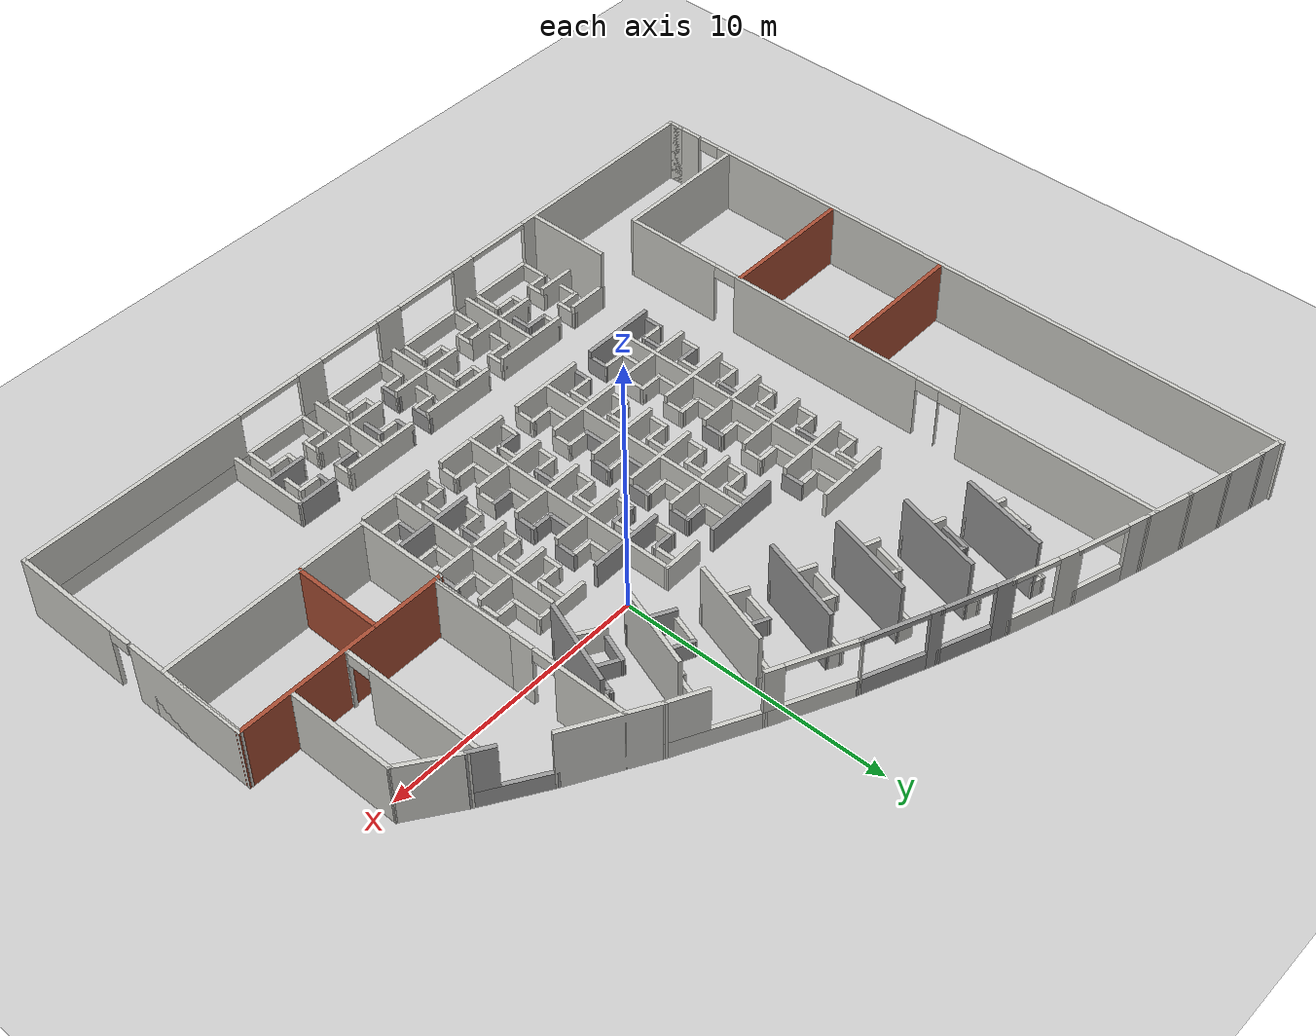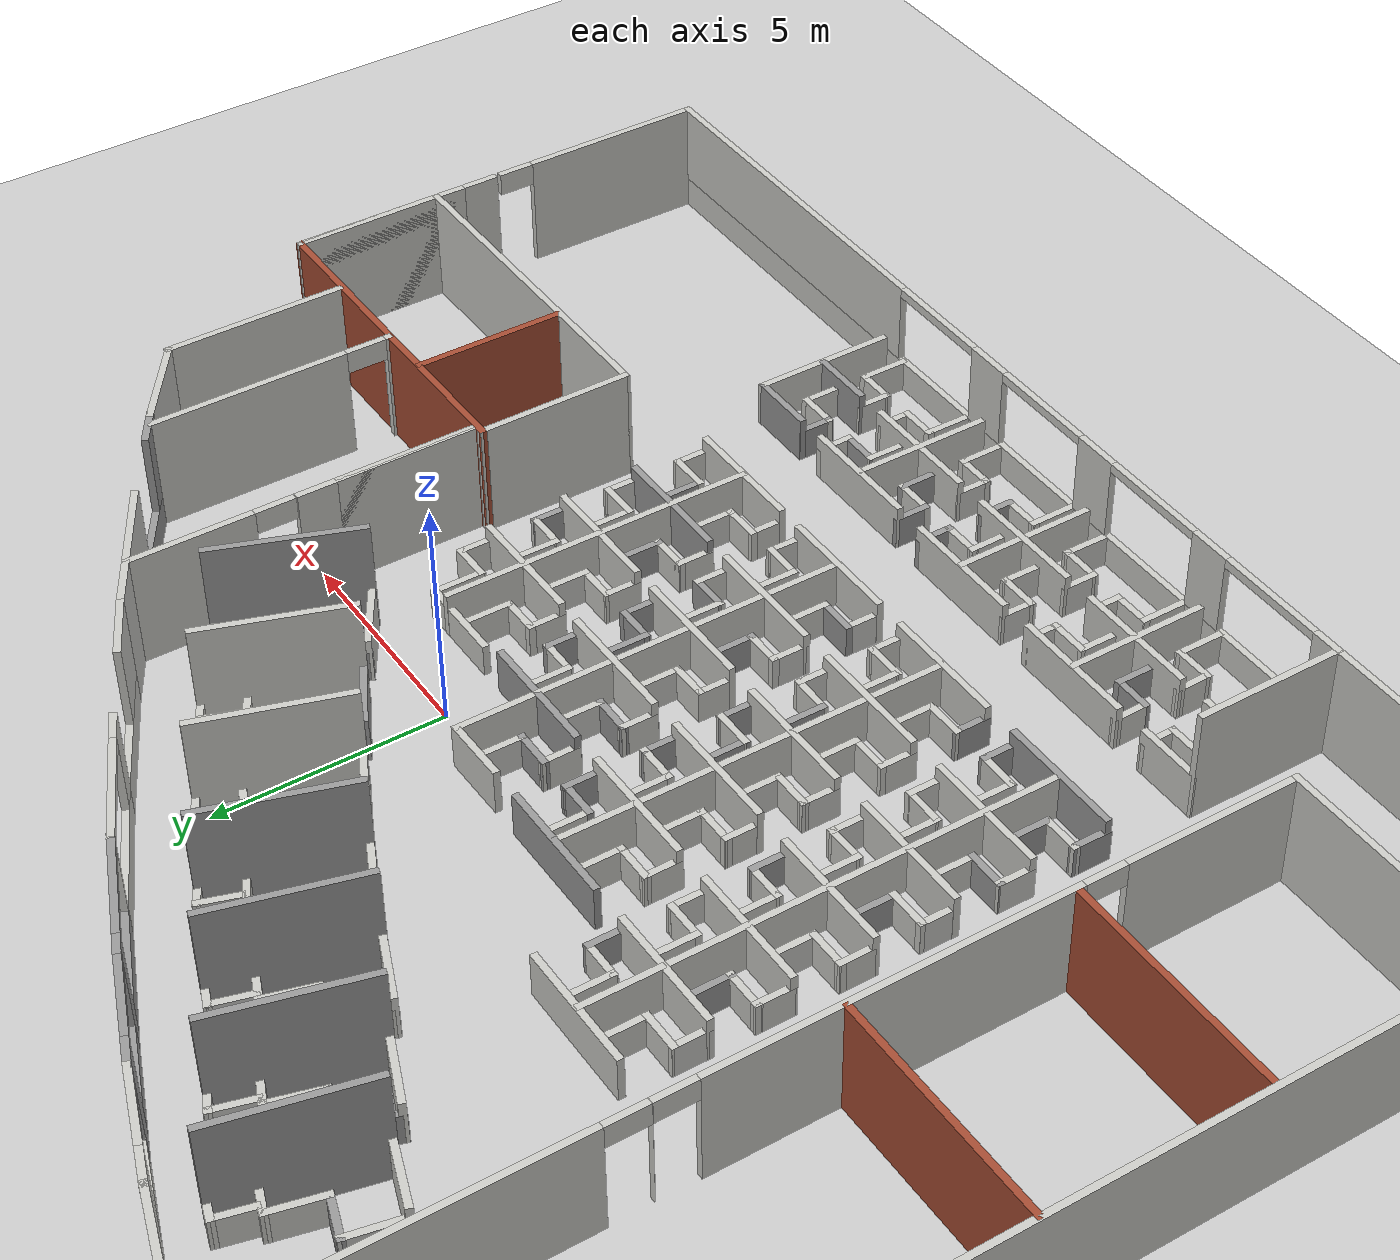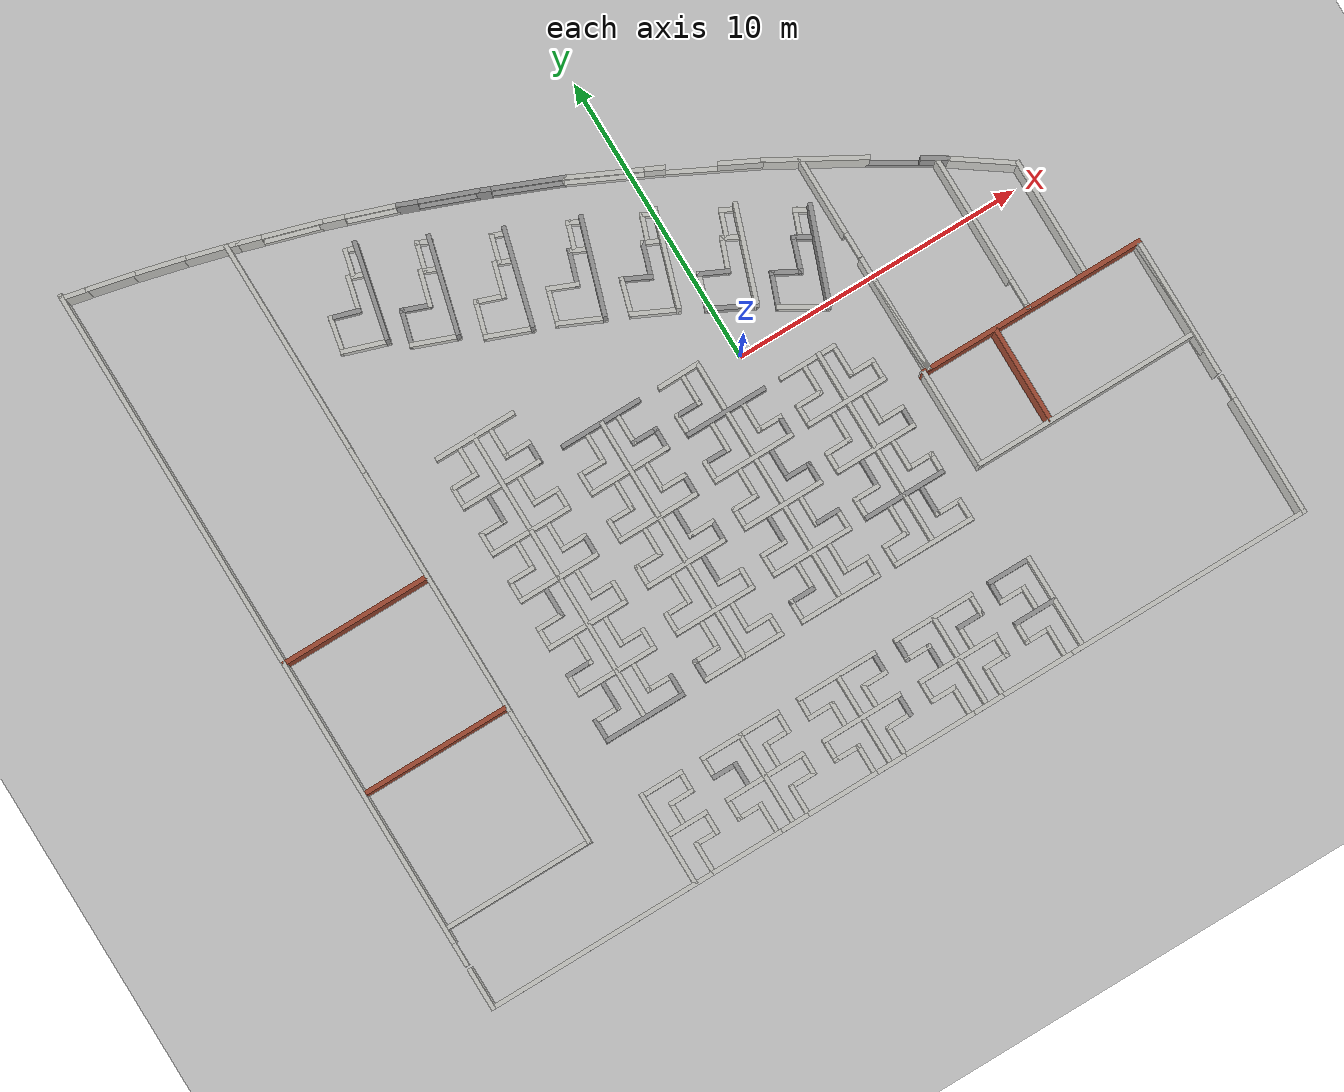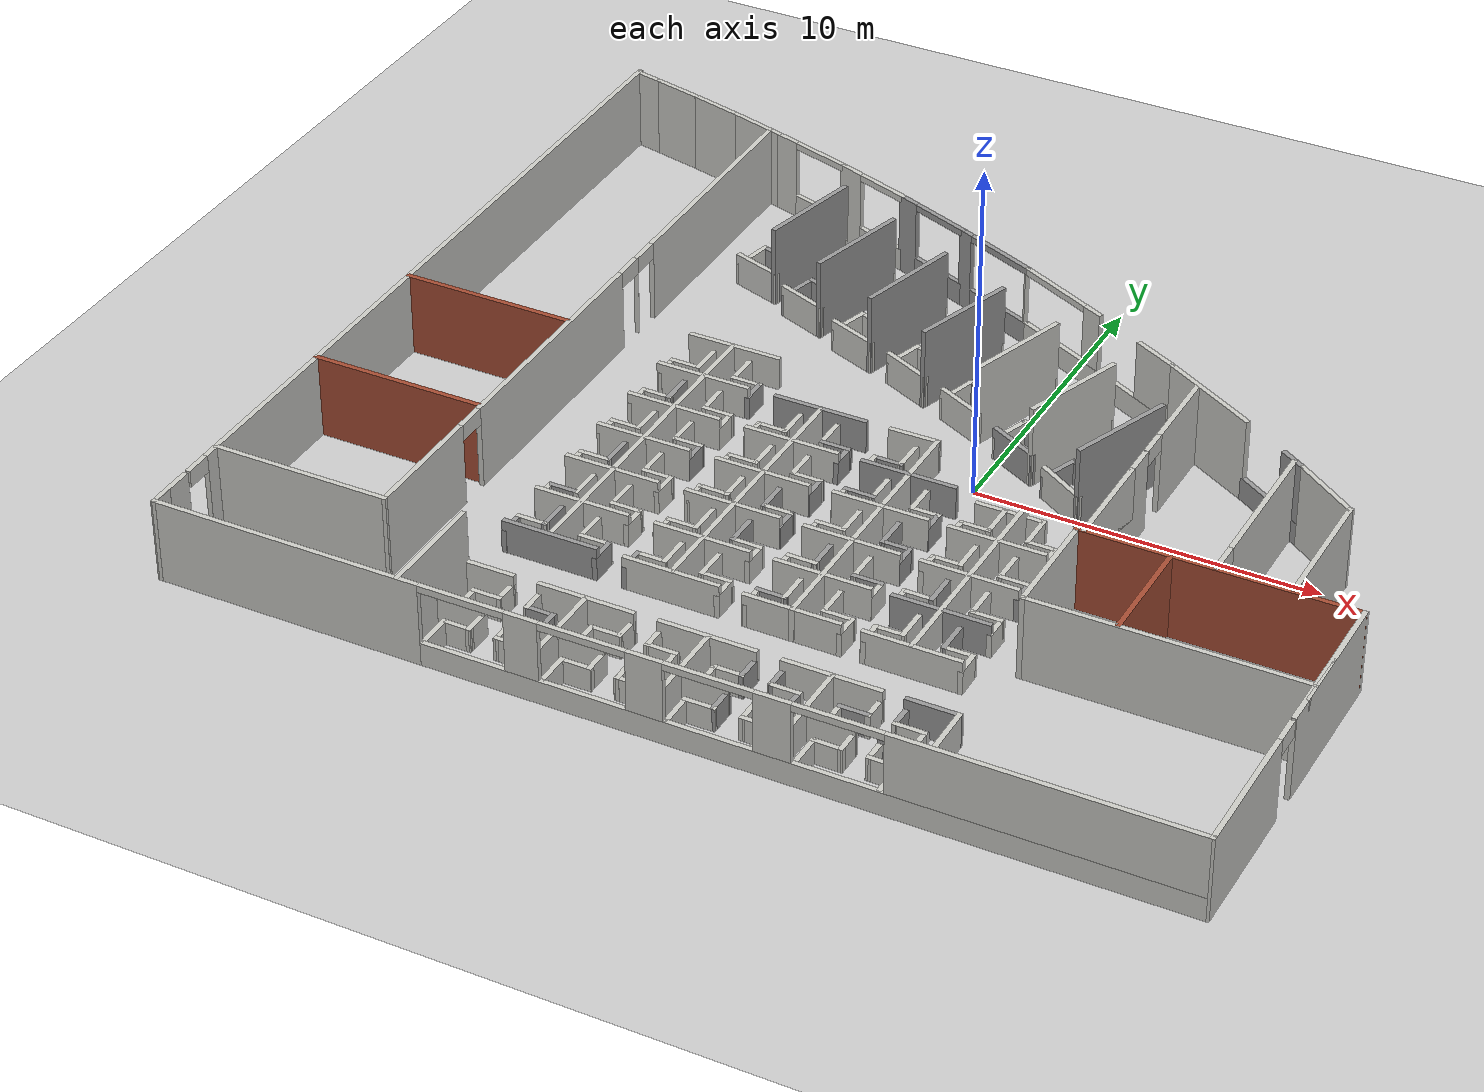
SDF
<sdf version="1.6">
 <world name="default">
  <light name="sun" type="directional">
   <pose>0 0 10 0 -0 0</pose>
   <diffuse>0.8 0.8 0.8 1</diffuse>
   <specular>0.2 0.2 0.2 1</specular>
   <attenuation>
    <range>1000</range>
    <constant>0.9</constant>
    <linear>0.01</linear>
    <quadratic>0.001</quadratic>
   </attenuation>
   <direction>-0.5 0.1 -0.9</direction>
   <spot><inner_angle>0</inner_angle><outer_angle>0</outer_angle><falloff>0</falloff></spot>
  </light>
  <model name="ground_plane">
   <static>1</static>
   <link name="link">
    <collision name="collision">
     <geometry><plane><normal>0 0 1</normal><size>100 100</size></plane></geometry>
     <surface><friction><ode><mu>100</mu><mu2>50</mu2></ode></friction></surface>
    </collision>
    <visual name="visual">
     <cast_shadows>0</cast_shadows>
     <geometry><plane><normal>0 0 1</normal><size>100 100</size></plane></geometry>
     <material>
      <script><uri>file://media/materials/scripts/gazebo.material</uri><name>Gazebo/Grey</name></script>
     </material>
    </visual>
   </link>
  </model>
  <gravity>0 0 -9.8</gravity>
  <magnetic_field>6e-06 2.3e-05 -4.2e-05</magnetic_field>
  <atmosphere type="adiabatic"/>
  <physics type="ode">
   <max_step_size>0.001</max_step_size>
   <real_time_factor>1</real_time_factor>
   <real_time_update_rate>1000</real_time_update_rate>
  </physics>
  <scene><ambient>0.4 0.4 0.4 1</ambient><background>0.7 0.7 0.7 1</background><shadows>1</shadows></scene>
  <spherical_coordinates>
   <surface_model>EARTH_WGS84</surface_model>
   <latitude_deg>0</latitude_deg>
   <longitude_deg>0</longitude_deg>
   <elevation>0</elevation>
   <heading_deg>0</heading_deg>
  </spherical_coordinates>
  <model name="batclab">
   <pose>-2.43592 -0.434632 0 0 -0 0</pose>
   <link name="Wall_0">
    <pose>-14.7338 2.1e-05 0 0 -0 -1.57114</pose>
    <visual name="Wall_0_Visual_0">
     <pose>-1.19866 0 1.25 0 -0 0</pose>
     <geometry><box><size>23.5775 0.15 2.5</size></box></geometry>
     <material>
      <script><uri>file://media/materials/scripts/gazebo.material</uri><name>Gazebo/CeilingTiled</name></script>
      <ambient>1 1 1 1</ambient>
     </material>
     <meta><layer>0</layer></meta>
    </visual>
    <collision name="Wall_0_Collision_0">
     <geometry><box><size>23.5775 0.15 2.5</size></box></geometry>
     <pose>-1.19866 0 1.25 0 -0 0</pose>
    </collision>
    <visual name="Wall_0_Visual_1">
     <pose>12.2388 0 1.25 0 -0 0</pose>
     <geometry><box><size>1.49732 0.15 2.5</size></box></geometry>
     <material>
      <script><uri>file://media/materials/scripts/gazebo.material</uri><name>Gazebo/CeilingTiled</name></script>
      <ambient>1 1 1 1</ambient>
     </material>
     <meta><layer>0</layer></meta>
    </visual>
    <collision name="Wall_0_Collision_1">
     <geometry><box><size>1.49732 0.15 2.5</size></box></geometry>
     <pose>12.2388 0 1.25 0 -0 0</pose>
    </collision>
    <visual name="Wall_0_Visual_2">
     <pose>12.6483 0 1.25 0 -0 0</pose>
     <geometry><box><size>0.678351 0.15 2.5</size></box></geometry>
     <material>
      <script><uri>file://media/materials/scripts/gazebo.material</uri><name>Gazebo/CeilingTiled</name></script>
      <ambient>1 1 1 1</ambient>
     </material>
     <meta><layer>0</layer></meta>
    </visual>
    <collision name="Wall_0_Collision_2">
     <geometry><box><size>0.678351 0.15 2.5</size></box></geometry>
     <pose>12.6483 0 1.25 0 -0 0</pose>
    </collision>
    <visual name="Wall_0_Visual_3">
     <pose>10.9996 0 2.25 0 -0 0</pose>
     <geometry><box><size>0.81897 0.15 0.5</size></box></geometry>
     <material>
      <script><uri>file://media/materials/scripts/gazebo.material</uri><name>Gazebo/CeilingTiled</name></script>
      <ambient>1 1 1 1</ambient>
     </material>
     <meta><layer>0</layer></meta>
    </visual>
    <collision name="Wall_0_Collision_3">
     <geometry><box><size>0.81897 0.15 0.5</size></box></geometry>
     <pose>10.9996 0 2.25 0 -0 0</pose>
    </collision>
   </link>
   <link name="Wall_102">
    <collision name="Wall_102_Collision">
     <geometry><box><size>2.865 0.15 1</size></box></geometry>
     <pose>0 0 0.5 0 -0 0</pose>
    </collision>
    <visual name="Wall_102_Visual">
     <pose>0 0 0.5 0 -0 0</pose>
     <geometry><box><size>2.865 0.15 1</size></box></geometry>
     <material>
      <script><uri>file://media/materials/scripts/gazebo.material</uri><name>Gazebo/Grey</name></script>
      <ambient>1 1 1 1</ambient>
     </material>
     <meta><layer>0</layer></meta>
    </visual>
    <pose>-6.02592 -7.66961 0 0 -0 0</pose>
   </link>
   <link name="Wall_104">
    <collision name="Wall_104_Collision">
     <geometry><box><size>2.865 0.15 1</size></box></geometry>
     <pose>0 0 0.5 0 -0 0</pose>
    </collision>
    <visual name="Wall_104_Visual">
     <pose>0 0 0.5 0 -0 0</pose>
     <geometry><box><size>2.865 0.15 1</size></box></geometry>
     <material>
      <script><uri>file://media/materials/scripts/gazebo.material</uri><name>Gazebo/CeilingTiled</name></script>
      <ambient>1 1 1 1</ambient>
     </material>
     <meta><layer>0</layer></meta>
    </visual>
    <pose>-2.41702 -7.65761 0 0 -0 0</pose>
   </link>
   <link name="Wall_106">
    <collision name="Wall_106_Collision">
     <geometry><box><size>2.865 0.15 1</size></box></geometry>
     <pose>0 0 0.5 0 -0 0</pose>
    </collision>
    <visual name="Wall_106_Visual">
     <pose>0 0 0.5 0 -0 0</pose>
     <geometry><box><size>2.865 0.15 1</size></box></geometry>
     <material>
      <script><uri>file://media/materials/scripts/gazebo.material</uri><name>Gazebo/CeilingTiled</name></script>
      <ambient>1 1 1 1</ambient>
     </material>
     <meta><layer>0</layer></meta>
    </visual>
    <pose>-2.42436 -5.95096 0 0 -0 0</pose>
   </link>
   <link name="Wall_108">
    <collision name="Wall_108_Collision">
     <geometry><box><size>1.11648 0.15 0.7</size></box></geometry>
     <pose>0 0 0.35 0 -0 0</pose>
    </collision>
    <visual name="Wall_108_Visual">
     <pose>0 0 0.35 0 -0 0</pose>
     <geometry><box><size>1.11648 0.15 0.7</size></box></geometry>
     <material>
      <script><uri>file://media/materials/scripts/gazebo.material</uri><name>Gazebo/CeilingTiled</name></script>
      <ambient>1 1 1 1</ambient>
     </material>
     <meta><layer>0</layer></meta>
    </visual>
    <pose>-6.58842 -4.81161 0 0 -0 -1.5708</pose>
   </link>
   <link name="Wall_109">
    <collision name="Wall_109_Collision">
     <geometry><box><size>0.954505 0.15 0.7</size></box></geometry>
     <pose>0 0 0.35 0 -0 0</pose>
    </collision>
    <visual name="Wall_109_Visual">
     <pose>0 0 0.35 0 -0 0</pose>
     <geometry><box><size>0.954505 0.15 0.7</size></box></geometry>
     <material>
      <script><uri>file://media/materials/scripts/gazebo.material</uri><name>Gazebo/Grey</name></script>
      <ambient>1 1 1 1</ambient>
     </material>
     <meta><layer>0</layer></meta>
    </visual>
    <pose>-6.99092 -5.29461 0 0 -0 3.14159</pose>
   </link>
   <link name="Wall_110">
    <collision name="Wall_110_Collision">
     <geometry><box><size>0.819178 0.15 0.7</size></box></geometry>
     <pose>0 0 0.35 0 -0 0</pose>
    </collision>
    <visual name="Wall_110_Visual">
     <pose>0 0 0.35 0 -0 0</pose>
     <geometry><box><size>0.819178 0.15 0.7</size></box></geometry>
     <material>
      <script><uri>file://media/materials/scripts/gazebo.material</uri><name>Gazebo/CeilingTiled</name></script>
      <ambient>1 1 1 1</ambient>
     </material>
     <meta><layer>0</layer></meta>
    </visual>
    <pose>-7.39542 -5.62911 0 0 -0 -1.57678</pose>
   </link>
   <link name="Wall_112">
    <collision name="Wall_112_Collision">
     <geometry><box><size>1.1312 0.15 0.7</size></box></geometry>
     <pose>0 0 0.35 0 -0 0</pose>
    </collision>
    <visual name="Wall_112_Visual">
     <pose>0 0 0.35 0 -0 0</pose>
     <geometry><box><size>1.1312 0.15 0.7</size></box></geometry>
     <material>
      <script><uri>file://media/materials/scripts/gazebo.material</uri><name>Gazebo/CeilingTiled</name></script>
      <ambient>1 1 1 1</ambient>
     </material>
     <meta><layer>0</layer></meta>
    </visual>
    <pose>-5.47742 -4.81511 0 0 -0 -1.57487</pose>
   </link>
   <link name="Wall_113">
    <collision name="Wall_113_Collision">
     <geometry><box><size>0.965792 0.15 0.7</size></box></geometry>
     <pose>0 0 0.35 0 -0 0</pose>
    </collision>
    <visual name="Wall_113_Visual">
     <pose>0 0 0.35 0 -0 0</pose>
     <geometry><box><size>0.965792 0.15 0.7</size></box></geometry>
     <material>
      <script><uri>file://media/materials/scripts/gazebo.material</uri><name>Gazebo/CeilingTiled</name></script>
      <ambient>1 1 1 1</ambient>
     </material>
     <meta><layer>0</layer></meta>
    </visual>
    <pose>-5.07142 -5.30561 0 0 -0 0</pose>
   </link>
   <link name="Wall_114">
    <collision name="Wall_114_Collision">
     <geometry><box><size>0.815451 0.15 0.7</size></box></geometry>
     <pose>0 0 0.35 0 -0 0</pose>
    </collision>
    <visual name="Wall_114_Visual">
     <pose>0 0 0.35 0 -0 0</pose>
     <geometry><box><size>0.815451 0.15 0.7</size></box></geometry>
     <material>
      <script><uri>file://media/materials/scripts/gazebo.material</uri><name>Gazebo/CeilingTiled</name></script>
      <ambient>1 1 1 1</ambient>
     </material>
     <meta><layer>0</layer></meta>
    </visual>
    <pose>-4.66542 -5.63861 0 0 -0 -1.5768</pose>
   </link>
   <link name="Wall_116">
    <collision name="Wall_116_Collision">
     <geometry><box><size>1.085 0.15 0.7</size></box></geometry>
     <pose>0 0 0.35 0 -0 0</pose>
    </collision>
    <visual name="Wall_116_Visual">
     <pose>0 0 0.35 0 -0 0</pose>
     <geometry><box><size>1.085 0.15 0.7</size></box></geometry>
     <material>
      <script><uri>file://media/materials/scripts/gazebo.material</uri><name>Gazebo/Grey</name></script>
      <ambient>1 1 1 1</ambient>
     </material>
     <meta><layer>0</layer></meta>
    </visual>
    <pose>-6.59742 -6.49711 0 0 -0 -1.5708</pose>
   </link>
   <link name="Wall_117">
    <collision name="Wall_117_Collision">
     <geometry><box><size>0.954006 0.15 0.7</size></box></geometry>
     <pose>0 0 0.35 0 -0 0</pose>
    </collision>
    <visual name="Wall_117_Visual">
     <pose>0 0 0.35 0 -0 0</pose>
     <geometry><box><size>0.954006 0.15 0.7</size></box></geometry>
     <material>
      <script><uri>file://media/materials/scripts/gazebo.material</uri><name>Gazebo/CeilingTiled</name></script>
      <ambient>1 1 1 1</ambient>
     </material>
     <meta><layer>0</layer></meta>
    </visual>
    <pose>-6.99942 -6.96311 0 0 -0 3.13786</pose>
   </link>
   <link name="Wall_118">
    <collision name="Wall_118_Collision">
     <geometry><box><size>0.866762 0.15 0.7</size></box></geometry>
     <pose>0 0 0.35 0 -0 0</pose>
    </collision>
    <visual name="Wall_118_Visual">
     <pose>0 0 0.35 0 -0 0</pose>
     <geometry><box><size>0.866762 0.15 0.7</size></box></geometry>
     <material>
      <script><uri>file://media/materials/scripts/gazebo.material</uri><name>Gazebo/Grey</name></script>
      <ambient>1 1 1 1</ambient>
     </material>
     <meta><layer>0</layer></meta>
    </visual>
    <pose>-7.40142 -7.32011 0 0 -0 -1.5708</pose>
   </link>
   <link name="Wall_12">
    <collision name="Wall_12_Collision">
     <geometry><box><size>5.3301 0.15 2.5</size></box></geometry>
     <pose>0 0 1.25 0 -0 0</pose>
    </collision>
    <visual name="Wall_12_Visual">
     <pose>0 0 1.25 0 -0 0</pose>
     <geometry><box><size>5.3301 0.15 2.5</size></box></geometry>
     <material>
      <script><uri>file://media/materials/scripts/gazebo.material</uri><name>Gazebo/CeilingTiled</name></script>
      <ambient>1 1 1 1</ambient>
     </material>
     <meta><layer>0</layer></meta>
    </visual>
    <pose>-12.1199 -10.0685 0 0 -0 0.001104</pose>
   </link>
   <link name="Wall_120">
    <collision name="Wall_120_Collision">
     <geometry><box><size>1.09902 0.15 0.7</size></box></geometry>
     <pose>0 0 0.35 0 -0 0</pose>
    </collision>
    <visual name="Wall_120_Visual">
     <pose>0 0 0.35 0 -0 0</pose>
     <geometry><box><size>1.09902 0.15 0.7</size></box></geometry>
     <material>
      <script><uri>file://media/materials/scripts/gazebo.material</uri><name>Gazebo/CeilingTiled</name></script>
      <ambient>1 1 1 1</ambient>
     </material>
     <meta><layer>0</layer></meta>
    </visual>
    <pose>-5.48042 -6.50711 0 0 -0 -1.57712</pose>
   </link>
   <link name="Wall_121">
    <collision name="Wall_121_Collision">
     <geometry><box><size>0.968799 0.15 0.7</size></box></geometry>
     <pose>0 0 0.35 0 -0 0</pose>
    </collision>
    <visual name="Wall_121_Visual">
     <pose>0 0 0.35 0 -0 0</pose>
     <geometry><box><size>0.968799 0.15 0.7</size></box></geometry>
     <material>
      <script><uri>file://media/materials/scripts/gazebo.material</uri><name>Gazebo/CeilingTiled</name></script>
      <ambient>1 1 1 1</ambient>
     </material>
     <meta><layer>0</layer></meta>
    </visual>
    <pose>-5.07392 -6.98461 0 0 -0 -0.007326</pose>
   </link>
   <link name="Wall_122">
    <collision name="Wall_122_Collision">
     <geometry><box><size>0.837919 0.15 0.7</size></box></geometry>
     <pose>0 0 0.35 0 -0 0</pose>
    </collision>
    <visual name="Wall_122_Visual">
     <pose>0 0 0.35 0 -0 0</pose>
     <geometry><box><size>0.837919 0.15 0.7</size></box></geometry>
     <material>
      <script><uri>file://media/materials/scripts/gazebo.material</uri><name>Gazebo/Grey</name></script>
      <ambient>1 1 1 1</ambient>
     </material>
     <meta><layer>0</layer></meta>
    </visual>
    <pose>-4.66442 -7.33161 0 0 -0 -1.5708</pose>
   </link>
   <link name="Wall_124">
    <collision name="Wall_124_Collision">
     <geometry><box><size>1.1146 0.15 0.7</size></box></geometry>
     <pose>0 0 0.35 0 -0 0</pose>
    </collision>
    <visual name="Wall_124_Visual">
     <pose>0 0 0.35 0 -0 0</pose>
     <geometry><box><size>1.1146 0.15 0.7</size></box></geometry>
     <material>
      <script><uri>file://media/materials/scripts/gazebo.material</uri><name>Gazebo/CeilingTiled</name></script>
      <ambient>1 1 1 1</ambient>
     </material>
     <meta><layer>0</layer></meta>
    </visual>
    <pose>-2.97542 -6.50311 0 0 -0 -1.5708</pose>
   </link>
   <link name="Wall_125">
    <collision name="Wall_125_Collision">
     <geometry><box><size>0.964006 0.15 0.7</size></box></geometry>
     <pose>0 0 0.35 0 -0 0</pose>
    </collision>
    <visual name="Wall_125_Visual">
     <pose>0 0 0.35 0 -0 0</pose>
     <geometry><box><size>0.964006 0.15 0.7</size></box></geometry>
     <material>
      <script><uri>file://media/materials/scripts/gazebo.material</uri><name>Gazebo/CeilingTiled</name></script>
      <ambient>1 1 1 1</ambient>
     </material>
     <meta><layer>0</layer></meta>
    </visual>
    <pose>-3.38242 -6.98711 0 0 -0 -3.13791</pose>
   </link>
   <link name="Wall_126">
    <collision name="Wall_126_Collision">
     <geometry><box><size>0.820149 0.15 0.7</size></box></geometry>
     <pose>0 0 0.35 0 -0 0</pose>
    </collision>
    <visual name="Wall_126_Visual">
     <pose>0 0 0.35 0 -0 0</pose>
     <geometry><box><size>0.820149 0.15 0.7</size></box></geometry>
     <material>
      <script><uri>file://media/materials/scripts/gazebo.material</uri><name>Gazebo/Grey</name></script>
      <ambient>1 1 1 1</ambient>
     </material>
     <meta><layer>0</layer></meta>
    </visual>
    <pose>-3.78942 -7.32361 0 0 -0 -1.5708</pose>
   </link>
   <link name="Wall_128">
    <collision name="Wall_128_Collision">
     <geometry><box><size>1.13401 0.15 0.7</size></box></geometry>
     <pose>0 0 0.35 0 -0 0</pose>
    </collision>
    <visual name="Wall_128_Visual">
     <pose>0 0 0.35 0 -0 0</pose>
     <geometry><box><size>1.13401 0.15 0.7</size></box></geometry>
     <material>
      <script><uri>file://media/materials/scripts/gazebo.material</uri><name>Gazebo/CeilingTiled</name></script>
      <ambient>1 1 1 1</ambient>
     </material>
     <meta><layer>0</layer></meta>
    </visual>
    <pose>-1.86842 -6.49961 0 0 -0 -1.57486</pose>
   </link>
   <link name="Wall_129">
    <collision name="Wall_129_Collision">
     <geometry><box><size>0.960743 0.15 0.7</size></box></geometry>
     <pose>0 0 0.35 0 -0 0</pose>
    </collision>
    <visual name="Wall_129_Visual">
     <pose>0 0 0.35 0 -0 0</pose>
     <geometry><box><size>0.960743 0.15 0.7</size></box></geometry>
     <material>
      <script><uri>file://media/materials/scripts/gazebo.material</uri><name>Gazebo/CeilingTiled</name></script>
      <ambient>1 1 1 1</ambient>
     </material>
     <meta><layer>0</layer></meta>
    </visual>
    <pose>-1.46492 -6.99011 0 0 -0 0.003699</pose>
   </link>
   <link name="Wall_13">
    <pose>-9.5299 0.73431 0 0 -0 1.5708</pose>
    <visual name="Wall_13_Visual_0">
     <pose>-8.93757 0 1.25 0 -0 0</pose>
     <geometry><box><size>3.87486 0.15 2.5</size></box></geometry>
     <material>
      <script><uri>file://media/materials/scripts/gazebo.material</uri><name>Gazebo/CeilingTiled</name></script>
      <ambient>1 1 1 1</ambient>
     </material>
     <meta><layer>0</layer></meta>
    </visual>
    <collision name="Wall_13_Collision_0">
     <geometry><box><size>3.87486 0.15 2.5</size></box></geometry>
     <pose>-8.93757 0 1.25 0 -0 0</pose>
    </collision>
    <visual name="Wall_13_Visual_1">
     <pose>-2.21758 0 1.25 0 -0 0</pose>
     <geometry><box><size>7.76512 0.15 2.5</size></box></geometry>
     <material>
      <script><uri>file://media/materials/scripts/gazebo.material</uri><name>Gazebo/CeilingTiled</name></script>
      <ambient>1 1 1 1</ambient>
     </material>
     <meta><layer>0</layer></meta>
    </visual>
    <collision name="Wall_13_Collision_1">
     <geometry><box><size>7.76512 0.15 2.5</size></box></geometry>
     <pose>-2.21758 0 1.25 0 -0 0</pose>
    </collision>
    <visual name="Wall_13_Visual_2">
     <pose>2.56716 0 1.25 0 -0 0</pose>
     <geometry><box><size>0.004348 0.15 2.5</size></box></geometry>
     <material>
      <script><uri>file://media/materials/scripts/gazebo.material</uri><name>Gazebo/CeilingTiled</name></script>
      <ambient>1 1 1 1</ambient>
     </material>
     <meta><layer>0</layer></meta>
    </visual>
    <collision name="Wall_13_Collision_2">
     <geometry><box><size>0.004348 0.15 2.5</size></box></geometry>
     <pose>2.56716 0 1.25 0 -0 0</pose>
    </collision>
    <visual name="Wall_13_Visual_3">
     <pose>7.17216 0 1.25 0 -0 0</pose>
     <geometry><box><size>7.40567 0.15 2.5</size></box></geometry>
     <material>
      <script><uri>file://media/materials/scripts/gazebo.material</uri><name>Gazebo/CeilingTiled</name></script>
      <ambient>1 1 1 1</ambient>
     </material>
     <meta><layer>0</layer></meta>
    </visual>
    <collision name="Wall_13_Collision_3">
     <geometry><box><size>7.40567 0.15 2.5</size></box></geometry>
     <pose>7.17216 0 1.25 0 -0 0</pose>
    </collision>
    <visual name="Wall_13_Visual_4">
     <pose>-6.55014 0 2.25 0 -0 0</pose>
     <geometry><box><size>0.9 0.15 0.5</size></box></geometry>
     <material>
      <script><uri>file://media/materials/scripts/gazebo.material</uri><name>Gazebo/CeilingTiled</name></script>
      <ambient>1 1 1 1</ambient>
     </material>
     <meta><layer>0</layer></meta>
    </visual>
    <collision name="Wall_13_Collision_4">
     <geometry><box><size>0.9 0.15 0.5</size></box></geometry>
     <pose>-6.55014 0 2.25 0 -0 0</pose>
    </collision>
    <visual name="Wall_13_Visual_5">
     <pose>2.11498 0 2.25 0 -0 0</pose>
     <geometry><box><size>0.9 0.15 0.5</size></box></geometry>
     <material>
      <script><uri>file://media/materials/scripts/gazebo.material</uri><name>Gazebo/CeilingTiled</name></script>
      <ambient>1 1 1 1</ambient>
     </material>
     <meta><layer>0</layer></meta>
    </visual>
    <collision name="Wall_13_Collision_5">
     <geometry><box><size>0.9 0.15 0.5</size></box></geometry>
     <pose>2.11498 0 2.25 0 -0 0</pose>
    </collision>
    <visual name="Wall_13_Visual_6">
     <pose>3.01933 0 2.25 0 -0 0</pose>
     <geometry><box><size>0.9 0.15 0.5</size></box></geometry>
     <material>
      <script><uri>file://media/materials/scripts/gazebo.material</uri><name>Gazebo/CeilingTiled</name></script>
      <ambient>1 1 1 1</ambient>
     </material>
     <meta><layer>0</layer></meta>
    </visual>
    <collision name="Wall_13_Collision_6">
     <geometry><box><size>0.9 0.15 0.5</size></box></geometry>
     <pose>3.01933 0 2.25 0 -0 0</pose>
    </collision>
   </link>
   <link name="Wall_130">
    <collision name="Wall_130_Collision">
     <geometry><box><size>0.819914 0.15 0.7</size></box></geometry>
     <pose>0 0 0.35 0 -0 0</pose>
    </collision>
    <visual name="Wall_130_Visual">
     <pose>0 0 0.35 0 -0 0</pose>
     <geometry><box><size>0.819914 0.15 0.7</size></box></geometry>
     <material>
      <script><uri>file://media/materials/scripts/gazebo.material</uri><name>Gazebo/CeilingTiled</name></script>
      <ambient>1 1 1 1</ambient>
     </material>
     <meta><layer>0</layer></meta>
    </visual>
    <pose>-1.05942 -7.32361 0 0 -0 -1.5708</pose>
   </link>
   <link name="Wall_132">
    <collision name="Wall_132_Collision">
     <geometry><box><size>1.12501 0.15 0.7</size></box></geometry>
     <pose>0 0 0.35 0 -0 0</pose>
    </collision>
    <visual name="Wall_132_Visual">
     <pose>0 0 0.35 0 -0 0</pose>
     <geometry><box><size>1.12501 0.15 0.7</size></box></geometry>
     <material>
      <script><uri>file://media/materials/scripts/gazebo.material</uri><name>Gazebo/CeilingTiled</name></script>
      <ambient>1 1 1 1</ambient>
     </material>
     <meta><layer>0</layer></meta>
    </visual>
    <pose>-2.97542 -4.78311 0 0 -0 -1.56669</pose>
   </link>
   <link name="Wall_133">
    <collision name="Wall_133_Collision">
     <geometry><box><size>0.970346 0.15 0.7</size></box></geometry>
     <pose>0 0 0.35 0 -0 0</pose>
    </collision>
    <visual name="Wall_133_Visual">
     <pose>0 0 0.35 0 -0 0</pose>
     <geometry><box><size>0.970346 0.15 0.7</size></box></geometry>
     <material>
      <script><uri>file://media/materials/scripts/gazebo.material</uri><name>Gazebo/CeilingTiled</name></script>
      <ambient>1 1 1 1</ambient>
     </material>
     <meta><layer>0</layer></meta>
    </visual>
    <pose>-3.38342 -5.27211 0 0 -0 -3.13793</pose>
   </link>
   <link name="Wall_134">
    <collision name="Wall_134_Collision">
     <geometry><box><size>0.827153 0.15 0.7</size></box></geometry>
     <pose>0 0 0.35 0 -0 0</pose>
    </collision>
    <visual name="Wall_134_Visual">
     <pose>0 0 0.35 0 -0 0</pose>
     <geometry><box><size>0.827153 0.15 0.7</size></box></geometry>
     <material>
      <script><uri>file://media/materials/scripts/gazebo.material</uri><name>Gazebo/CeilingTiled</name></script>
      <ambient>1 1 1 1</ambient>
     </material>
     <meta><layer>0</layer></meta>
    </visual>
    <pose>-3.79342 -5.61211 0 0 -0 -1.5708</pose>
   </link>
   <link name="Wall_136">
    <collision name="Wall_136_Collision">
     <geometry><box><size>1.15946 0.15 0.7</size></box></geometry>
     <pose>0 0 0.35 0 -0 0</pose>
    </collision>
    <visual name="Wall_136_Visual">
     <pose>0 0 0.35 0 -0 0</pose>
     <geometry><box><size>1.15946 0.15 0.7</size></box></geometry>
     <material>
      <script><uri>file://media/materials/scripts/gazebo.material</uri><name>Gazebo/Grey</name></script>
      <ambient>1 1 1 1</ambient>
     </material>
     <meta><layer>0</layer></meta>
    </visual>
    <pose>-1.86392 -4.77611 0 0 -0 -1.57377</pose>
   </link>
   <link name="Wall_137">
    <collision name="Wall_137_Collision">
     <geometry><box><size>0.957447 0.15 0.7</size></box></geometry>
     <pose>0 0 0.35 0 -0 0</pose>
    </collision>
    <visual name="Wall_137_Visual">
     <pose>0 0 0.35 0 -0 0</pose>
     <geometry><box><size>0.957447 0.15 0.7</size></box></geometry>
     <material>
      <script><uri>file://media/materials/scripts/gazebo.material</uri><name>Gazebo/CeilingTiled</name></script>
      <ambient>1 1 1 1</ambient>
     </material>
     <meta><layer>0</layer></meta>
    </visual>
    <pose>-1.46192 -5.28961 0 0 -0 -0.022301</pose>
   </link>
   <link name="Wall_138">
    <collision name="Wall_138_Collision">
     <geometry><box><size>0.804299 0.15 0.7</size></box></geometry>
     <pose>0 0 0.35 0 -0 0</pose>
    </collision>
    <visual name="Wall_138_Visual">
     <pose>0 0 0.35 0 -0 0</pose>
     <geometry><box><size>0.804299 0.15 0.7</size></box></geometry>
     <material>
      <script><uri>file://media/materials/scripts/gazebo.material</uri><name>Gazebo/CeilingTiled</name></script>
      <ambient>1 1 1 1</ambient>
     </material>
     <meta><layer>0</layer></meta>
    </visual>
    <pose>-1.05992 -5.62561 0 0 -0 -1.57538</pose>
   </link>
   <link name="Wall_140">
    <collision name="Wall_140_Collision">
     <geometry><box><size>1.09101 0.15 0.7</size></box></geometry>
     <pose>0 0 0.35 0 -0 0</pose>
    </collision>
    <visual name="Wall_140_Visual">
     <pose>0 0 0.35 0 -0 0</pose>
     <geometry><box><size>1.09101 0.15 0.7</size></box></geometry>
     <material>
      <script><uri>file://media/materials/scripts/gazebo.material</uri><name>Gazebo/CeilingTiled</name></script>
      <ambient>1 1 1 1</ambient>
     </material>
     <meta><layer>0</layer></meta>
    </visual>
    <pose>-2.97792 -3.06811 0 0 -0 -1.57398</pose>
   </link>
   <link name="Wall_141">
    <collision name="Wall_141_Collision">
     <geometry><box><size>0.963985 0.15 0.7</size></box></geometry>
     <pose>0 0 0.35 0 -0 0</pose>
    </collision>
    <visual name="Wall_141_Visual">
     <pose>0 0 0.35 0 -0 0</pose>
     <geometry><box><size>0.963985 0.15 0.7</size></box></geometry>
     <material>
      <script><uri>file://media/materials/scripts/gazebo.material</uri><name>Gazebo/CeilingTiled</name></script>
      <ambient>1 1 1 1</ambient>
     </material>
     <meta><layer>0</layer></meta>
    </visual>
    <pose>-3.38642 -3.53361 0 0 -0 3.12931</pose>
   </link>
   <link name="Wall_142">
    <collision name="Wall_142_Collision">
     <geometry><box><size>0.849856 0.15 0.7</size></box></geometry>
     <pose>0 0 0.35 0 -0 0</pose>
    </collision>
    <visual name="Wall_142_Visual">
     <pose>0 0 0.35 0 -0 0</pose>
     <geometry><box><size>0.849856 0.15 0.7</size></box></geometry>
     <material>
      <script><uri>file://media/materials/scripts/gazebo.material</uri><name>Gazebo/CeilingTiled</name></script>
      <ambient>1 1 1 1</ambient>
     </material>
     <meta><layer>0</layer></meta>
    </visual>
    <pose>-3.79542 -3.87861 0 0 -0 -1.57651</pose>
   </link>
   <link name="Wall_144">
    <collision name="Wall_144_Collision">
     <geometry><box><size>1.08532 0.15 0.7</size></box></geometry>
     <pose>0 0 0.35 0 -0 0</pose>
    </collision>
    <visual name="Wall_144_Visual">
     <pose>0 0 0.35 0 -0 0</pose>
     <geometry><box><size>1.08532 0.15 0.7</size></box></geometry>
     <material>
      <script><uri>file://media/materials/scripts/gazebo.material</uri><name>Gazebo/Grey</name></script>
      <ambient>1 1 1 1</ambient>
     </material>
     <meta><layer>0</layer></meta>
    </visual>
    <pose>-1.85542 -3.07811 0 0 -0 -1.5708</pose>
   </link>
   <link name="Wall_145">
    <collision name="Wall_145_Collision">
     <geometry><box><size>0.957447 0.15 0.7</size></box></geometry>
     <pose>0 0 0.35 0 -0 0</pose>
    </collision>
    <visual name="Wall_145_Visual">
     <pose>0 0 0.35 0 -0 0</pose>
     <geometry><box><size>0.957447 0.15 0.7</size></box></geometry>
     <material>
      <script><uri>file://media/materials/scripts/gazebo.material</uri><name>Gazebo/CeilingTiled</name></script>
      <ambient>1 1 1 1</ambient>
     </material>
     <meta><layer>0</layer></meta>
    </visual>
    <pose>-1.45142 -3.54211 0 0 -0 0.008663</pose>
   </link>
   <link name="Wall_146">
    <collision name="Wall_146_Collision">
     <geometry><box><size>0.830012 0.15 0.7</size></box></geometry>
     <pose>0 0 0.35 0 -0 0</pose>
    </collision>
    <visual name="Wall_146_Visual">
     <pose>0 0 0.35 0 -0 0</pose>
     <geometry><box><size>0.830012 0.15 0.7</size></box></geometry>
     <material>
      <script><uri>file://media/materials/scripts/gazebo.material</uri><name>Gazebo/Grey</name></script>
      <ambient>1 1 1 1</ambient>
     </material>
     <meta><layer>0</layer></meta>
    </visual>
    <pose>-1.04942 -3.87861 0 0 -0 -1.57668</pose>
   </link>
   <link name="Wall_148">
    <collision name="Wall_148_Collision">
     <geometry><box><size>2.865 0.15 1</size></box></geometry>
     <pose>0 0 0.5 0 -0 0</pose>
    </collision>
    <visual name="Wall_148_Visual">
     <pose>0 0 0.5 0 -0 0</pose>
     <geometry><box><size>2.865 0.15 1</size></box></geometry>
     <material>
      <script><uri>file://media/materials/scripts/gazebo.material</uri><name>Gazebo/CeilingTiled</name></script>
      <ambient>1 1 1 1</ambient>
     </material>
     <meta><layer>0</layer></meta>
    </visual>
    <pose>-2.42292 -0.838607 0 0 -0 0</pose>
   </link>
   <link name="Wall_15">
    <collision name="Wall_15_Collision">
     <geometry><box><size>5.25 0.15 2.5</size></box></geometry>
     <pose>0 0 1.25 0 -0 0</pose>
    </collision>
    <visual name="Wall_15_Visual">
     <pose>0 0 1.25 0 -0 0</pose>
     <geometry><box><size>5.25 0.15 2.5</size></box></geometry>
     <material>
      <script><uri>file://media/materials/scripts/gazebo.material</uri><name>Gazebo/Bricks</name></script>
      <ambient>1 1 1 1</ambient>
     </material>
     <meta><layer>0</layer></meta>
    </visual>
    <pose>-12.1791 -5.1944 0 0 -0 0</pose>
   </link>
   <link name="Wall_150">
    <collision name="Wall_150_Collision">
     <geometry><box><size>2.865 0.15 1</size></box></geometry>
     <pose>0 0 0.5 0 -0 0</pose>
    </collision>
    <visual name="Wall_150_Visual">
     <pose>0 0 0.5 0 -0 0</pose>
     <geometry><box><size>2.865 0.15 1</size></box></geometry>
     <material>
      <script><uri>file://media/materials/scripts/gazebo.material</uri><name>Gazebo/Grey</name></script>
      <ambient>1 1 1 1</ambient>
     </material>
     <meta><layer>0</layer></meta>
    </visual>
    <pose>1.09824 -0.837491 0 0 -0 0</pose>
   </link>
   <link name="Wall_152">
    <collision name="Wall_152_Collision">
     <geometry><box><size>2.865 0.15 1</size></box></geometry>
     <pose>0 0 0.5 0 -0 0</pose>
    </collision>
    <visual name="Wall_152_Visual">
     <pose>0 0 0.5 0 -0 0</pose>
     <geometry><box><size>2.865 0.15 1</size></box></geometry>
     <material>
      <script><uri>file://media/materials/scripts/gazebo.material</uri><name>Gazebo/CeilingTiled</name></script>
      <ambient>1 1 1 1</ambient>
     </material>
     <meta><layer>0</layer></meta>
    </visual>
    <pose>1.08208 -2.51461 0 0 -0 0</pose>
   </link>
   <link name="Wall_154">
    <collision name="Wall_154_Collision">
     <geometry><box><size>2.865 0.15 1</size></box></geometry>
     <pose>0 0 0.5 0 -0 0</pose>
    </collision>
    <visual name="Wall_154_Visual">
     <pose>0 0 0.5 0 -0 0</pose>
     <geometry><box><size>2.865 0.15 1</size></box></geometry>
     <material>
      <script><uri>file://media/materials/scripts/gazebo.material</uri><name>Gazebo/Grey</name></script>
      <ambient>1 1 1 1</ambient>
     </material>
     <meta><layer>0</layer></meta>
    </visual>
    <pose>-2.42906 0.887393 0 0 -0 0</pose>
   </link>
   <link name="Wall_156">
    <collision name="Wall_156_Collision">
     <geometry><box><size>1.52505 0.15 1</size></box></geometry>
     <pose>0 0 0.5 0 -0 0</pose>
    </collision>
    <visual name="Wall_156_Visual">
     <pose>0 0 0.5 0 -0 0</pose>
     <geometry><box><size>1.52505 0.15 1</size></box></geometry>
     <material>
      <script><uri>file://media/materials/scripts/gazebo.material</uri><name>Gazebo/CeilingTiled</name></script>
      <ambient>1 1 1 1</ambient>
     </material>
     <meta><layer>0</layer></meta>
    </visual>
    <pose>0.42608 0.896735 0 0 -0 0.013588</pose>
   </link>
   <link name="Wall_158">
    <collision name="Wall_158_Collision">
     <geometry><box><size>2.865 0.15 1</size></box></geometry>
     <pose>0 0 0.5 0 -0 0</pose>
    </collision>
    <visual name="Wall_158_Visual">
     <pose>0 0 0.5 0 -0 0</pose>
     <geometry><box><size>2.865 0.15 1</size></box></geometry>
     <material>
      <script><uri>file://media/materials/scripts/gazebo.material</uri><name>Gazebo/CeilingTiled</name></script>
      <ambient>1 1 1 1</ambient>
     </material>
     <meta><layer>0</layer></meta>
    </visual>
    <pose>1.09785 -4.25212 0 0 -0 0</pose>
   </link>
   <link name="Wall_160">
    <collision name="Wall_160_Collision">
     <geometry><box><size>2.865 0.15 1</size></box></geometry>
     <pose>0 0 0.5 0 -0 0</pose>
    </collision>
    <visual name="Wall_160_Visual">
     <pose>0 0 0.5 0 -0 0</pose>
     <geometry><box><size>2.865 0.15 1</size></box></geometry>
     <material>
      <script><uri>file://media/materials/scripts/gazebo.material</uri><name>Gazebo/CeilingTiled</name></script>
      <ambient>1 1 1 1</ambient>
     </material>
     <meta><layer>0</layer></meta>
    </visual>
    <pose>1.11309 -5.96131 0 0 -0 0</pose>
   </link>
   <link name="Wall_162">
    <collision name="Wall_162_Collision">
     <geometry><box><size>2.865 0.15 1</size></box></geometry>
     <pose>0 0 0.5 0 -0 0</pose>
    </collision>
    <visual name="Wall_162_Visual">
     <pose>0 0 0.5 0 -0 0</pose>
     <geometry><box><size>2.865 0.15 1</size></box></geometry>
     <material>
      <script><uri>file://media/materials/scripts/gazebo.material</uri><name>Gazebo/CeilingTiled</name></script>
      <ambient>1 1 1 1</ambient>
     </material>
     <meta><layer>0</layer></meta>
    </visual>
    <pose>1.09927 -7.67229 0 0 -0 0</pose>
   </link>
   <link name="Wall_164">
    <collision name="Wall_164_Collision">
     <geometry><box><size>2.865 0.15 1</size></box></geometry>
     <pose>0 0 0.5 0 -0 0</pose>
    </collision>
    <visual name="Wall_164_Visual">
     <pose>0 0 0.5 0 -0 0</pose>
     <geometry><box><size>2.865 0.15 1</size></box></geometry>
     <material>
      <script><uri>file://media/materials/scripts/gazebo.material</uri><name>Gazebo/CeilingTiled</name></script>
      <ambient>1 1 1 1</ambient>
     </material>
     <meta><layer>0</layer></meta>
    </visual>
    <pose>4.51204 -7.67926 0 0 -0 0</pose>
   </link>
   <link name="Wall_166">
    <collision name="Wall_166_Collision">
     <geometry><box><size>2.865 0.15 1</size></box></geometry>
     <pose>0 0 0.5 0 -0 0</pose>
    </collision>
    <visual name="Wall_166_Visual">
     <pose>0 0 0.5 0 -0 0</pose>
     <geometry><box><size>2.865 0.15 1</size></box></geometry>
     <material>
      <script><uri>file://media/materials/scripts/gazebo.material</uri><name>Gazebo/Grey</name></script>
      <ambient>1 1 1 1</ambient>
     </material>
     <meta><layer>0</layer></meta>
    </visual>
    <pose>4.50017 -5.95265 0 0 -0 0</pose>
   </link>
   <link name="Wall_168">
    <collision name="Wall_168_Collision">
     <geometry><box><size>2.865 0.15 1</size></box></geometry>
     <pose>0 0 0.5 0 -0 0</pose>
    </collision>
    <visual name="Wall_168_Visual">
     <pose>0 0 0.5 0 -0 0</pose>
     <geometry><box><size>2.865 0.15 1</size></box></geometry>
     <material>
      <script><uri>file://media/materials/scripts/gazebo.material</uri><name>Gazebo/CeilingTiled</name></script>
      <ambient>1 1 1 1</ambient>
     </material>
     <meta><layer>0</layer></meta>
    </visual>
    <pose>4.49024 -4.25256 0 0 -0 0</pose>
   </link>
   <link name="Wall_17">
    <collision name="Wall_17_Collision">
     <geometry><box><size>5.25 0.15 2.5</size></box></geometry>
     <pose>0 0 1.25 0 -0 0</pose>
    </collision>
    <visual name="Wall_17_Visual">
     <pose>0 0 1.25 0 -0 0</pose>
     <geometry><box><size>5.25 0.15 2.5</size></box></geometry>
     <material>
      <script><uri>file://media/materials/scripts/gazebo.material</uri><name>Gazebo/Bricks</name></script>
      <ambient>1 1 1 1</ambient>
     </material>
     <meta><layer>0</layer></meta>
    </visual>
    <pose>-12.1548 -0.450287 0 0 -0 0</pose>
   </link>
   <link name="Wall_170">
    <collision name="Wall_170_Collision">
     <geometry><box><size>2.865 0.15 1</size></box></geometry>
     <pose>0 0 0.5 0 -0 0</pose>
    </collision>
    <visual name="Wall_170_Visual">
     <pose>0 0 0.5 0 -0 0</pose>
     <geometry><box><size>2.865 0.15 1</size></box></geometry>
     <material>
      <script><uri>file://media/materials/scripts/gazebo.material</uri><name>Gazebo/CeilingTiled</name></script>
      <ambient>1 1 1 1</ambient>
     </material>
     <meta><layer>0</layer></meta>
    </visual>
    <pose>4.48208 -2.52661 0 0 -0 0</pose>
   </link>
   <link name="Wall_172">
    <collision name="Wall_172_Collision">
     <geometry><box><size>2.05545 0.15 0.7</size></box></geometry>
     <pose>0 0 0.35 0 -0 0</pose>
    </collision>
    <visual name="Wall_172_Visual">
     <pose>0 0 0.35 0 -0 0</pose>
     <geometry><box><size>2.05545 0.15 0.7</size></box></geometry>
     <material>
      <script><uri>file://media/materials/scripts/gazebo.material</uri><name>Gazebo/CeilingTiled</name></script>
      <ambient>1 1 1 1</ambient>
     </material>
     <meta><layer>0</layer></meta>
    </visual>
    <pose>4.09808 -0.824607 0 0 -0 0.00105</pose>
   </link>
   <link name="Wall_174">
    <collision name="Wall_174_Collision">
     <geometry><box><size>1.13639 0.15 0.7</size></box></geometry>
     <pose>0 0 0.35 0 -0 0</pose>
    </collision>
    <visual name="Wall_174_Visual">
     <pose>0 0 0.35 0 -0 0</pose>
     <geometry><box><size>1.13639 0.15 0.7</size></box></geometry>
     <material>
      <script><uri>file://media/materials/scripts/gazebo.material</uri><name>Gazebo/CeilingTiled</name></script>
      <ambient>1 1 1 1</ambient>
     </material>
     <meta><layer>0</layer></meta>
    </visual>
    <pose>-2.97942 0.340393 0 0 -0 -1.5708</pose>
   </link>
   <link name="Wall_175">
    <collision name="Wall_175_Collision">
     <geometry><box><size>0.960148 0.15 0.7</size></box></geometry>
     <pose>0 0 0.35 0 -0 0</pose>
    </collision>
    <visual name="Wall_175_Visual">
     <pose>0 0 0.35 0 -0 0</pose>
     <geometry><box><size>0.960148 0.15 0.7</size></box></geometry>
     <material>
      <script><uri>file://media/materials/scripts/gazebo.material</uri><name>Gazebo/CeilingTiled</name></script>
      <ambient>1 1 1 1</ambient>
     </material>
     <meta><layer>0</layer></meta>
    </visual>
    <pose>-3.38442 -0.149607 0 0 -0 3.13418</pose>
   </link>
   <link name="Wall_176">
    <collision name="Wall_176_Collision">
     <geometry><box><size>0.838069 0.15 0.7</size></box></geometry>
     <pose>0 0 0.35 0 -0 0</pose>
    </collision>
    <visual name="Wall_176_Visual">
     <pose>0 0 0.35 0 -0 0</pose>
     <geometry><box><size>0.838069 0.15 0.7</size></box></geometry>
     <material>
      <script><uri>file://media/materials/scripts/gazebo.material</uri><name>Gazebo/CeilingTiled</name></script>
      <ambient>1 1 1 1</ambient>
     </material>
     <meta><layer>0</layer></meta>
    </visual>
    <pose>-3.78792 -0.490607 0 0 -0 -1.56644</pose>
   </link>
   <link name="Wall_178">
    <collision name="Wall_178_Collision">
     <geometry><box><size>1.12218 0.15 0.7</size></box></geometry>
     <pose>0 0 0.35 0 -0 0</pose>
    </collision>
    <visual name="Wall_178_Visual">
     <pose>0 0 0.35 0 -0 0</pose>
     <geometry><box><size>1.12218 0.15 0.7</size></box></geometry>
     <material>
      <script><uri>file://media/materials/scripts/gazebo.material</uri><name>Gazebo/CeilingTiled</name></script>
      <ambient>1 1 1 1</ambient>
     </material>
     <meta><layer>0</layer></meta>
    </visual>
    <pose>-1.85642 0.336393 0 0 -0 -1.5708</pose>
   </link>
   <link name="Wall_179">
    <collision name="Wall_179_Collision">
     <geometry><box><size>0.950104 0.15 0.7</size></box></geometry>
     <pose>0 0 0.35 0 -0 0</pose>
    </collision>
    <visual name="Wall_179_Visual">
     <pose>0 0 0.35 0 -0 0</pose>
     <geometry><box><size>0.950104 0.15 0.7</size></box></geometry>
     <material>
      <script><uri>file://media/materials/scripts/gazebo.material</uri><name>Gazebo/Grey</name></script>
      <ambient>1 1 1 1</ambient>
     </material>
     <meta><layer>0</layer></meta>
    </visual>
    <pose>-1.45642 -0.149607 0 0 -0 0</pose>
   </link>
   <link name="Wall_180">
    <collision name="Wall_180_Collision">
     <geometry><box><size>0.840012 0.15 0.7</size></box></geometry>
     <pose>0 0 0.35 0 -0 0</pose>
    </collision>
    <visual name="Wall_180_Visual">
     <pose>0 0 0.35 0 -0 0</pose>
     <geometry><box><size>0.840012 0.15 0.7</size></box></geometry>
     <material>
      <script><uri>file://media/materials/scripts/gazebo.material</uri><name>Gazebo/Grey</name></script>
      <ambient>1 1 1 1</ambient>
     </material>
     <meta><layer>0</layer></meta>
    </visual>
    <pose>-1.05842 -0.494607 0 0 -0 -1.57659</pose>
   </link>
   <link name="Wall_182">
    <collision name="Wall_182_Collision">
     <geometry><box><size>1.10489 0.15 0.7</size></box></geometry>
     <pose>0 0 0.35 0 -0 0</pose>
    </collision>
    <visual name="Wall_182_Visual">
     <pose>0 0 0.35 0 -0 0</pose>
     <geometry><box><size>1.10489 0.15 0.7</size></box></geometry>
     <material>
      <script><uri>file://media/materials/scripts/gazebo.material</uri><name>Gazebo/CeilingTiled</name></script>
      <ambient>1 1 1 1</ambient>
     </material>
     <meta><layer>0</layer></meta>
    </visual>
    <pose>-2.98042 -1.38761 0 0 -0 -1.57499</pose>
   </link>
   <link name="Wall_183">
    <collision name="Wall_183_Collision">
     <geometry><box><size>0.958265 0.15 0.7</size></box></geometry>
     <pose>0 0 0.35 0 -0 0</pose>
    </collision>
    <visual name="Wall_183_Visual">
     <pose>0 0 0.35 0 -0 0</pose>
     <geometry><box><size>0.958265 0.15 0.7</size></box></geometry>
     <material>
      <script><uri>file://media/materials/scripts/gazebo.material</uri><name>Gazebo/CeilingTiled</name></script>
      <ambient>1 1 1 1</ambient>
     </material>
     <meta><layer>0</layer></meta>
    </visual>
    <pose>-3.38642 -1.86261 0 0 -0 3.13664</pose>
   </link>
   <link name="Wall_184">
    <collision name="Wall_184_Collision">
     <geometry><box><size>0.834638 0.15 0.7</size></box></geometry>
     <pose>0 0 0.35 0 -0 0</pose>
    </collision>
    <visual name="Wall_184_Visual">
     <pose>0 0 0.35 0 -0 0</pose>
     <geometry><box><size>0.834638 0.15 0.7</size></box></geometry>
     <material>
      <script><uri>file://media/materials/scripts/gazebo.material</uri><name>Gazebo/CeilingTiled</name></script>
      <ambient>1 1 1 1</ambient>
     </material>
     <meta><layer>0</layer></meta>
    </visual>
    <pose>-3.79042 -2.20261 0 0 -0 -1.5708</pose>
   </link>
   <link name="Wall_186">
    <collision name="Wall_186_Collision">
     <geometry><box><size>1.10448 0.15 0.7</size></box></geometry>
     <pose>0 0 0.35 0 -0 0</pose>
    </collision>
    <visual name="Wall_186_Visual">
     <pose>0 0 0.35 0 -0 0</pose>
     <geometry><box><size>1.10448 0.15 0.7</size></box></geometry>
     <material>
      <script><uri>file://media/materials/scripts/gazebo.material</uri><name>Gazebo/CeilingTiled</name></script>
      <ambient>1 1 1 1</ambient>
     </material>
     <meta><layer>0</layer></meta>
    </visual>
    <pose>-1.86542 -1.36811 0 0 -0 -1.5708</pose>
   </link>
   <link name="Wall_187">
    <collision name="Wall_187_Collision">
     <geometry><box><size>0.969551 0.15 0.7</size></box></geometry>
     <pose>0 0 0.35 0 -0 0</pose>
    </collision>
    <visual name="Wall_187_Visual">
     <pose>0 0 0.35 0 -0 0</pose>
     <geometry><box><size>0.969551 0.15 0.7</size></box></geometry>
     <material>
      <script><uri>file://media/materials/scripts/gazebo.material</uri><name>Gazebo/CeilingTiled</name></script>
      <ambient>1 1 1 1</ambient>
     </material>
     <meta><layer>0</layer></meta>
    </visual>
    <pose>-1.45592 -1.84561 0 0 -0 0</pose>
   </link>
   <link name="Wall_188">
    <collision name="Wall_188_Collision">
     <geometry><box><size>0.846185 0.15 0.7</size></box></geometry>
     <pose>0 0 0.35 0 -0 0</pose>
    </collision>
    <visual name="Wall_188_Visual">
     <pose>0 0 0.35 0 -0 0</pose>
     <geometry><box><size>0.846185 0.15 0.7</size></box></geometry>
     <material>
      <script><uri>file://media/materials/scripts/gazebo.material</uri><name>Gazebo/Grey</name></script>
      <ambient>1 1 1 1</ambient>
     </material>
     <meta><layer>0</layer></meta>
    </visual>
    <pose>-1.04942 -2.19361 0 0 -0 -1.57942</pose>
   </link>
   <link name="Wall_19">
    <collision name="Wall_19_Collision">
     <geometry><box><size>0.980234 0.15 2.5</size></box></geometry>
     <pose>0 0 1.25 0 -0 0</pose>
    </collision>
    <visual name="Wall_19_Visual">
     <pose>0 0 1.25 0 -0 0</pose>
     <geometry><box><size>0.980234 0.15 2.5</size></box></geometry>
     <material>
      <script><uri>file://media/materials/scripts/gazebo.material</uri><name>Gazebo/CeilingTiled</name></script>
      <ambient>1 1 1 1</ambient>
     </material>
     <meta><layer>0</layer></meta>
    </visual>
    <pose>-14.3103 12.7485 0 0 -0 -0.214253</pose>
   </link>
   <link name="Wall_190">
    <collision name="Wall_190_Collision">
     <geometry><box><size>1.13603 0.15 0.7</size></box></geometry>
     <pose>0 0 0.35 0 -0 0</pose>
    </collision>
    <visual name="Wall_190_Visual">
     <pose>0 0 0.35 0 -0 0</pose>
     <geometry><box><size>1.13603 0.15 0.7</size></box></geometry>
     <material>
      <script><uri>file://media/materials/scripts/gazebo.material</uri><name>Gazebo/CeilingTiled</name></script>
      <ambient>1 1 1 1</ambient>
     </material>
     <meta><layer>0</layer></meta>
    </visual>
    <pose>0.52508 0.350393 0 0 -0 -1.5779</pose>
   </link>
   <link name="Wall_191">
    <collision name="Wall_191_Collision">
     <geometry><box><size>0.939019 0.15 0.7</size></box></geometry>
     <pose>0 0 0.35 0 -0 0</pose>
    </collision>
    <visual name="Wall_191_Visual">
     <pose>0 0 0.35 0 -0 0</pose>
     <geometry><box><size>0.939019 0.15 0.7</size></box></geometry>
     <material>
      <script><uri>file://media/materials/scripts/gazebo.material</uri><name>Gazebo/Grey</name></script>
      <ambient>1 1 1 1</ambient>
     </material>
     <meta><layer>0</layer></meta>
    </visual>
    <pose>0.12708 -0.139607 0 0 -0 3.13399</pose>
   </link>
   <link name="Wall_192">
    <collision name="Wall_192_Collision">
     <geometry><box><size>0.846592 0.15 0.7</size></box></geometry>
     <pose>0 0 0.35 0 -0 0</pose>
    </collision>
    <visual name="Wall_192_Visual">
     <pose>0 0 0.35 0 -0 0</pose>
     <geometry><box><size>0.846592 0.15 0.7</size></box></geometry>
     <material>
      <script><uri>file://media/materials/scripts/gazebo.material</uri><name>Gazebo/CeilingTiled</name></script>
      <ambient>1 1 1 1</ambient>
     </material>
     <meta><layer>0</layer></meta>
    </visual>
    <pose>-0.26392 -0.485107 0 0 -0 -1.56075</pose>
   </link>
   <link name="Wall_194">
    <collision name="Wall_194_Collision">
     <geometry><box><size>1.10401 0.15 0.7</size></box></geometry>
     <pose>0 0 0.35 0 -0 0</pose>
    </collision>
    <visual name="Wall_194_Visual">
     <pose>0 0 0.35 0 -0 0</pose>
     <geometry><box><size>1.10401 0.15 0.7</size></box></geometry>
     <material>
      <script><uri>file://media/materials/scripts/gazebo.material</uri><name>Gazebo/CeilingTiled</name></script>
      <ambient>1 1 1 1</ambient>
     </material>
     <meta><layer>0</layer></meta>
    </visual>
    <pose>0.53808 -1.37961 0 0 -0 -1.57604</pose>
   </link>
   <link name="Wall_195">
    <collision name="Wall_195_Collision">
     <geometry><box><size>0.966547 0.15 0.7</size></box></geometry>
     <pose>0 0 0.35 0 -0 0</pose>
    </collision>
    <visual name="Wall_195_Visual">
     <pose>0 0 0.35 0 -0 0</pose>
     <geometry><box><size>0.966547 0.15 0.7</size></box></geometry>
     <material>
      <script><uri>file://media/materials/scripts/gazebo.material</uri><name>Gazebo/Grey</name></script>
      <ambient>1 1 1 1</ambient>
     </material>
     <meta><layer>0</layer></meta>
    </visual>
    <pose>0.12708 -1.85011 0 0 -0 3.12568</pose>
   </link>
   <link name="Wall_196">
    <collision name="Wall_196_Collision">
     <geometry><box><size>0.813258 0.15 0.7</size></box></geometry>
     <pose>0 0 0.35 0 -0 0</pose>
    </collision>
    <visual name="Wall_196_Visual">
     <pose>0 0 0.35 0 -0 0</pose>
     <geometry><box><size>0.813258 0.15 0.7</size></box></geometry>
     <material>
      <script><uri>file://media/materials/scripts/gazebo.material</uri><name>Gazebo/CeilingTiled</name></script>
      <ambient>1 1 1 1</ambient>
     </material>
     <meta><layer>0</layer></meta>
    </visual>
    <pose>-0.28142 -2.17561 0 0 -0 -1.5708</pose>
   </link>
   <link name="Wall_198">
    <collision name="Wall_198_Collision">
     <geometry><box><size>1.08471 0.15 0.7</size></box></geometry>
     <pose>0 0 0.35 0 -0 0</pose>
    </collision>
    <visual name="Wall_198_Visual">
     <pose>0 0 0.35 0 -0 0</pose>
     <geometry><box><size>1.08471 0.15 0.7</size></box></geometry>
     <material>
      <script><uri>file://media/materials/scripts/gazebo.material</uri><name>Gazebo/CeilingTiled</name></script>
      <ambient>1 1 1 1</ambient>
     </material>
     <meta><layer>0</layer></meta>
    </visual>
    <pose>1.69258 -1.37011 0 0 -0 -1.5708</pose>
   </link>
   <link name="Wall_199">
    <collision name="Wall_199_Collision">
     <geometry><box><size>0.910697 0.15 0.7</size></box></geometry>
     <pose>0 0 0.35 0 -0 0</pose>
    </collision>
    <visual name="Wall_199_Visual">
     <pose>0 0 0.35 0 -0 0</pose>
     <geometry><box><size>0.910697 0.15 0.7</size></box></geometry>
     <material>
      <script><uri>file://media/materials/scripts/gazebo.material</uri><name>Gazebo/CeilingTiled</name></script>
      <ambient>1 1 1 1</ambient>
     </material>
     <meta><layer>0</layer></meta>
    </visual>
    <pose>2.07308 -1.84011 0 0 -0 -0.00657</pose>
   </link>
   <link name="Wall_2">
    <pose>-0.019036 -12.8991 0 0 -0 0.000904</pose>
    <visual name="Wall_2_Visual_0">
     <pose>-10.7722 0 1.25 0 -0 0</pose>
     <geometry><box><size>8.04394 0.15 2.5</size></box></geometry>
     <material>
      <script><uri>file://media/materials/scripts/gazebo.material</uri><name>Gazebo/CeilingTiled</name></script>
      <ambient>1 1 1 1</ambient>
     </material>
     <meta><layer>0</layer></meta>
    </visual>
    <collision name="Wall_2_Collision_0">
     <geometry><box><size>8.04394 0.15 2.5</size></box></geometry>
     <pose>-10.7722 0 1.25 0 -0 0</pose>
    </collision>
    <visual name="Wall_2_Visual_1">
     <pose>4.02197 0 0.35 0 -0 0</pose>
     <geometry><box><size>21.5443 0.15 0.7</size></box></geometry>
     <material>
      <script><uri>file://media/materials/scripts/gazebo.material</uri><name>Gazebo/CeilingTiled</name></script>
      <ambient>1 1 1 1</ambient>
     </material>
     <meta><layer>0</layer></meta>
    </visual>
    <collision name="Wall_2_Collision_1">
     <geometry><box><size>21.5443 0.15 0.7</size></box></geometry>
     <pose>4.02197 0 0.35 0 -0 0</pose>
    </collision>
    <visual name="Wall_2_Visual_2">
     <pose>-3.76368 0 1.6 0 -0 0</pose>
     <geometry><box><size>0.973009 0.15 1.8</size></box></geometry>
     <material>
      <script><uri>file://media/materials/scripts/gazebo.material</uri><name>Gazebo/CeilingTiled</name></script>
      <ambient>1 1 1 1</ambient>
     </material>
     <meta><layer>0</layer></meta>
    </visual>
    <collision name="Wall_2_Collision_2">
     <geometry><box><size>0.973009 0.15 1.8</size></box></geometry>
     <pose>-3.76368 0 1.6 0 -0 0</pose>
    </collision>
    <visual name="Wall_2_Visual_3">
     <pose>-0.257602 0 1.6 0 -0 0</pose>
     <geometry><box><size>1.03915 0.15 1.8</size></box></geometry>
     <material>
      <script><uri>file://media/materials/scripts/gazebo.material</uri><name>Gazebo/CeilingTiled</name></script>
      <ambient>1 1 1 1</ambient>
     </material>
     <meta><layer>0</layer></meta>
    </visual>
    <collision name="Wall_2_Collision_3">
     <geometry><box><size>1.03915 0.15 1.8</size></box></geometry>
     <pose>-0.257602 0 1.6 0 -0 0</pose>
    </collision>
    <visual name="Wall_2_Visual_4">
     <pose>3.28588 0 1.6 0 -0 0</pose>
     <geometry><box><size>1.04782 0.15 1.8</size></box></geometry>
     <material>
      <script><uri>file://media/materials/scripts/gazebo.material</uri><name>Gazebo/CeilingTiled</name></script>
      <ambient>1 1 1 1</ambient>
     </material>
     <meta><layer>0</layer></meta>
    </visual>
    <collision name="Wall_2_Collision_4">
     <geometry><box><size>1.04782 0.15 1.8</size></box></geometry>
     <pose>3.28588 0 1.6 0 -0 0</pose>
    </collision>
    <visual name="Wall_2_Visual_5">
     <pose>10.552 0 1.6 0 -0 0</pose>
     <geometry><box><size>8.48433 0.15 1.8</size></box></geometry>
     <material>
      <script><uri>file://media/materials/scripts/gazebo.material</uri><name>Gazebo/CeilingTiled</name></script>
      <ambient>1 1 1 1</ambient>
     </material>
     <meta><layer>0</layer></meta>
    </visual>
    <collision name="Wall_2_Collision_5">
     <geometry><box><size>8.48433 0.15 1.8</size></box></geometry>
     <pose>10.552 0 1.6 0 -0 0</pose>
    </collision>
    <visual name="Wall_2_Visual_6">
     <pose>-5.50019 0 2.4 0 -0 0</pose>
     <geometry><box><size>2.5 0.15 0.2</size></box></geometry>
     <material>
      <script><uri>file://media/materials/scripts/gazebo.material</uri><name>Gazebo/CeilingTiled</name></script>
      <ambient>1 1 1 1</ambient>
     </material>
     <meta><layer>0</layer></meta>
    </visual>
    <collision name="Wall_2_Collision_6">
     <geometry><box><size>2.5 0.15 0.2</size></box></geometry>
     <pose>-5.50019 0 2.4 0 -0 0</pose>
    </collision>
    <visual name="Wall_2_Visual_7">
     <pose>-2.02718 0 2.4 0 -0 0</pose>
     <geometry><box><size>2.5 0.15 0.2</size></box></geometry>
     <material>
      <script><uri>file://media/materials/scripts/gazebo.material</uri><name>Gazebo/CeilingTiled</name></script>
      <ambient>1 1 1 1</ambient>
     </material>
     <meta><layer>0</layer></meta>
    </visual>
    <collision name="Wall_2_Collision_7">
     <geometry><box><size>2.5 0.15 0.2</size></box></geometry>
     <pose>-2.02718 0 2.4 0 -0 0</pose>
    </collision>
    <visual name="Wall_2_Visual_8">
     <pose>1.51197 0 2.4 0 -0 0</pose>
     <geometry><box><size>2.5 0.15 0.2</size></box></geometry>
     <material>
      <script><uri>file://media/materials/scripts/gazebo.material</uri><name>Gazebo/CeilingTiled</name></script>
      <ambient>1 1 1 1</ambient>
     </material>
     <meta><layer>0</layer></meta>
    </visual>
    <collision name="Wall_2_Collision_8">
     <geometry><box><size>2.5 0.15 0.2</size></box></geometry>
     <pose>1.51197 0 2.4 0 -0 0</pose>
    </collision>
    <visual name="Wall_2_Visual_9">
     <pose>5.05979 0 2.4 0 -0 0</pose>
     <geometry><box><size>2.5 0.15 0.2</size></box></geometry>
     <material>
      <script><uri>file://media/materials/scripts/gazebo.material</uri><name>Gazebo/CeilingTiled</name></script>
      <ambient>1 1 1 1</ambient>
     </material>
     <meta><layer>0</layer></meta>
    </visual>
    <collision name="Wall_2_Collision_9">
     <geometry><box><size>2.5 0.15 0.2</size></box></geometry>
     <pose>5.05979 0 2.4 0 -0 0</pose>
    </collision>
   </link>
   <link name="Wall_20">
    <collision name="Wall_20_Collision">
     <geometry><box><size>1.63752 0.15 2.5</size></box></geometry>
     <pose>0 0 1.25 0 -0 0</pose>
    </collision>
    <visual name="Wall_20_Visual">
     <pose>0 0 1.25 0 -0 0</pose>
     <geometry><box><size>1.63752 0.15 2.5</size></box></geometry>
     <material>
      <script><uri>file://media/materials/scripts/gazebo.material</uri><name>Gazebo/CeilingTiled</name></script>
      <ambient>1 1 1 1</ambient>
     </material>
     <meta><layer>0</layer></meta>
    </visual>
    <pose>-13.1787 12.4947 0 0 -0 -0.224148</pose>
   </link>
   <link name="Wall_200">
    <collision name="Wall_200_Collision">
     <geometry><box><size>0.821207 0.15 0.7</size></box></geometry>
     <pose>0 0 0.35 0 -0 0</pose>
    </collision>
    <visual name="Wall_200_Visual">
     <pose>0 0 0.35 0 -0 0</pose>
     <geometry><box><size>0.821207 0.15 0.7</size></box></geometry>
     <material>
      <script><uri>file://media/materials/scripts/gazebo.material</uri><name>Gazebo/Grey</name></script>
      <ambient>1 1 1 1</ambient>
     </material>
     <meta><layer>0</layer></meta>
    </visual>
    <pose>2.45108 -2.17811 0 0 -0 -1.57825</pose>
   </link>
   <link name="Wall_202">
    <collision name="Wall_202_Collision">
     <geometry><box><size>1.15 0.15 0.7</size></box></geometry>
     <pose>0 0 0.35 0 -0 0</pose>
    </collision>
    <visual name="Wall_202_Visual">
     <pose>0 0 0.35 0 -0 0</pose>
     <geometry><box><size>1.15 0.15 0.7</size></box></geometry>
     <material>
      <script><uri>file://media/materials/scripts/gazebo.material</uri><name>Gazebo/CeilingTiled</name></script>
      <ambient>1 1 1 1</ambient>
     </material>
     <meta><layer>0</layer></meta>
    </visual>
    <pose>0.51808 -3.06261 0 0 -0 -1.5738</pose>
   </link>
   <link name="Wall_203">
    <collision name="Wall_203_Collision">
     <geometry><box><size>0.92443 0.15 0.7</size></box></geometry>
     <pose>0 0 0.35 0 -0 0</pose>
    </collision>
    <visual name="Wall_203_Visual">
     <pose>0 0 0.35 0 -0 0</pose>
     <geometry><box><size>0.92443 0.15 0.7</size></box></geometry>
     <material>
      <script><uri>file://media/materials/scripts/gazebo.material</uri><name>Gazebo/CeilingTiled</name></script>
      <ambient>1 1 1 1</ambient>
     </material>
     <meta><layer>0</layer></meta>
    </visual>
    <pose>0.12908 -3.56261 0 0 -0 3.14159</pose>
   </link>
   <link name="Wall_204">
    <collision name="Wall_204_Collision">
     <geometry><box><size>0.837965 0.15 0.7</size></box></geometry>
     <pose>0 0 0.35 0 -0 0</pose>
    </collision>
    <visual name="Wall_204_Visual">
     <pose>0 0 0.35 0 -0 0</pose>
     <geometry><box><size>0.837965 0.15 0.7</size></box></geometry>
     <material>
      <script><uri>file://media/materials/scripts/gazebo.material</uri><name>Gazebo/CeilingTiled</name></script>
      <ambient>1 1 1 1</ambient>
     </material>
     <meta><layer>0</layer></meta>
    </visual>
    <pose>-0.25842 -3.90661 0 0 -0 -1.5708</pose>
   </link>
   <link name="Wall_206">
    <collision name="Wall_206_Collision">
     <geometry><box><size>1.15002 0.15 0.7</size></box></geometry>
     <pose>0 0 0.35 0 -0 0</pose>
    </collision>
    <visual name="Wall_206_Visual">
     <pose>0 0 0.35 0 -0 0</pose>
     <geometry><box><size>1.15002 0.15 0.7</size></box></geometry>
     <material>
      <script><uri>file://media/materials/scripts/gazebo.material</uri><name>Gazebo/Grey</name></script>
      <ambient>1 1 1 1</ambient>
     </material>
     <meta><layer>0</layer></meta>
    </visual>
    <pose>1.67958 -3.07361 0 0 -0 -1.5748</pose>
   </link>
   <link name="Wall_207">
    <collision name="Wall_207_Collision">
     <geometry><box><size>0.928199 0.15 0.7</size></box></geometry>
     <pose>0 0 0.35 0 -0 0</pose>
    </collision>
    <visual name="Wall_207_Visual">
     <pose>0 0 0.35 0 -0 0</pose>
     <geometry><box><size>0.928199 0.15 0.7</size></box></geometry>
     <material>
      <script><uri>file://media/materials/scripts/gazebo.material</uri><name>Gazebo/Grey</name></script>
      <ambient>1 1 1 1</ambient>
     </material>
     <meta><layer>0</layer></meta>
    </visual>
    <pose>2.06658 -3.57361 0 0 -0 0</pose>
   </link>
   <link name="Wall_208">
    <collision name="Wall_208_Collision">
     <geometry><box><size>0.823022 0.15 0.7</size></box></geometry>
     <pose>0 0 0.35 0 -0 0</pose>
    </collision>
    <visual name="Wall_208_Visual">
     <pose>0 0 0.35 0 -0 0</pose>
     <geometry><box><size>0.823022 0.15 0.7</size></box></geometry>
     <material>
      <script><uri>file://media/materials/scripts/gazebo.material</uri><name>Gazebo/Grey</name></script>
      <ambient>1 1 1 1</ambient>
     </material>
     <meta><layer>0</layer></meta>
    </visual>
    <pose>2.45558 -3.91011 0 0 -0 -1.5708</pose>
   </link>
   <link name="Wall_21">
    <collision name="Wall_21_Collision">
     <geometry><box><size>1.79395 0.15 2.5</size></box></geometry>
     <pose>0 0 1.25 0 -0 0</pose>
    </collision>
    <visual name="Wall_21_Visual">
     <pose>0 0 1.25 0 -0 0</pose>
     <geometry><box><size>1.79395 0.15 2.5</size></box></geometry>
     <material>
      <script><uri>file://media/materials/scripts/gazebo.material</uri><name>Gazebo/CeilingTiled</name></script>
      <ambient>1 1 1 1</ambient>
     </material>
     <meta><layer>0</layer></meta>
    </visual>
    <pose>-11.6562 12.1282 0 0 -0 -0.247197</pose>
   </link>
   <link name="Wall_210">
    <collision name="Wall_210_Collision">
     <geometry><box><size>1.093 0.15 0.7</size></box></geometry>
     <pose>0 0 0.35 0 -0 0</pose>
    </collision>
    <visual name="Wall_210_Visual">
     <pose>0 0 0.35 0 -0 0</pose>
     <geometry><box><size>1.093 0.15 0.7</size></box></geometry>
     <material>
      <script><uri>file://media/materials/scripts/gazebo.material</uri><name>Gazebo/Grey</name></script>
      <ambient>1 1 1 1</ambient>
     </material>
     <meta><layer>0</layer></meta>
    </visual>
    <pose>0.53358 -4.78511 0 0 -0 -1.5708</pose>
   </link>
   <link name="Wall_211">
    <collision name="Wall_211_Collision">
     <geometry><box><size>0.924301 0.15 0.7</size></box></geometry>
     <pose>0 0 0.35 0 -0 0</pose>
    </collision>
    <visual name="Wall_211_Visual">
     <pose>0 0 0.35 0 -0 0</pose>
     <geometry><box><size>0.924301 0.15 0.7</size></box></geometry>
     <material>
      <script><uri>file://media/materials/scripts/gazebo.material</uri><name>Gazebo/CeilingTiled</name></script>
      <ambient>1 1 1 1</ambient>
     </material>
     <meta><layer>0</layer></meta>
    </visual>
    <pose>0.14658 -5.25461 0 0 -0 3.13643</pose>
   </link>
   <link name="Wall_212">
    <collision name="Wall_212_Collision">
     <geometry><box><size>0.850249 0.15 0.7</size></box></geometry>
     <pose>0 0 0.35 0 -0 0</pose>
    </collision>
    <visual name="Wall_212_Visual">
     <pose>0 0 0.35 0 -0 0</pose>
     <geometry><box><size>0.850249 0.15 0.7</size></box></geometry>
     <material>
      <script><uri>file://media/materials/scripts/gazebo.material</uri><name>Gazebo/CeilingTiled</name></script>
      <ambient>1 1 1 1</ambient>
     </material>
     <meta><layer>0</layer></meta>
    </visual>
    <pose>-0.24242 -5.60261 0 0 -0 -1.57651</pose>
   </link>
   <link name="Wall_214">
    <collision name="Wall_214_Collision">
     <geometry><box><size>1.1141 0.15 0.7</size></box></geometry>
     <pose>0 0 0.35 0 -0 0</pose>
    </collision>
    <visual name="Wall_214_Visual">
     <pose>0 0 0.35 0 -0 0</pose>
     <geometry><box><size>1.1141 0.15 0.7</size></box></geometry>
     <material>
      <script><uri>file://media/materials/scripts/gazebo.material</uri><name>Gazebo/CeilingTiled</name></script>
      <ambient>1 1 1 1</ambient>
     </material>
     <meta><layer>0</layer></meta>
    </visual>
    <pose>1.69058 -4.79361 0 0 -0 -1.57495</pose>
   </link>
   <link name="Wall_215">
    <collision name="Wall_215_Collision">
     <geometry><box><size>0.932733 0.15 0.7</size></box></geometry>
     <pose>0 0 0.35 0 -0 0</pose>
    </collision>
    <visual name="Wall_215_Visual">
     <pose>0 0 0.35 0 -0 0</pose>
     <geometry><box><size>0.932733 0.15 0.7</size></box></geometry>
     <material>
      <script><uri>file://media/materials/scripts/gazebo.material</uri><name>Gazebo/Grey</name></script>
      <ambient>1 1 1 1</ambient>
     </material>
     <meta><layer>0</layer></meta>
    </visual>
    <pose>2.07994 -5.27383 0 0 -0 0.004534</pose>
   </link>
   <link name="Wall_216">
    <collision name="Wall_216_Collision">
     <geometry><box><size>0.837 0.15 0.7</size></box></geometry>
     <pose>0 0 0.35 0 -0 0</pose>
    </collision>
    <visual name="Wall_216_Visual">
     <pose>0 0 0.35 0 -0 0</pose>
     <geometry><box><size>0.837 0.15 0.7</size></box></geometry>
     <material>
      <script><uri>file://media/materials/scripts/gazebo.material</uri><name>Gazebo/CeilingTiled</name></script>
      <ambient>1 1 1 1</ambient>
     </material>
     <meta><layer>0</layer></meta>
    </visual>
    <pose>2.47237 -5.61663 0 0 -0 -1.5708</pose>
   </link>
   <link name="Wall_218">
    <collision name="Wall_218_Collision">
     <geometry><box><size>1.10501 0.15 0.7</size></box></geometry>
     <pose>0 0 0.35 0 -0 0</pose>
    </collision>
    <visual name="Wall_218_Visual">
     <pose>0 0 0.35 0 -0 0</pose>
     <geometry><box><size>1.10501 0.15 0.7</size></box></geometry>
     <material>
      <script><uri>file://media/materials/scripts/gazebo.material</uri><name>Gazebo/CeilingTiled</name></script>
      <ambient>1 1 1 1</ambient>
     </material>
     <meta><layer>0</layer></meta>
    </visual>
    <pose>0.52658 -6.48811 0 0 -0 -1.56661</pose>
   </link>
   <link name="Wall_219">
    <collision name="Wall_219_Collision">
     <geometry><box><size>0.92819 0.15 0.7</size></box></geometry>
     <pose>0 0 0.35 0 -0 0</pose>
    </collision>
    <visual name="Wall_219_Visual">
     <pose>0 0 0.35 0 -0 0</pose>
     <geometry><box><size>0.92819 0.15 0.7</size></box></geometry>
     <material>
      <script><uri>file://media/materials/scripts/gazebo.material</uri><name>Gazebo/Grey</name></script>
      <ambient>1 1 1 1</ambient>
     </material>
     <meta><layer>0</layer></meta>
    </visual>
    <pose>0.13958 -6.96361 0 0 -0 3.13645</pose>
   </link>
   <link name="Wall_22">
    <collision name="Wall_22_Collision">
     <geometry><box><size>1.89028 0.15 2.5</size></box></geometry>
     <pose>0 0 1.25 0 -0 0</pose>
    </collision>
    <visual name="Wall_22_Visual">
     <pose>0 0 1.25 0 -0 0</pose>
     <geometry><box><size>1.89028 0.15 2.5</size></box></geometry>
     <material>
      <script><uri>file://media/materials/scripts/gazebo.material</uri><name>Gazebo/CeilingTiled</name></script>
      <ambient>1 1 1 1</ambient>
     </material>
     <meta><layer>0</layer></meta>
    </visual>
    <pose>-10.0209 11.694 0 0 -0 -0.271178</pose>
   </link>
   <link name="Wall_220">
    <collision name="Wall_220_Collision">
     <geometry><box><size>0.860758 0.15 0.7</size></box></geometry>
     <pose>0 0 0.35 0 -0 0</pose>
    </collision>
    <visual name="Wall_220_Visual">
     <pose>0 0 0.35 0 -0 0</pose>
     <geometry><box><size>0.860758 0.15 0.7</size></box></geometry>
     <material>
      <script><uri>file://media/materials/scripts/gazebo.material</uri><name>Gazebo/CeilingTiled</name></script>
      <ambient>1 1 1 1</ambient>
     </material>
     <meta><layer>0</layer></meta>
    </visual>
    <pose>-0.25142 -7.31711 0 0 -0 -1.57642</pose>
   </link>
   <link name="Wall_222">
    <collision name="Wall_222_Collision">
     <geometry><box><size>1.14201 0.15 0.7</size></box></geometry>
     <pose>0 0 0.35 0 -0 0</pose>
    </collision>
    <visual name="Wall_222_Visual">
     <pose>0 0 0.35 0 -0 0</pose>
     <geometry><box><size>1.14201 0.15 0.7</size></box></geometry>
     <material>
      <script><uri>file://media/materials/scripts/gazebo.material</uri><name>Gazebo/CeilingTiled</name></script>
      <ambient>1 1 1 1</ambient>
     </material>
     <meta><layer>0</layer></meta>
    </visual>
    <pose>1.68458 -6.51461 0 0 -0 -1.57483</pose>
   </link>
   <link name="Wall_223">
    <collision name="Wall_223_Collision">
     <geometry><box><size>0.95454 0.15 0.7</size></box></geometry>
     <pose>0 0 0.35 0 -0 0</pose>
    </collision>
    <visual name="Wall_223_Visual">
     <pose>0 0 0.35 0 -0 0</pose>
     <geometry><box><size>0.95454 0.15 0.7</size></box></geometry>
     <material>
      <script><uri>file://media/materials/scripts/gazebo.material</uri><name>Gazebo/CeilingTiled</name></script>
      <ambient>1 1 1 1</ambient>
     </material>
     <meta><layer>0</layer></meta>
    </visual>
    <pose>2.08508 -7.01261 0 0 -0 -0.004969</pose>
   </link>
   <link name="Wall_224">
    <collision name="Wall_224_Collision">
     <geometry><box><size>0.81161 0.15 0.7</size></box></geometry>
     <pose>0 0 0.35 0 -0 0</pose>
    </collision>
    <visual name="Wall_224_Visual">
     <pose>0 0 0.35 0 -0 0</pose>
     <geometry><box><size>0.81161 0.15 0.7</size></box></geometry>
     <material>
      <script><uri>file://media/materials/scripts/gazebo.material</uri><name>Gazebo/CeilingTiled</name></script>
      <ambient>1 1 1 1</ambient>
     </material>
     <meta><layer>0</layer></meta>
    </visual>
    <pose>2.48158 -7.34561 0 0 -0 -1.58892</pose>
   </link>
   <link name="Wall_226">
    <collision name="Wall_226_Collision">
     <geometry><box><size>1.14301 0.15 0.7</size></box></geometry>
     <pose>0 0 0.35 0 -0 0</pose>
    </collision>
    <visual name="Wall_226_Visual">
     <pose>0 0 0.35 0 -0 0</pose>
     <geometry><box><size>1.14301 0.15 0.7</size></box></geometry>
     <material>
      <script><uri>file://media/materials/scripts/gazebo.material</uri><name>Gazebo/CeilingTiled</name></script>
      <ambient>1 1 1 1</ambient>
     </material>
     <meta><layer>0</layer></meta>
    </visual>
    <pose>3.92858 -6.49911 0 0 -0 -1.57482</pose>
   </link>
   <link name="Wall_227">
    <collision name="Wall_227_Collision">
     <geometry><box><size>0.924439 0.15 0.7</size></box></geometry>
     <pose>0 0 0.35 0 -0 0</pose>
    </collision>
    <visual name="Wall_227_Visual">
     <pose>0 0 0.35 0 -0 0</pose>
     <geometry><box><size>0.924439 0.15 0.7</size></box></geometry>
     <material>
      <script><uri>file://media/materials/scripts/gazebo.material</uri><name>Gazebo/CeilingTiled</name></script>
      <ambient>1 1 1 1</ambient>
     </material>
     <meta><layer>0</layer></meta>
    </visual>
    <pose>3.53958 -6.99911 0 0 -0 -3.13255</pose>
   </link>
   <link name="Wall_228">
    <collision name="Wall_228_Collision">
     <geometry><box><size>0.827113 0.15 0.7</size></box></geometry>
     <pose>0 0 0.35 0 -0 0</pose>
    </collision>
    <visual name="Wall_228_Visual">
     <pose>0 0 0.35 0 -0 0</pose>
     <geometry><box><size>0.827113 0.15 0.7</size></box></geometry>
     <material>
      <script><uri>file://media/materials/scripts/gazebo.material</uri><name>Gazebo/CeilingTiled</name></script>
      <ambient>1 1 1 1</ambient>
     </material>
     <meta><layer>0</layer></meta>
    </visual>
    <pose>3.15458 -7.34111 0 0 -0 -1.56489</pose>
   </link>
   <link name="Wall_230">
    <collision name="Wall_230_Collision">
     <geometry><box><size>1.13502 0.15 0.7</size></box></geometry>
     <pose>0 0 0.35 0 -0 0</pose>
    </collision>
    <visual name="Wall_230_Visual">
     <pose>0 0 0.35 0 -0 0</pose>
     <geometry><box><size>1.13502 0.15 0.7</size></box></geometry>
     <material>
      <script><uri>file://media/materials/scripts/gazebo.material</uri><name>Gazebo/Grey</name></script>
      <ambient>1 1 1 1</ambient>
     </material>
     <meta><layer>0</layer></meta>
    </visual>
    <pose>5.07908 -6.49511 0 0 -0 -1.57384</pose>
   </link>
   <link name="Wall_231">
    <collision name="Wall_231_Collision">
     <geometry><box><size>0.954505 0.15 0.7</size></box></geometry>
     <pose>0 0 0.35 0 -0 0</pose>
    </collision>
    <visual name="Wall_231_Visual">
     <pose>0 0 0.35 0 -0 0</pose>
     <geometry><box><size>0.954505 0.15 0.7</size></box></geometry>
     <material>
      <script><uri>file://media/materials/scripts/gazebo.material</uri><name>Gazebo/CeilingTiled</name></script>
      <ambient>1 1 1 1</ambient>
     </material>
     <meta><layer>0</layer></meta>
    </visual>
    <pose>5.47958 -6.98761 0 0 -0 0</pose>
   </link>
   <link name="Wall_233">
    <collision name="Wall_233_Collision">
     <geometry><box><size>0.845575 0.15 0.7</size></box></geometry>
     <pose>0 0 0.35 0 -0 0</pose>
    </collision>
    <visual name="Wall_233_Visual">
     <pose>0 0 0.35 0 -0 0</pose>
     <geometry><box><size>0.845575 0.15 0.7</size></box></geometry>
     <material>
      <script><uri>file://media/materials/scripts/gazebo.material</uri><name>Gazebo/CeilingTiled</name></script>
      <ambient>1 1 1 1</ambient>
     </material>
     <meta><layer>0</layer></meta>
    </visual>
    <pose>5.88558 -7.33561 0 0 -0 -1.5593</pose>
   </link>
   <link name="Wall_235">
    <collision name="Wall_235_Collision">
     <geometry><box><size>1.12371 0.15 0.7</size></box></geometry>
     <pose>0 0 0.35 0 -0 0</pose>
    </collision>
    <visual name="Wall_235_Visual">
     <pose>0 0 0.35 0 -0 0</pose>
     <geometry><box><size>1.12371 0.15 0.7</size></box></geometry>
     <material>
      <script><uri>file://media/materials/scripts/gazebo.material</uri><name>Gazebo/Grey</name></script>
      <ambient>1 1 1 1</ambient>
     </material>
     <meta><layer>0</layer></meta>
    </visual>
    <pose>3.92458 -4.79411 0 0 -0 -1.57491</pose>
   </link>
   <link name="Wall_236">
    <collision name="Wall_236_Collision">
     <geometry><box><size>0.939477 0.15 0.7</size></box></geometry>
     <pose>0 0 0.35 0 -0 0</pose>
    </collision>
    <visual name="Wall_236_Visual">
     <pose>0 0 0.35 0 -0 0</pose>
     <geometry><box><size>0.939477 0.15 0.7</size></box></geometry>
     <material>
      <script><uri>file://media/materials/scripts/gazebo.material</uri><name>Gazebo/CeilingTiled</name></script>
      <ambient>1 1 1 1</ambient>
     </material>
     <meta><layer>0</layer></meta>
    </visual>
    <pose>3.52808 -5.27861 0 0 -0 3.13652</pose>
   </link>
   <link name="Wall_237">
    <collision name="Wall_237_Collision">
     <geometry><box><size>0.823276 0.15 0.7</size></box></geometry>
     <pose>0 0 0.35 0 -0 0</pose>
    </collision>
    <visual name="Wall_237_Visual">
     <pose>0 0 0.35 0 -0 0</pose>
     <geometry><box><size>0.823276 0.15 0.7</size></box></geometry>
     <material>
      <script><uri>file://media/materials/scripts/gazebo.material</uri><name>Gazebo/CeilingTiled</name></script>
      <ambient>1 1 1 1</ambient>
     </material>
     <meta><layer>0</layer></meta>
    </visual>
    <pose>3.13358 -5.61361 0 0 -0 -1.5708</pose>
   </link>
   <link name="Wall_239">
    <collision name="Wall_239_Collision">
     <geometry><box><size>1.15752 0.15 0.7</size></box></geometry>
     <pose>0 0 0.35 0 -0 0</pose>
    </collision>
    <visual name="Wall_239_Visual">
     <pose>0 0 0.35 0 -0 0</pose>
     <geometry><box><size>1.15752 0.15 0.7</size></box></geometry>
     <material>
      <script><uri>file://media/materials/scripts/gazebo.material</uri><name>Gazebo/CeilingTiled</name></script>
      <ambient>1 1 1 1</ambient>
     </material>
     <meta><layer>0</layer></meta>
    </visual>
    <pose>5.07908 -4.79961 0 0 -0 -1.56782</pose>
   </link>
   <link name="Wall_241">
    <collision name="Wall_241_Collision">
     <geometry><box><size>0.954514 0.15 0.7</size></box></geometry>
     <pose>0 0 0.35 0 -0 0</pose>
    </collision>
    <visual name="Wall_241_Visual">
     <pose>0 0 0.35 0 -0 0</pose>
     <geometry><box><size>0.954514 0.15 0.7</size></box></geometry>
     <material>
      <script><uri>file://media/materials/scripts/gazebo.material</uri><name>Gazebo/CeilingTiled</name></script>
      <ambient>1 1 1 1</ambient>
     </material>
     <meta><layer>0</layer></meta>
    </visual>
    <pose>5.48308 -5.30161 0 0 -0 0.004969</pose>
   </link>
   <link name="Wall_242">
    <collision name="Wall_242_Collision">
     <geometry><box><size>0.804141 0.15 0.7</size></box></geometry>
     <pose>0 0 0.35 0 -0 0</pose>
    </collision>
    <visual name="Wall_242_Visual">
     <pose>0 0 0.35 0 -0 0</pose>
     <geometry><box><size>0.804141 0.15 0.7</size></box></geometry>
     <material>
      <script><uri>file://media/materials/scripts/gazebo.material</uri><name>Gazebo/CeilingTiled</name></script>
      <ambient>1 1 1 1</ambient>
     </material>
     <meta><layer>0</layer></meta>
    </visual>
    <pose>5.88358 -5.62661 0 0 -0 -1.57691</pose>
   </link>
   <link name="Wall_244">
    <collision name="Wall_244_Collision">
     <geometry><box><size>1.11634 0.15 0.7</size></box></geometry>
     <pose>0 0 0.35 0 -0 0</pose>
    </collision>
    <visual name="Wall_244_Visual">
     <pose>0 0 0.35 0 -0 0</pose>
     <geometry><box><size>1.11634 0.15 0.7</size></box></geometry>
     <material>
      <script><uri>file://media/materials/scripts/gazebo.material</uri><name>Gazebo/CeilingTiled</name></script>
      <ambient>1 1 1 1</ambient>
     </material>
     <meta><layer>0</layer></meta>
    </visual>
    <pose>3.93258 -1.35861 0 0 -0 -1.5708</pose>
   </link>
   <link name="Wall_245">
    <collision name="Wall_245_Collision">
     <geometry><box><size>0.962024 0.15 0.7</size></box></geometry>
     <pose>0 0 0.35 0 -0 0</pose>
    </collision>
    <visual name="Wall_245_Visual">
     <pose>0 0 0.35 0 -0 0</pose>
     <geometry><box><size>0.962024 0.15 0.7</size></box></geometry>
     <material>
      <script><uri>file://media/materials/scripts/gazebo.material</uri><name>Gazebo/CeilingTiled</name></script>
      <ambient>1 1 1 1</ambient>
     </material>
     <meta><layer>0</layer></meta>
    </visual>
    <pose>3.52658 -1.84161 0 0 -0 3.14159</pose>
   </link>
   <link name="Wall_246">
    <collision name="Wall_246_Collision">
     <geometry><box><size>0.834205 0.15 0.7</size></box></geometry>
     <pose>0 0 0.35 0 -0 0</pose>
    </collision>
    <visual name="Wall_246_Visual">
     <pose>0 0 0.35 0 -0 0</pose>
     <geometry><box><size>0.834205 0.15 0.7</size></box></geometry>
     <material>
      <script><uri>file://media/materials/scripts/gazebo.material</uri><name>Gazebo/CeilingTiled</name></script>
      <ambient>1 1 1 1</ambient>
     </material>
     <meta><layer>0</layer></meta>
    </visual>
    <pose>3.12058 -2.18361 0 0 -0 -1.5708</pose>
   </link>
   <link name="Wall_248">
    <collision name="Wall_248_Collision">
     <geometry><box><size>1.172 0.15 0.7</size></box></geometry>
     <pose>0 0 0.35 0 -0 0</pose>
    </collision>
    <visual name="Wall_248_Visual">
     <pose>0 0 0.35 0 -0 0</pose>
     <geometry><box><size>1.172 0.15 0.7</size></box></geometry>
     <material>
      <script><uri>file://media/materials/scripts/gazebo.material</uri><name>Gazebo/CeilingTiled</name></script>
      <ambient>1 1 1 1</ambient>
     </material>
     <meta><layer>0</layer></meta>
    </visual>
    <pose>5.05158 -1.33461 0 0 -0 -1.56884</pose>
   </link>
   <link name="Wall_249">
    <collision name="Wall_249_Collision">
     <geometry><box><size>0.939851 0.15 0.7</size></box></geometry>
     <pose>0 0 0.35 0 -0 0</pose>
    </collision>
    <visual name="Wall_249_Visual">
     <pose>0 0 0.35 0 -0 0</pose>
     <geometry><box><size>0.939851 0.15 0.7</size></box></geometry>
     <material>
      <script><uri>file://media/materials/scripts/gazebo.material</uri><name>Gazebo/CeilingTiled</name></script>
      <ambient>1 1 1 1</ambient>
     </material>
     <meta><layer>0</layer></meta>
    </visual>
    <pose>5.44758 -1.84561 0 0 -0 0</pose>
   </link>
   <link name="Wall_25">
    <pose>-7.91226 11.0755 0 0 -0 -0.294575</pose>
    <visual name="Wall_25_Visual_0">
     <pose>-0.982686 0 1.25 0 -0 0</pose>
     <geometry><box><size>0.839533 0.15 2.5</size></box></geometry>
     <material>
      <script><uri>file://media/materials/scripts/gazebo.material</uri><name>Gazebo/CeilingTiled</name></script>
      <ambient>1 1 1 1</ambient>
     </material>
     <meta><layer>0</layer></meta>
    </visual>
    <collision name="Wall_25_Collision_0">
     <geometry><box><size>0.839533 0.15 2.5</size></box></geometry>
     <pose>-0.982686 0 1.25 0 -0 0</pose>
    </collision>
    <visual name="Wall_25_Visual_1">
     <pose>0.419767 0 0.35 0 -0 0</pose>
     <geometry><box><size>1.96537 0.15 0.7</size></box></geometry>
     <material>
      <script><uri>file://media/materials/scripts/gazebo.material</uri><name>Gazebo/CeilingTiled</name></script>
      <ambient>1 1 1 1</ambient>
     </material>
     <meta><layer>0</layer></meta>
    </visual>
    <collision name="Wall_25_Collision_1">
     <geometry><box><size>1.96537 0.15 0.7</size></box></geometry>
     <pose>0.419767 0 0.35 0 -0 0</pose>
    </collision>
    <visual name="Wall_25_Visual_2">
     <pose>0.419767 0 2.4 0 -0 0</pose>
     <geometry><box><size>1.96537 0.15 0.2</size></box></geometry>
     <material>
      <script><uri>file://media/materials/scripts/gazebo.material</uri><name>Gazebo/CeilingTiled</name></script>
      <ambient>1 1 1 1</ambient>
     </material>
     <meta><layer>0</layer></meta>
    </visual>
    <collision name="Wall_25_Collision_2">
     <geometry><box><size>1.96537 0.15 0.2</size></box></geometry>
     <pose>0.419767 0 2.4 0 -0 0</pose>
    </collision>
   </link>
   <link name="Wall_250">
    <collision name="Wall_250_Collision">
     <geometry><box><size>0.822927 0.15 0.7</size></box></geometry>
     <pose>0 0 0.35 0 -0 0</pose>
    </collision>
    <visual name="Wall_250_Visual">
     <pose>0 0 0.35 0 -0 0</pose>
     <geometry><box><size>0.822927 0.15 0.7</size></box></geometry>
     <material>
      <script><uri>file://media/materials/scripts/gazebo.material</uri><name>Gazebo/CeilingTiled</name></script>
      <ambient>1 1 1 1</ambient>
     </material>
     <meta><layer>0</layer></meta>
    </visual>
    <pose>5.84258 -2.18211 0 0 -0 -1.5708</pose>
   </link>
   <link name="Wall_252">
    <collision name="Wall_252_Collision">
     <geometry><box><size>1.13872 0.15 0.7</size></box></geometry>
     <pose>0 0 0.35 0 -0 0</pose>
    </collision>
    <visual name="Wall_252_Visual">
     <pose>0 0 0.35 0 -0 0</pose>
     <geometry><box><size>1.13872 0.15 0.7</size></box></geometry>
     <material>
      <script><uri>file://media/materials/scripts/gazebo.material</uri><name>Gazebo/CeilingTiled</name></script>
      <ambient>1 1 1 1</ambient>
     </material>
     <meta><layer>0</layer></meta>
    </visual>
    <pose>3.93158 -3.08161 0 0 -0 -1.57485</pose>
   </link>
   <link name="Wall_253">
    <collision name="Wall_253_Collision">
     <geometry><box><size>0.946987 0.15 0.7</size></box></geometry>
     <pose>0 0 0.35 0 -0 0</pose>
    </collision>
    <visual name="Wall_253_Visual">
     <pose>0 0 0.35 0 -0 0</pose>
     <geometry><box><size>0.946987 0.15 0.7</size></box></geometry>
     <material>
      <script><uri>file://media/materials/scripts/gazebo.material</uri><name>Gazebo/CeilingTiled</name></script>
      <ambient>1 1 1 1</ambient>
     </material>
     <meta><layer>0</layer></meta>
    </visual>
    <pose>3.53108 -3.57761 0 0 -0 -3.13657</pose>
   </link>
   <link name="Wall_254">
    <collision name="Wall_254_Collision">
     <geometry><box><size>0.822938 0.15 0.7</size></box></geometry>
     <pose>0 0 0.35 0 -0 0</pose>
    </collision>
    <visual name="Wall_254_Visual">
     <pose>0 0 0.35 0 -0 0</pose>
     <geometry><box><size>0.822938 0.15 0.7</size></box></geometry>
     <material>
      <script><uri>file://media/materials/scripts/gazebo.material</uri><name>Gazebo/CeilingTiled</name></script>
      <ambient>1 1 1 1</ambient>
     </material>
     <meta><layer>0</layer></meta>
    </visual>
    <pose>3.13258 -3.91611 0 0 -0 -1.5708</pose>
   </link>
   <link name="Wall_256">
    <collision name="Wall_256_Collision">
     <geometry><box><size>1.1463 0.15 0.7</size></box></geometry>
     <pose>0 0 0.35 0 -0 0</pose>
    </collision>
    <visual name="Wall_256_Visual">
     <pose>0 0 0.35 0 -0 0</pose>
     <geometry><box><size>1.1463 0.15 0.7</size></box></geometry>
     <material>
      <script><uri>file://media/materials/scripts/gazebo.material</uri><name>Gazebo/CeilingTiled</name></script>
      <ambient>1 1 1 1</ambient>
     </material>
     <meta><layer>0</layer></meta>
    </visual>
    <pose>5.07058 -3.08161 0 0 -0 -1.57481</pose>
   </link>
   <link name="Wall_257">
    <collision name="Wall_257_Collision">
     <geometry><box><size>0.950755 0.15 0.7</size></box></geometry>
     <pose>0 0 0.35 0 -0 0</pose>
    </collision>
    <visual name="Wall_257_Visual">
     <pose>0 0 0.35 0 -0 0</pose>
     <geometry><box><size>0.950755 0.15 0.7</size></box></geometry>
     <material>
      <script><uri>file://media/materials/scripts/gazebo.material</uri><name>Gazebo/CeilingTiled</name></script>
      <ambient>1 1 1 1</ambient>
     </material>
     <meta><layer>0</layer></meta>
    </visual>
    <pose>5.46908 -3.57961 0 0 -0 0</pose>
   </link>
   <link name="Wall_258">
    <collision name="Wall_258_Collision">
     <geometry><box><size>0.826697 0.15 0.7</size></box></geometry>
     <pose>0 0 0.35 0 -0 0</pose>
    </collision>
    <visual name="Wall_258_Visual">
     <pose>0 0 0.35 0 -0 0</pose>
     <geometry><box><size>0.826697 0.15 0.7</size></box></geometry>
     <material>
      <script><uri>file://media/materials/scripts/gazebo.material</uri><name>Gazebo/Grey</name></script>
      <ambient>1 1 1 1</ambient>
     </material>
     <meta><layer>0</layer></meta>
    </visual>
    <pose>5.86758 -3.91811 0 0 -0 -1.57671</pose>
   </link>
   <link name="Wall_26">
    <pose>-5.47851 10.2871 0 0 -0 -0.333469</pose>
    <visual name="Wall_26_Visual_0">
     <pose>-0.885369 0 1.25 0 -0 0</pose>
     <geometry><box><size>0.841858 0.15 2.5</size></box></geometry>
     <material>
      <script><uri>file://media/materials/scripts/gazebo.material</uri><name>Gazebo/CeilingTiled</name></script>
      <ambient>1 1 1 1</ambient>
     </material>
     <meta><layer>0</layer></meta>
    </visual>
    <collision name="Wall_26_Collision_0">
     <geometry><box><size>0.841858 0.15 2.5</size></box></geometry>
     <pose>-0.885369 0 1.25 0 -0 0</pose>
    </collision>
    <visual name="Wall_26_Visual_1">
     <pose>0.420929 0 0.35 0 -0 0</pose>
     <geometry><box><size>1.77074 0.15 0.7</size></box></geometry>
     <material>
      <script><uri>file://media/materials/scripts/gazebo.material</uri><name>Gazebo/CeilingTiled</name></script>
      <ambient>1 1 1 1</ambient>
     </material>
     <meta><layer>0</layer></meta>
    </visual>
    <collision name="Wall_26_Collision_1">
     <geometry><box><size>1.77074 0.15 0.7</size></box></geometry>
     <pose>0.420929 0 0.35 0 -0 0</pose>
    </collision>
    <visual name="Wall_26_Visual_2">
     <pose>0.420929 0 2.4 0 -0 0</pose>
     <geometry><box><size>1.77074 0.15 0.2</size></box></geometry>
     <material>
      <script><uri>file://media/materials/scripts/gazebo.material</uri><name>Gazebo/CeilingTiled</name></script>
      <ambient>1 1 1 1</ambient>
     </material>
     <meta><layer>0</layer></meta>
    </visual>
    <collision name="Wall_26_Collision_2">
     <geometry><box><size>1.77074 0.15 0.2</size></box></geometry>
     <pose>0.420929 0 2.4 0 -0 0</pose>
    </collision>
   </link>
   <link name="Wall_260">
    <collision name="Wall_260_Collision">
     <geometry><box><size>1.61994 0.15 1</size></box></geometry>
     <pose>0 0 0.5 0 -0 0</pose>
    </collision>
    <visual name="Wall_260_Visual">
     <pose>0 0 0.5 0 -0 0</pose>
     <geometry><box><size>1.61994 0.15 1</size></box></geometry>
     <material>
      <script><uri>file://media/materials/scripts/gazebo.material</uri><name>Gazebo/CeilingTiled</name></script>
      <ambient>1 1 1 1</ambient>
     </material>
     <meta><layer>0</layer></meta>
    </visual>
    <pose>-7.45592 6.77139 0 0 -0 -0.321105</pose>
   </link>
   <link name="Wall_261">
    <collision name="Wall_261_Collision">
     <geometry><box><size>3.26384 0.15 2.5</size></box></geometry>
     <pose>0 0 1.25 0 -0 0</pose>
    </collision>
    <visual name="Wall_261_Visual">
     <pose>0 0 1.25 0 -0 0</pose>
     <geometry><box><size>3.26384 0.15 2.5</size></box></geometry>
     <material>
      <script><uri>file://media/materials/scripts/gazebo.material</uri><name>Gazebo/Grey</name></script>
      <ambient>1 1 1 1</ambient>
     </material>
     <meta><layer>0</layer></meta>
    </visual>
    <pose>-6.41292 8.05739 0 0 -0 1.34701</pose>
   </link>
   <link name="Wall_262">
    <collision name="Wall_262_Collision">
     <geometry><box><size>0.531707 0.15 0.7</size></box></geometry>
     <pose>0 0 0.35 0 -0 0</pose>
    </collision>
    <visual name="Wall_262_Visual">
     <pose>0 0 0.35 0 -0 0</pose>
     <geometry><box><size>0.531707 0.15 0.7</size></box></geometry>
     <material>
      <script><uri>file://media/materials/scripts/gazebo.material</uri><name>Gazebo/CeilingTiled</name></script>
      <ambient>1 1 1 1</ambient>
     </material>
     <meta><layer>0</layer></meta>
    </visual>
    <pose>-6.24992 9.62989 0 0 -0 2.85139</pose>
   </link>
   <link name="Wall_263">
    <collision name="Wall_263_Collision">
     <geometry><box><size>0.909916 0.15 0.7</size></box></geometry>
     <pose>0 0 0.35 0 -0 0</pose>
    </collision>
    <visual name="Wall_263_Visual">
     <pose>0 0 0.35 0 -0 0</pose>
     <geometry><box><size>0.909916 0.15 0.7</size></box></geometry>
     <material>
      <script><uri>file://media/materials/scripts/gazebo.material</uri><name>Gazebo/CeilingTiled</name></script>
      <ambient>1 1 1 1</ambient>
     </material>
     <meta><layer>0</layer></meta>
    </visual>
    <pose>-6.52392 9.31539 0 0 -0 -1.81386</pose>
   </link>
   <link name="Wall_265">
    <collision name="Wall_265_Collision">
     <geometry><box><size>1.29489 0.15 0.7</size></box></geometry>
     <pose>0 0 0.35 0 -0 0</pose>
    </collision>
    <visual name="Wall_265_Visual">
     <pose>0 0 0.35 0 -0 0</pose>
     <geometry><box><size>1.29489 0.15 0.7</size></box></geometry>
     <material>
      <script><uri>file://media/materials/scripts/gazebo.material</uri><name>Gazebo/CeilingTiled</name></script>
      <ambient>1 1 1 1</ambient>
     </material>
     <meta><layer>0</layer></meta>
    </visual>
    <pose>-8.03642 7.56339 0 0 -0 1.36483</pose>
   </link>
   <link name="Wall_266">
    <collision name="Wall_266_Collision">
     <geometry><box><size>1.05966 0.15 0.7</size></box></geometry>
     <pose>0 0 0.35 0 -0 0</pose>
    </collision>
    <visual name="Wall_266_Visual">
     <pose>0 0 0.35 0 -0 0</pose>
     <geometry><box><size>1.05966 0.15 0.7</size></box></geometry>
     <material>
      <script><uri>file://media/materials/scripts/gazebo.material</uri><name>Gazebo/Grey</name></script>
      <ambient>1 1 1 1</ambient>
     </material>
     <meta><layer>0</layer></meta>
    </visual>
    <pose>-7.48492 7.98889 0 0 -0 -0.300196</pose>
   </link>
   <link name="Wall_268">
    <collision name="Wall_268_Collision">
     <geometry><box><size>1.24414 0.15 0.7</size></box></geometry>
     <pose>0 0 0.35 0 -0 0</pose>
    </collision>
    <visual name="Wall_268_Visual">
     <pose>0 0 0.35 0 -0 0</pose>
     <geometry><box><size>1.24414 0.15 0.7</size></box></geometry>
     <material>
      <script><uri>file://media/materials/scripts/gazebo.material</uri><name>Gazebo/CeilingTiled</name></script>
      <ambient>1 1 1 1</ambient>
     </material>
     <meta><layer>0</layer></meta>
    </visual>
    <pose>-6.92192 8.38639 0 0 -0 1.33379</pose>
   </link>
   <link name="Wall_269">
    <collision name="Wall_269_Collision">
     <geometry><box><size>0.645417 0.15 0.7</size></box></geometry>
     <pose>0 0 0.35 0 -0 0</pose>
    </collision>
    <visual name="Wall_269_Visual">
     <pose>0 0 0.35 0 -0 0</pose>
     <geometry><box><size>0.645417 0.15 0.7</size></box></geometry>
     <material>
      <script><uri>file://media/materials/scripts/gazebo.material</uri><name>Gazebo/CeilingTiled</name></script>
      <ambient>1 1 1 1</ambient>
     </material>
     <meta><layer>0</layer></meta>
    </visual>
    <pose>-6.55892 8.83839 0 0 -0 -0.32877</pose>
   </link>
   <link name="Wall_27">
    <pose>-3.13637 9.42777 0 0 -0 -0.369334</pose>
    <visual name="Wall_27_Visual_0">
     <pose>-0.991438 0 1.25 0 -0 0</pose>
     <geometry><box><size>0.694935 0.15 2.5</size></box></geometry>
     <material>
      <script><uri>file://media/materials/scripts/gazebo.material</uri><name>Gazebo/Grey</name></script>
      <ambient>1 1 1 1</ambient>
     </material>
     <meta><layer>0</layer></meta>
    </visual>
    <collision name="Wall_27_Collision_0">
     <geometry><box><size>0.694935 0.15 2.5</size></box></geometry>
     <pose>-0.991438 0 1.25 0 -0 0</pose>
    </collision>
    <visual name="Wall_27_Visual_1">
     <pose>0.347468 0 0.35 0 -0 0</pose>
     <geometry><box><size>1.98288 0.15 0.7</size></box></geometry>
     <material>
      <script><uri>file://media/materials/scripts/gazebo.material</uri><name>Gazebo/Grey</name></script>
      <ambient>1 1 1 1</ambient>
     </material>
     <meta><layer>0</layer></meta>
    </visual>
    <collision name="Wall_27_Collision_1">
     <geometry><box><size>1.98288 0.15 0.7</size></box></geometry>
     <pose>0.347468 0 0.35 0 -0 0</pose>
    </collision>
    <visual name="Wall_27_Visual_2">
     <pose>0.347468 0 2.4 0 -0 0</pose>
     <geometry><box><size>1.98288 0.15 0.2</size></box></geometry>
     <material>
      <script><uri>file://media/materials/scripts/gazebo.material</uri><name>Gazebo/Grey</name></script>
      <ambient>1 1 1 1</ambient>
     </material>
     <meta><layer>0</layer></meta>
    </visual>
    <collision name="Wall_27_Collision_2">
     <geometry><box><size>1.98288 0.15 0.2</size></box></geometry>
     <pose>0.347468 0 2.4 0 -0 0</pose>
    </collision>
   </link>
   <link name="Wall_271">
    <collision name="Wall_271_Collision">
     <geometry><box><size>1.65134 0.15 1</size></box></geometry>
     <pose>0 0 0.5 0 -0 0</pose>
    </collision>
    <visual name="Wall_271_Visual">
     <pose>0 0 0.5 0 -0 0</pose>
     <geometry><box><size>1.65134 0.15 1</size></box></geometry>
     <material>
      <script><uri>file://media/materials/scripts/gazebo.material</uri><name>Gazebo/CeilingTiled</name></script>
      <ambient>1 1 1 1</ambient>
     </material>
     <meta><layer>0</layer></meta>
    </visual>
    <pose>-5.49842 5.79389 0 0 -0 -0.365787</pose>
   </link>
   <link name="Wall_272">
    <collision name="Wall_272_Collision">
     <geometry><box><size>3.2793 0.15 2.5</size></box></geometry>
     <pose>0 0 1.25 0 -0 0</pose>
    </collision>
    <visual name="Wall_272_Visual">
     <pose>0 0 1.25 0 -0 0</pose>
     <geometry><box><size>3.2793 0.15 2.5</size></box></geometry>
     <material>
      <script><uri>file://media/materials/scripts/gazebo.material</uri><name>Gazebo/Grey</name></script>
      <ambient>1 1 1 1</ambient>
     </material>
     <meta><layer>0</layer></meta>
    </visual>
    <pose>-4.40192 7.03939 0 0 -0 1.31528</pose>
   </link>
   <link name="Wall_274">
    <collision name="Wall_274_Collision">
     <geometry><box><size>1.28968 0.15 0.7</size></box></geometry>
     <pose>0 0 0.35 0 -0 0</pose>
    </collision>
    <visual name="Wall_274_Visual">
     <pose>0 0 0.35 0 -0 0</pose>
     <geometry><box><size>1.28968 0.15 0.7</size></box></geometry>
     <material>
      <script><uri>file://media/materials/scripts/gazebo.material</uri><name>Gazebo/Grey</name></script>
      <ambient>1 1 1 1</ambient>
     </material>
     <meta><layer>0</layer></meta>
    </visual>
    <pose>-6.04992 6.61239 0 0 -0 1.30539</pose>
   </link>
   <link name="Wall_275">
    <collision name="Wall_275_Collision">
     <geometry><box><size>1.04613 0.15 0.7</size></box></geometry>
     <pose>0 0 0.35 0 -0 0</pose>
    </collision>
    <visual name="Wall_275_Visual">
     <pose>0 0 0.35 0 -0 0</pose>
     <geometry><box><size>1.04613 0.15 0.7</size></box></geometry>
     <material>
      <script><uri>file://media/materials/scripts/gazebo.material</uri><name>Gazebo/Grey</name></script>
      <ambient>1 1 1 1</ambient>
     </material>
     <meta><layer>0</layer></meta>
    </visual>
    <pose>-5.48092 7.00439 0 0 -0 -0.360207</pose>
   </link>
   <link name="Wall_276">
    <collision name="Wall_276_Collision">
     <geometry><box><size>1.25041 0.15 0.7</size></box></geometry>
     <pose>0 0 0.35 0 -0 0</pose>
    </collision>
    <visual name="Wall_276_Visual">
     <pose>0 0 0.35 0 -0 0</pose>
     <geometry><box><size>1.25041 0.15 0.7</size></box></geometry>
     <material>
      <script><uri>file://media/materials/scripts/gazebo.material</uri><name>Gazebo/CeilingTiled</name></script>
      <ambient>1 1 1 1</ambient>
     </material>
     <meta><layer>0</layer></meta>
    </visual>
    <pose>-4.91242 7.37589 0 0 -0 1.29649</pose>
   </link>
   <link name="Wall_277">
    <collision name="Wall_277_Collision">
     <geometry><box><size>0.626895 0.15 0.7</size></box></geometry>
     <pose>0 0 0.35 0 -0 0</pose>
    </collision>
    <visual name="Wall_277_Visual">
     <pose>0 0 0.35 0 -0 0</pose>
     <geometry><box><size>0.626895 0.15 0.7</size></box></geometry>
     <material>
      <script><uri>file://media/materials/scripts/gazebo.material</uri><name>Gazebo/CeilingTiled</name></script>
      <ambient>1 1 1 1</ambient>
     </material>
     <meta><layer>0</layer></meta>
    </visual>
    <pose>-4.54292 7.81489 0 0 -0 -0.389466</pose>
   </link>
   <link name="Wall_279">
    <collision name="Wall_279_Collision">
     <geometry><box><size>0.575914 0.15 0.7</size></box></geometry>
     <pose>0 0 0.35 0 -0 0</pose>
    </collision>
    <visual name="Wall_279_Visual">
     <pose>0 0 0.35 0 -0 0</pose>
     <geometry><box><size>0.575914 0.15 0.7</size></box></geometry>
     <material>
      <script><uri>file://media/materials/scripts/gazebo.material</uri><name>Gazebo/CeilingTiled</name></script>
      <ambient>1 1 1 1</ambient>
     </material>
     <meta><layer>0</layer></meta>
    </visual>
    <pose>-4.20092 8.64039 0 0 -0 2.72099</pose>
   </link>
   <link name="Wall_28">
    <pose>-0.702967 8.44681 0 0 -0 -0.396081</pose>
    <visual name="Wall_28_Visual_0">
     <pose>-1.19676 0 1.25 0 -0 0</pose>
     <geometry><box><size>0.4765 0.15 2.5</size></box></geometry>
     <material>
      <script><uri>file://media/materials/scripts/gazebo.material</uri><name>Gazebo/Grey</name></script>
      <ambient>1 1 1 1</ambient>
     </material>
     <meta><layer>0</layer></meta>
    </visual>
    <collision name="Wall_28_Collision_0">
     <geometry><box><size>0.4765 0.15 2.5</size></box></geometry>
     <pose>-1.19676 0 1.25 0 -0 0</pose>
    </collision>
    <visual name="Wall_28_Visual_1">
     <pose>0.23825 0 0.35 0 -0 0</pose>
     <geometry><box><size>2.39353 0.15 0.7</size></box></geometry>
     <material>
      <script><uri>file://media/materials/scripts/gazebo.material</uri><name>Gazebo/Grey</name></script>
      <ambient>1 1 1 1</ambient>
     </material>
     <meta><layer>0</layer></meta>
    </visual>
    <collision name="Wall_28_Collision_1">
     <geometry><box><size>2.39353 0.15 0.7</size></box></geometry>
     <pose>0.23825 0 0.35 0 -0 0</pose>
    </collision>
    <visual name="Wall_28_Visual_2">
     <pose>0.23825 0 2.4 0 -0 0</pose>
     <geometry><box><size>2.39353 0.15 0.2</size></box></geometry>
     <material>
      <script><uri>file://media/materials/scripts/gazebo.material</uri><name>Gazebo/Grey</name></script>
      <ambient>1 1 1 1</ambient>
     </material>
     <meta><layer>0</layer></meta>
    </visual>
    <collision name="Wall_28_Collision_2">
     <geometry><box><size>2.39353 0.15 0.2</size></box></geometry>
     <pose>0.23825 0 2.4 0 -0 0</pose>
    </collision>
   </link>
   <link name="Wall_280">
    <collision name="Wall_280_Collision">
     <geometry><box><size>1.00695 0.15 0.7</size></box></geometry>
     <pose>0 0 0.35 0 -0 0</pose>
    </collision>
    <visual name="Wall_280_Visual">
     <pose>0 0 0.35 0 -0 0</pose>
     <geometry><box><size>1.00695 0.15 0.7</size></box></geometry>
     <material>
      <script><uri>file://media/materials/scripts/gazebo.material</uri><name>Gazebo/CeilingTiled</name></script>
      <ambient>1 1 1 1</ambient>
     </material>
     <meta><layer>0</layer></meta>
    </visual>
    <pose>-4.50992 8.31439 0 0 -0 -1.84124</pose>
   </link>
   <link name="Wall_282">
    <collision name="Wall_282_Collision">
     <geometry><box><size>1.65982 0.15 1</size></box></geometry>
     <pose>0 0 0.5 0 -0 0</pose>
    </collision>
    <visual name="Wall_282_Visual">
     <pose>0 0 0.5 0 -0 0</pose>
     <geometry><box><size>1.65982 0.15 1</size></box></geometry>
     <material>
      <script><uri>file://media/materials/scripts/gazebo.material</uri><name>Gazebo/CeilingTiled</name></script>
      <ambient>1 1 1 1</ambient>
     </material>
     <meta><layer>0</layer></meta>
    </visual>
    <pose>-3.39592 4.79789 0 0 -0 -0.372023</pose>
   </link>
   <link name="Wall_283">
    <collision name="Wall_283_Collision">
     <geometry><box><size>3.28849 0.15 2.5</size></box></geometry>
     <pose>0 0 1.25 0 -0 0</pose>
    </collision>
    <visual name="Wall_283_Visual">
     <pose>0 0 1.25 0 -0 0</pose>
     <geometry><box><size>3.28849 0.15 2.5</size></box></geometry>
     <material>
      <script><uri>file://media/materials/scripts/gazebo.material</uri><name>Gazebo/Grey</name></script>
      <ambient>1 1 1 1</ambient>
     </material>
     <meta><layer>0</layer></meta>
    </visual>
    <pose>-2.28392 6.03839 0 0 -0 1.30742</pose>
   </link>
   <link name="Wall_284">
    <collision name="Wall_284_Collision">
     <geometry><box><size>0.582307 0.15 0.7</size></box></geometry>
     <pose>0 0 0.35 0 -0 0</pose>
    </collision>
    <visual name="Wall_284_Visual">
     <pose>0 0 0.35 0 -0 0</pose>
     <geometry><box><size>0.582307 0.15 0.7</size></box></geometry>
     <material>
      <script><uri>file://media/materials/scripts/gazebo.material</uri><name>Gazebo/CeilingTiled</name></script>
      <ambient>1 1 1 1</ambient>
     </material>
     <meta><layer>0</layer></meta>
    </visual>
    <pose>-2.07792 7.62789 0 0 -0 2.78906</pose>
   </link>
   <link name="Wall_286">
    <collision name="Wall_286_Collision">
     <geometry><box><size>0.94636 0.15 0.7</size></box></geometry>
     <pose>0 0 0.35 0 -0 0</pose>
    </collision>
    <visual name="Wall_286_Visual">
     <pose>0 0 0.35 0 -0 0</pose>
     <geometry><box><size>0.94636 0.15 0.7</size></box></geometry>
     <material>
      <script><uri>file://media/materials/scripts/gazebo.material</uri><name>Gazebo/CeilingTiled</name></script>
      <ambient>1 1 1 1</ambient>
     </material>
     <meta><layer>0</layer></meta>
    </visual>
    <pose>-2.40092 7.27939 0 0 -0 1.29474</pose>
   </link>
   <link name="Wall_288">
    <collision name="Wall_288_Collision">
     <geometry><box><size>1.31548 0.15 0.7</size></box></geometry>
     <pose>0 0 0.35 0 -0 0</pose>
    </collision>
    <visual name="Wall_288_Visual">
     <pose>0 0 0.35 0 -0 0</pose>
     <geometry><box><size>1.31548 0.15 0.7</size></box></geometry>
     <material>
      <script><uri>file://media/materials/scripts/gazebo.material</uri><name>Gazebo/CeilingTiled</name></script>
      <ambient>1 1 1 1</ambient>
     </material>
     <meta><layer>0</layer></meta>
    </visual>
    <pose>-3.93892 5.63239 0 0 -0 1.29167</pose>
   </link>
   <link name="Wall_289">
    <collision name="Wall_289_Collision">
     <geometry><box><size>1.03612 0.15 0.7</size></box></geometry>
     <pose>0 0 0.35 0 -0 0</pose>
    </collision>
    <visual name="Wall_289_Visual">
     <pose>0 0 0.35 0 -0 0</pose>
     <geometry><box><size>1.03612 0.15 0.7</size></box></geometry>
     <material>
      <script><uri>file://media/materials/scripts/gazebo.material</uri><name>Gazebo/CeilingTiled</name></script>
      <ambient>1 1 1 1</ambient>
     </material>
     <meta><layer>0</layer></meta>
    </visual>
    <pose>-3.36142 6.04389 0 0 -0 -0.342112</pose>
   </link>
   <link name="Wall_29">
    <pose>1.93575 7.26052 0 0 -0 -0.445911</pose>
    <visual name="Wall_29_Visual_0">
     <pose>-1.58312 0 1.25 0 -0 0</pose>
     <geometry><box><size>0.051753 0.15 2.5</size></box></geometry>
     <material>
      <script><uri>file://media/materials/scripts/gazebo.material</uri><name>Gazebo/CeilingTiled</name></script>
      <ambient>1 1 1 1</ambient>
     </material>
     <meta><layer>0</layer></meta>
    </visual>
    <collision name="Wall_29_Collision_0">
     <geometry><box><size>0.051753 0.15 2.5</size></box></geometry>
     <pose>-1.58312 0 1.25 0 -0 0</pose>
    </collision>
    <visual name="Wall_29_Visual_1">
     <pose>0.025877 0 0.35 0 -0 0</pose>
     <geometry><box><size>3.16623 0.15 0.7</size></box></geometry>
     <material>
      <script><uri>file://media/materials/scripts/gazebo.material</uri><name>Gazebo/CeilingTiled</name></script>
      <ambient>1 1 1 1</ambient>
     </material>
     <meta><layer>0</layer></meta>
    </visual>
    <collision name="Wall_29_Collision_1">
     <geometry><box><size>3.16623 0.15 0.7</size></box></geometry>
     <pose>0.025877 0 0.35 0 -0 0</pose>
    </collision>
    <visual name="Wall_29_Visual_2">
     <pose>1.27588 0 1.6 0 -0 0</pose>
     <geometry><box><size>0.666233 0.15 1.8</size></box></geometry>
     <material>
      <script><uri>file://media/materials/scripts/gazebo.material</uri><name>Gazebo/CeilingTiled</name></script>
      <ambient>1 1 1 1</ambient>
     </material>
     <meta><layer>0</layer></meta>
    </visual>
    <collision name="Wall_29_Collision_2">
     <geometry><box><size>0.666233 0.15 1.8</size></box></geometry>
     <pose>1.27588 0 1.6 0 -0 0</pose>
    </collision>
    <visual name="Wall_29_Visual_3">
     <pose>-0.30724 0 2.4 0 -0 0</pose>
     <geometry><box><size>2.5 0.15 0.2</size></box></geometry>
     <material>
      <script><uri>file://media/materials/scripts/gazebo.material</uri><name>Gazebo/CeilingTiled</name></script>
      <ambient>1 1 1 1</ambient>
     </material>
     <meta><layer>0</layer></meta>
    </visual>
    <collision name="Wall_29_Collision_3">
     <geometry><box><size>2.5 0.15 0.2</size></box></geometry>
     <pose>-0.30724 0 2.4 0 -0 0</pose>
    </collision>
   </link>
   <link name="Wall_291">
    <collision name="Wall_291_Collision">
     <geometry><box><size>1.20867 0.15 0.7</size></box></geometry>
     <pose>0 0 0.35 0 -0 0</pose>
    </collision>
    <visual name="Wall_291_Visual">
     <pose>0 0 0.35 0 -0 0</pose>
     <geometry><box><size>1.20867 0.15 0.7</size></box></geometry>
     <material>
      <script><uri>file://media/materials/scripts/gazebo.material</uri><name>Gazebo/CeilingTiled</name></script>
      <ambient>1 1 1 1</ambient>
     </material>
     <meta><layer>0</layer></meta>
    </visual>
    <pose>-2.79842 6.40439 0 0 -0 1.29146</pose>
   </link>
   <link name="Wall_292">
    <collision name="Wall_292_Collision">
     <geometry><box><size>0.696795 0.15 0.7</size></box></geometry>
     <pose>0 0 0.35 0 -0 0</pose>
    </collision>
    <visual name="Wall_292_Visual">
     <pose>0 0 0.35 0 -0 0</pose>
     <geometry><box><size>0.696795 0.15 0.7</size></box></geometry>
     <material>
      <script><uri>file://media/materials/scripts/gazebo.material</uri><name>Gazebo/CeilingTiled</name></script>
      <ambient>1 1 1 1</ambient>
     </material>
     <meta><layer>0</layer></meta>
    </visual>
    <pose>-2.39792 6.81339 0 0 -0 -0.374394</pose>
   </link>
   <link name="Wall_294">
    <collision name="Wall_294_Collision">
     <geometry><box><size>1.64708 0.15 1</size></box></geometry>
     <pose>0 0 0.5 0 -0 0</pose>
    </collision>
    <visual name="Wall_294_Visual">
     <pose>0 0 0.5 0 -0 0</pose>
     <geometry><box><size>1.64708 0.15 1</size></box></geometry>
     <material>
      <script><uri>file://media/materials/scripts/gazebo.material</uri><name>Gazebo/CeilingTiled</name></script>
      <ambient>1 1 1 1</ambient>
     </material>
     <meta><layer>0</layer></meta>
    </visual>
    <pose>-1.28292 3.94639 0 0 -0 -0.429889</pose>
   </link>
   <link name="Wall_295">
    <collision name="Wall_295_Collision">
     <geometry><box><size>3.27115 0.15 2.5</size></box></geometry>
     <pose>0 0 1.25 0 -0 0</pose>
    </collision>
    <visual name="Wall_295_Visual">
     <pose>0 0 1.25 0 -0 0</pose>
     <geometry><box><size>3.27115 0.15 2.5</size></box></geometry>
     <material>
      <script><uri>file://media/materials/scripts/gazebo.material</uri><name>Gazebo/Grey</name></script>
      <ambient>1 1 1 1</ambient>
     </material>
     <meta><layer>0</layer></meta>
    </visual>
    <pose>-0.12592 5.12039 0 0 -0 1.26049</pose>
   </link>
   <link name="Wall_298">
    <collision name="Wall_298_Collision">
     <geometry><box><size>1.30265 0.15 0.7</size></box></geometry>
     <pose>0 0 0.35 0 -0 0</pose>
    </collision>
    <visual name="Wall_298_Visual">
     <pose>0 0 0.35 0 -0 0</pose>
     <geometry><box><size>1.30265 0.15 0.7</size></box></geometry>
     <material>
      <script><uri>file://media/materials/scripts/gazebo.material</uri><name>Gazebo/CeilingTiled</name></script>
      <ambient>1 1 1 1</ambient>
     </material>
     <meta><layer>0</layer></meta>
    </visual>
    <pose>-1.79942 4.81089 0 0 -0 1.28225</pose>
   </link>
   <link name="Wall_299">
    <collision name="Wall_299_Collision">
     <geometry><box><size>1.06989 0.15 0.7</size></box></geometry>
     <pose>0 0 0.35 0 -0 0</pose>
    </collision>
    <visual name="Wall_299_Visual">
     <pose>0 0 0.35 0 -0 0</pose>
     <geometry><box><size>1.06989 0.15 0.7</size></box></geometry>
     <material>
      <script><uri>file://media/materials/scripts/gazebo.material</uri><name>Gazebo/CeilingTiled</name></script>
      <ambient>1 1 1 1</ambient>
     </material>
     <meta><layer>0</layer></meta>
    </visual>
    <pose>-1.21092 5.18589 0 0 -0 -0.396045</pose>
   </link>
   <link name="Wall_3">
    <pose>14.7278 -7.97302 0 0 -0 1.5687</pose>
    <visual name="Wall_3_Visual_0">
     <pose>-2.88972 0 1.25 0 -0 0</pose>
     <geometry><box><size>4.19615 0.15 2.5</size></box></geometry>
     <material>
      <script><uri>file://media/materials/scripts/gazebo.material</uri><name>Gazebo/CeilingTiled</name></script>
      <ambient>1 1 1 1</ambient>
     </material>
     <meta><layer>0</layer></meta>
    </visual>
    <collision name="Wall_3_Collision_0">
     <geometry><box><size>4.19615 0.15 2.5</size></box></geometry>
     <pose>-2.88972 0 1.25 0 -0 0</pose>
    </collision>
    <visual name="Wall_3_Visual_1">
     <pose>2.54808 0 1.25 0 -0 0</pose>
     <geometry><box><size>4.87945 0.15 2.5</size></box></geometry>
     <material>
      <script><uri>file://media/materials/scripts/gazebo.material</uri><name>Gazebo/CeilingTiled</name></script>
      <ambient>1 1 1 1</ambient>
     </material>
     <meta><layer>0</layer></meta>
    </visual>
    <collision name="Wall_3_Collision_1">
     <geometry><box><size>4.87945 0.15 2.5</size></box></geometry>
     <pose>2.54808 0 1.25 0 -0 0</pose>
    </collision>
    <visual name="Wall_3_Visual_2">
     <pose>2.95765 0 1.25 0 -0 0</pose>
     <geometry><box><size>4.06029 0.15 2.5</size></box></geometry>
     <material>
      <script><uri>file://media/materials/scripts/gazebo.material</uri><name>Gazebo/CeilingTiled</name></script>
      <ambient>1 1 1 1</ambient>
     </material>
     <meta><layer>0</layer></meta>
    </visual>
    <collision name="Wall_3_Collision_2">
     <geometry><box><size>4.06029 0.15 2.5</size></box></geometry>
     <pose>2.95765 0 1.25 0 -0 0</pose>
    </collision>
    <visual name="Wall_3_Visual_3">
     <pose>-0.382072 0 2.25 0 -0 0</pose>
     <geometry><box><size>0.819154 0.15 0.5</size></box></geometry>
     <material>
      <script><uri>file://media/materials/scripts/gazebo.material</uri><name>Gazebo/CeilingTiled</name></script>
      <ambient>1 1 1 1</ambient>
     </material>
     <meta><layer>0</layer></meta>
    </visual>
    <collision name="Wall_3_Collision_3">
     <geometry><box><size>0.819154 0.15 0.5</size></box></geometry>
     <pose>-0.382072 0 2.25 0 -0 0</pose>
    </collision>
   </link>
   <link name="Wall_30">
    <pose>4.71135 5.88413 0 0 -0 -0.474517</pose>
    <visual name="Wall_30_Visual_0">
     <pose>0 0 0.35 0 -0 0</pose>
     <geometry><box><size>3.2789 0.15 0.7</size></box></geometry>
     <material>
      <script><uri>file://media/materials/scripts/gazebo.material</uri><name>Gazebo/CeilingTiled</name></script>
      <ambient>1 1 1 1</ambient>
     </material>
     <meta><layer>0</layer></meta>
    </visual>
    <collision name="Wall_30_Collision_0">
     <geometry><box><size>3.2789 0.15 0.7</size></box></geometry>
     <pose>0 0 0.35 0 -0 0</pose>
    </collision>
    <visual name="Wall_30_Visual_1">
     <pose>0.889476 0 1.6 0 -0 0</pose>
     <geometry><box><size>1.49995 0.15 1.8</size></box></geometry>
     <material>
      <script><uri>file://media/materials/scripts/gazebo.material</uri><name>Gazebo/CeilingTiled</name></script>
      <ambient>1 1 1 1</ambient>
     </material>
     <meta><layer>0</layer></meta>
    </visual>
    <collision name="Wall_30_Collision_1">
     <geometry><box><size>1.49995 0.15 1.8</size></box></geometry>
     <pose>0.889476 0 1.6 0 -0 0</pose>
    </collision>
   </link>
   <link name="Wall_300">
    <collision name="Wall_300_Collision">
     <geometry><box><size>1.2354 0.15 0.7</size></box></geometry>
     <pose>0 0 0.35 0 -0 0</pose>
    </collision>
    <visual name="Wall_300_Visual">
     <pose>0 0 0.35 0 -0 0</pose>
     <geometry><box><size>1.2354 0.15 0.7</size></box></geometry>
     <material>
      <script><uri>file://media/materials/scripts/gazebo.material</uri><name>Gazebo/Grey</name></script>
      <ambient>1 1 1 1</ambient>
     </material>
     <meta><layer>0</layer></meta>
    </visual>
    <pose>-0.61892 5.52439 0 0 -0 1.25692</pose>
   </link>
   <link name="Wall_301">
    <collision name="Wall_301_Collision">
     <geometry><box><size>0.670477 0.15 0.7</size></box></geometry>
     <pose>0 0 0.35 0 -0 0</pose>
    </collision>
    <visual name="Wall_301_Visual">
     <pose>0 0 0.35 0 -0 0</pose>
     <geometry><box><size>0.670477 0.15 0.7</size></box></geometry>
     <material>
      <script><uri>file://media/materials/scripts/gazebo.material</uri><name>Gazebo/CeilingTiled</name></script>
      <ambient>1 1 1 1</ambient>
     </material>
     <meta><layer>0</layer></meta>
    </visual>
    <pose>-0.21792 5.92539 0 0 -0 -0.457634</pose>
   </link>
   <link name="Wall_303">
    <collision name="Wall_303_Collision">
     <geometry><box><size>0.578428 0.15 0.7</size></box></geometry>
     <pose>0 0 0.35 0 -0 0</pose>
    </collision>
    <visual name="Wall_303_Visual">
     <pose>0 0 0.35 0 -0 0</pose>
     <geometry><box><size>0.578428 0.15 0.7</size></box></geometry>
     <material>
      <script><uri>file://media/materials/scripts/gazebo.material</uri><name>Gazebo/CeilingTiled</name></script>
      <ambient>1 1 1 1</ambient>
     </material>
     <meta><layer>0</layer></meta>
    </visual>
    <pose>0.16208 6.70789 0 0 -0 2.64765</pose>
   </link>
   <link name="Wall_304">
    <collision name="Wall_304_Collision">
     <geometry><box><size>0.946355 0.15 0.7</size></box></geometry>
     <pose>0 0 0.35 0 -0 0</pose>
    </collision>
    <visual name="Wall_304_Visual">
     <pose>0 0 0.35 0 -0 0</pose>
     <geometry><box><size>0.946355 0.15 0.7</size></box></geometry>
     <material>
      <script><uri>file://media/materials/scripts/gazebo.material</uri><name>Gazebo/CeilingTiled</name></script>
      <ambient>1 1 1 1</ambient>
     </material>
     <meta><layer>0</layer></meta>
    </visual>
    <pose>-0.15142 6.43139 0 0 -0 -1.89016</pose>
   </link>
   <link name="Wall_306">
    <collision name="Wall_306_Collision">
     <geometry><box><size>1.63072 0.15 1</size></box></geometry>
     <pose>0 0 0.5 0 -0 0</pose>
    </collision>
    <visual name="Wall_306_Visual">
     <pose>0 0 0.5 0 -0 0</pose>
     <geometry><box><size>1.63072 0.15 1</size></box></geometry>
     <material>
      <script><uri>file://media/materials/scripts/gazebo.material</uri><name>Gazebo/CeilingTiled</name></script>
      <ambient>1 1 1 1</ambient>
     </material>
     <meta><layer>0</layer></meta>
    </visual>
    <pose>0.82108 2.98739 0 0 -0 -0.451269</pose>
   </link>
   <link name="Wall_307">
    <collision name="Wall_307_Collision">
     <geometry><box><size>3.26153 0.15 2.5</size></box></geometry>
     <pose>0 0 1.25 0 -0 0</pose>
    </collision>
    <visual name="Wall_307_Visual">
     <pose>0 0 1.25 0 -0 0</pose>
     <geometry><box><size>3.26153 0.15 2.5</size></box></geometry>
     <material>
      <script><uri>file://media/materials/scripts/gazebo.material</uri><name>Gazebo/CeilingTiled</name></script>
      <ambient>1 1 1 1</ambient>
     </material>
     <meta><layer>0</layer></meta>
    </visual>
    <pose>1.96408 4.14539 0 0 -0 1.25951</pose>
   </link>
   <link name="Wall_308">
    <collision name="Wall_308_Collision">
     <geometry><box><size>0.561702 0.15 0.7</size></box></geometry>
     <pose>0 0 0.35 0 -0 0</pose>
    </collision>
    <visual name="Wall_308_Visual">
     <pose>0 0 0.35 0 -0 0</pose>
     <geometry><box><size>0.561702 0.15 0.7</size></box></geometry>
     <material>
      <script><uri>file://media/materials/scripts/gazebo.material</uri><name>Gazebo/CeilingTiled</name></script>
      <ambient>1 1 1 1</ambient>
     </material>
     <meta><layer>0</layer></meta>
    </visual>
    <pose>2.25758 5.72089 0 0 -0 2.66492</pose>
   </link>
   <link name="Wall_309">
    <collision name="Wall_309_Collision">
     <geometry><box><size>0.945744 0.15 0.7</size></box></geometry>
     <pose>0 0 0.35 0 -0 0</pose>
    </collision>
    <visual name="Wall_309_Visual">
     <pose>0 0 0.35 0 -0 0</pose>
     <geometry><box><size>0.945744 0.15 0.7</size></box></geometry>
     <material>
      <script><uri>file://media/materials/scripts/gazebo.material</uri><name>Gazebo/CeilingTiled</name></script>
      <ambient>1 1 1 1</ambient>
     </material>
     <meta><layer>0</layer></meta>
    </visual>
    <pose>1.94008 5.44089 0 0 -0 -1.91559</pose>
   </link>
   <link name="Wall_31">
    <collision name="Wall_31_Collision">
     <geometry><box><size>3.39275 0.15 2.5</size></box></geometry>
     <pose>0 0 1.25 0 -0 0</pose>
    </collision>
    <visual name="Wall_31_Visual">
     <pose>0 0 1.25 0 -0 0</pose>
     <geometry><box><size>3.39275 0.15 2.5</size></box></geometry>
     <material>
      <script><uri>file://media/materials/scripts/gazebo.material</uri><name>Gazebo/CeilingTiled</name></script>
      <ambient>1 1 1 1</ambient>
     </material>
     <meta><layer>0</layer></meta>
    </visual>
    <pose>7.50976 4.36326 0 0 -0 -0.52031</pose>
   </link>
   <link name="Wall_311">
    <collision name="Wall_311_Collision">
     <geometry><box><size>1.30084 0.15 0.7</size></box></geometry>
     <pose>0 0 0.35 0 -0 0</pose>
    </collision>
    <visual name="Wall_311_Visual">
     <pose>0 0 0.35 0 -0 0</pose>
     <geometry><box><size>1.30084 0.15 0.7</size></box></geometry>
     <material>
      <script><uri>file://media/materials/scripts/gazebo.material</uri><name>Gazebo/CeilingTiled</name></script>
      <ambient>1 1 1 1</ambient>
     </material>
     <meta><layer>0</layer></meta>
    </visual>
    <pose>0.31708 3.86239 0 0 -0 1.2845</pose>
   </link>
   <link name="Wall_312">
    <collision name="Wall_312_Collision">
     <geometry><box><size>1.06545 0.15 0.7</size></box></geometry>
     <pose>0 0 0.35 0 -0 0</pose>
    </collision>
    <visual name="Wall_312_Visual">
     <pose>0 0 0.35 0 -0 0</pose>
     <geometry><box><size>1.06545 0.15 0.7</size></box></geometry>
     <material>
      <script><uri>file://media/materials/scripts/gazebo.material</uri><name>Gazebo/Grey</name></script>
      <ambient>1 1 1 1</ambient>
     </material>
     <meta><layer>0</layer></meta>
    </visual>
    <pose>0.89108 4.21389 0 0 -0 -0.453389</pose>
   </link>
   <link name="Wall_313">
    <collision name="Wall_313_Collision">
     <geometry><box><size>1.23847 0.15 0.7</size></box></geometry>
     <pose>0 0 0.35 0 -0 0</pose>
    </collision>
    <visual name="Wall_313_Visual">
     <pose>0 0 0.35 0 -0 0</pose>
     <geometry><box><size>1.23847 0.15 0.7</size></box></geometry>
     <material>
      <script><uri>file://media/materials/scripts/gazebo.material</uri><name>Gazebo/Grey</name></script>
      <ambient>1 1 1 1</ambient>
     </material>
     <meta><layer>0</layer></meta>
    </visual>
    <pose>1.47108 4.53089 0 0 -0 1.25602</pose>
   </link>
   <link name="Wall_314">
    <collision name="Wall_314_Collision">
     <geometry><box><size>0.664356 0.15 0.7</size></box></geometry>
     <pose>0 0 0.35 0 -0 0</pose>
    </collision>
    <visual name="Wall_314_Visual">
     <pose>0 0 0.35 0 -0 0</pose>
     <geometry><box><size>0.664356 0.15 0.7</size></box></geometry>
     <material>
      <script><uri>file://media/materials/scripts/gazebo.material</uri><name>Gazebo/CeilingTiled</name></script>
      <ambient>1 1 1 1</ambient>
     </material>
     <meta><layer>0</layer></meta>
    </visual>
    <pose>1.87408 4.94289 0 0 -0 -0.422765</pose>
   </link>
   <link name="Wall_316">
    <collision name="Wall_316_Collision">
     <geometry><box><size>1.68946 0.15 1</size></box></geometry>
     <pose>0 0 0.5 0 -0 0</pose>
    </collision>
    <visual name="Wall_316_Visual">
     <pose>0 0 0.5 0 -0 0</pose>
     <geometry><box><size>1.68946 0.15 1</size></box></geometry>
     <material>
      <script><uri>file://media/materials/scripts/gazebo.material</uri><name>Gazebo/Grey</name></script>
      <ambient>1 1 1 1</ambient>
     </material>
     <meta><layer>0</layer></meta>
    </visual>
    <pose>2.94658 1.86889 0 0 -0 -0.478758</pose>
   </link>
   <link name="Wall_317">
    <collision name="Wall_317_Collision">
     <geometry><box><size>3.26192 0.15 2.5</size></box></geometry>
     <pose>0 0 1.25 0 -0 0</pose>
    </collision>
    <visual name="Wall_317_Visual">
     <pose>0 0 1.25 0 -0 0</pose>
     <geometry><box><size>3.26192 0.15 2.5</size></box></geometry>
     <material>
      <script><uri>file://media/materials/scripts/gazebo.material</uri><name>Gazebo/CeilingTiled</name></script>
      <ambient>1 1 1 1</ambient>
     </material>
     <meta><layer>0</layer></meta>
    </visual>
    <pose>4.14158 2.98389 0 0 -0 1.23553</pose>
   </link>
   <link name="Wall_318">
    <collision name="Wall_318_Collision">
     <geometry><box><size>0.594977 0.15 0.7</size></box></geometry>
     <pose>0 0 0.35 0 -0 0</pose>
    </collision>
    <visual name="Wall_318_Visual">
     <pose>0 0 0.35 0 -0 0</pose>
     <geometry><box><size>0.594977 0.15 0.7</size></box></geometry>
     <material>
      <script><uri>file://media/materials/scripts/gazebo.material</uri><name>Gazebo/CeilingTiled</name></script>
      <ambient>1 1 1 1</ambient>
     </material>
     <meta><layer>0</layer></meta>
    </visual>
    <pose>4.45608 4.55639 0 0 -0 2.66088</pose>
   </link>
   <link name="Wall_319">
    <collision name="Wall_319_Collision">
     <geometry><box><size>0.96191 0.15 0.7</size></box></geometry>
     <pose>0 0 0.35 0 -0 0</pose>
    </collision>
    <visual name="Wall_319_Visual">
     <pose>0 0 0.35 0 -0 0</pose>
     <geometry><box><size>0.96191 0.15 0.7</size></box></geometry>
     <material>
      <script><uri>file://media/materials/scripts/gazebo.material</uri><name>Gazebo/CeilingTiled</name></script>
      <ambient>1 1 1 1</ambient>
     </material>
     <meta><layer>0</layer></meta>
    </visual>
    <pose>4.12458 4.27589 0 0 -0 -1.90695</pose>
   </link>
   <link name="Wall_321">
    <collision name="Wall_321_Collision">
     <geometry><box><size>1.28733 0.15 0.7</size></box></geometry>
     <pose>0 0 0.35 0 -0 0</pose>
    </collision>
    <visual name="Wall_321_Visual">
     <pose>0 0 0.35 0 -0 0</pose>
     <geometry><box><size>1.28733 0.15 0.7</size></box></geometry>
     <material>
      <script><uri>file://media/materials/scripts/gazebo.material</uri><name>Gazebo/CeilingTiled</name></script>
      <ambient>1 1 1 1</ambient>
     </material>
     <meta><layer>0</layer></meta>
    </visual>
    <pose>2.44958 2.76089 0 0 -0 1.23765</pose>
   </link>
   <link name="Wall_322">
    <collision name="Wall_322_Collision">
     <geometry><box><size>1.06296 0.15 0.7</size></box></geometry>
     <pose>0 0 0.35 0 -0 0</pose>
    </collision>
    <visual name="Wall_322_Visual">
     <pose>0 0 0.35 0 -0 0</pose>
     <geometry><box><size>1.06296 0.15 0.7</size></box></geometry>
     <material>
      <script><uri>file://media/materials/scripts/gazebo.material</uri><name>Gazebo/Grey</name></script>
      <ambient>1 1 1 1</ambient>
     </material>
     <meta><layer>0</layer></meta>
    </visual>
    <pose>3.04708 3.10089 0 0 -0 -0.44748</pose>
   </link>
   <link name="Wall_323">
    <collision name="Wall_323_Collision">
     <geometry><box><size>1.20665 0.15 0.7</size></box></geometry>
     <pose>0 0 0.35 0 -0 0</pose>
    </collision>
    <visual name="Wall_323_Visual">
     <pose>0 0 0.35 0 -0 0</pose>
     <geometry><box><size>1.20665 0.15 0.7</size></box></geometry>
     <material>
      <script><uri>file://media/materials/scripts/gazebo.material</uri><name>Gazebo/CeilingTiled</name></script>
      <ambient>1 1 1 1</ambient>
     </material>
     <meta><layer>0</layer></meta>
    </visual>
    <pose>3.64458 3.39789 0 0 -0 1.21103</pose>
   </link>
   <link name="Wall_324">
    <collision name="Wall_324_Collision">
     <geometry><box><size>0.663974 0.15 0.7</size></box></geometry>
     <pose>0 0 0.35 0 -0 0</pose>
    </collision>
    <visual name="Wall_324_Visual">
     <pose>0 0 0.35 0 -0 0</pose>
     <geometry><box><size>0.663974 0.15 0.7</size></box></geometry>
     <material>
      <script><uri>file://media/materials/scripts/gazebo.material</uri><name>Gazebo/CeilingTiled</name></script>
      <ambient>1 1 1 1</ambient>
     </material>
     <meta><layer>0</layer></meta>
    </visual>
    <pose>4.05908 3.77539 0 0 -0 -0.473229</pose>
   </link>
   <link name="Wall_326">
    <collision name="Wall_326_Collision">
     <geometry><box><size>1.71307 0.15 1</size></box></geometry>
     <pose>0 0 0.5 0 -0 0</pose>
    </collision>
    <visual name="Wall_326_Visual">
     <pose>0 0 0.5 0 -0 0</pose>
     <geometry><box><size>1.71307 0.15 1</size></box></geometry>
     <material>
      <script><uri>file://media/materials/scripts/gazebo.material</uri><name>Gazebo/CeilingTiled</name></script>
      <ambient>1 1 1 1</ambient>
     </material>
     <meta><layer>0</layer></meta>
    </visual>
    <pose>4.86458 0.703393 0 0 -0 -0.550733</pose>
   </link>
   <link name="Wall_327">
    <collision name="Wall_327_Collision">
     <geometry><box><size>3.26908 0.15 2.5</size></box></geometry>
     <pose>0 0 1.25 0 -0 0</pose>
    </collision>
    <visual name="Wall_327_Visual">
     <pose>0 0 1.25 0 -0 0</pose>
     <geometry><box><size>3.26908 0.15 2.5</size></box></geometry>
     <material>
      <script><uri>file://media/materials/scripts/gazebo.material</uri><name>Gazebo/Grey</name></script>
      <ambient>1 1 1 1</ambient>
     </material>
     <meta><layer>0</layer></meta>
    </visual>
    <pose>6.07658 1.75539 0 0 -0 1.21315</pose>
   </link>
   <link name="Wall_33">
    <pose>9.97922 2.88896 0 0 -0 -0.561353</pose>
    <visual name="Wall_33_Visual_0">
     <pose>0 0 0.35 0 -0 0</pose>
     <geometry><box><size>2.66059 0.15 0.7</size></box></geometry>
     <material>
      <script><uri>file://media/materials/scripts/gazebo.material</uri><name>Gazebo/Grey</name></script>
      <ambient>1 1 1 1</ambient>
     </material>
     <meta><layer>0</layer></meta>
    </visual>
    <collision name="Wall_33_Collision_0">
     <geometry><box><size>2.66059 0.15 0.7</size></box></geometry>
     <pose>0 0 0.35 0 -0 0</pose>
    </collision>
    <visual name="Wall_33_Visual_1">
     <pose>0.858241 0 1.6 0 -0 0</pose>
     <geometry><box><size>0.944104 0.15 1.8</size></box></geometry>
     <material>
      <script><uri>file://media/materials/scripts/gazebo.material</uri><name>Gazebo/Grey</name></script>
      <ambient>1 1 1 1</ambient>
     </material>
     <meta><layer>0</layer></meta>
    </visual>
    <collision name="Wall_33_Collision_1">
     <geometry><box><size>0.944104 0.15 1.8</size></box></geometry>
     <pose>0.858241 0 1.6 0 -0 0</pose>
    </collision>
   </link>
   <link name="Wall_330">
    <collision name="Wall_330_Collision">
     <geometry><box><size>0.596568 0.15 0.7</size></box></geometry>
     <pose>0 0 0.35 0 -0 0</pose>
    </collision>
    <visual name="Wall_330_Visual">
     <pose>0 0 0.35 0 -0 0</pose>
     <geometry><box><size>0.596568 0.15 0.7</size></box></geometry>
     <material>
      <script><uri>file://media/materials/scripts/gazebo.material</uri><name>Gazebo/CeilingTiled</name></script>
      <ambient>1 1 1 1</ambient>
     </material>
     <meta><layer>0</layer></meta>
    </visual>
    <pose>6.43458 3.33639 0 0 -0 2.57349</pose>
   </link>
   <link name="Wall_331">
    <collision name="Wall_331_Collision">
     <geometry><box><size>0.933636 0.15 0.7</size></box></geometry>
     <pose>0 0 0.35 0 -0 0</pose>
    </collision>
    <visual name="Wall_331_Visual">
     <pose>0 0 0.35 0 -0 0</pose>
     <geometry><box><size>0.933636 0.15 0.7</size></box></geometry>
     <material>
      <script><uri>file://media/materials/scripts/gazebo.material</uri><name>Gazebo/CeilingTiled</name></script>
      <ambient>1 1 1 1</ambient>
     </material>
     <meta><layer>0</layer></meta>
    </visual>
    <pose>6.10658 3.09039 0 0 -0 -1.93614</pose>
   </link>
   <link name="Wall_333">
    <collision name="Wall_333_Collision">
     <geometry><box><size>1.26286 0.15 0.7</size></box></geometry>
     <pose>0 0 0.35 0 -0 0</pose>
    </collision>
    <visual name="Wall_333_Visual">
     <pose>0 0 0.35 0 -0 0</pose>
     <geometry><box><size>1.26286 0.15 0.7</size></box></geometry>
     <material>
      <script><uri>file://media/materials/scripts/gazebo.material</uri><name>Gazebo/Grey</name></script>
      <ambient>1 1 1 1</ambient>
     </material>
     <meta><layer>0</layer></meta>
    </visual>
    <pose>4.39608 1.63239 0 0 -0 1.20782</pose>
   </link>
   <link name="Wall_334">
    <collision name="Wall_334_Collision">
     <geometry><box><size>1.06354 0.15 0.7</size></box></geometry>
     <pose>0 0 0.35 0 -0 0</pose>
    </collision>
    <visual name="Wall_334_Visual">
     <pose>0 0 0.35 0 -0 0</pose>
     <geometry><box><size>1.06354 0.15 0.7</size></box></geometry>
     <material>
      <script><uri>file://media/materials/scripts/gazebo.material</uri><name>Gazebo/Grey</name></script>
      <ambient>1 1 1 1</ambient>
     </material>
     <meta><layer>0</layer></meta>
    </visual>
    <pose>4.99358 1.93239 0 0 -0 -0.502843</pose>
   </link>
   <link name="Wall_335">
    <collision name="Wall_335_Collision">
     <geometry><box><size>1.23473 0.15 0.7</size></box></geometry>
     <pose>0 0 0.35 0 -0 0</pose>
    </collision>
    <visual name="Wall_335_Visual">
     <pose>0 0 0.35 0 -0 0</pose>
     <geometry><box><size>1.23473 0.15 0.7</size></box></geometry>
     <material>
      <script><uri>file://media/materials/scripts/gazebo.material</uri><name>Gazebo/Grey</name></script>
      <ambient>1 1 1 1</ambient>
     </material>
     <meta><layer>0</layer></meta>
    </visual>
    <pose>5.57108 2.22489 0 0 -0 1.23738</pose>
   </link>
   <link name="Wall_336">
    <collision name="Wall_336_Collision">
     <geometry><box><size>0.720711 0.15 0.7</size></box></geometry>
     <pose>0 0 0.35 0 -0 0</pose>
    </collision>
    <visual name="Wall_336_Visual">
     <pose>0 0 0.35 0 -0 0</pose>
     <geometry><box><size>0.720711 0.15 0.7</size></box></geometry>
     <material>
      <script><uri>file://media/materials/scripts/gazebo.material</uri><name>Gazebo/Grey</name></script>
      <ambient>1 1 1 1</ambient>
     </material>
     <meta><layer>0</layer></meta>
    </visual>
    <pose>5.99708 2.59689 0 0 -0 -0.514584</pose>
   </link>
   <link name="Wall_338">
    <collision name="Wall_338_Collision">
     <geometry><box><size>3.34011 0.15 2.5</size></box></geometry>
     <pose>0 0 1.25 0 -0 0</pose>
    </collision>
    <visual name="Wall_338_Visual">
     <pose>0 0 1.25 0 -0 0</pose>
     <geometry><box><size>3.34011 0.15 2.5</size></box></geometry>
     <material>
      <script><uri>file://media/materials/scripts/gazebo.material</uri><name>Gazebo/CeilingTiled</name></script>
      <ambient>1 1 1 1</ambient>
     </material>
     <meta><layer>0</layer></meta>
    </visual>
    <pose>-7.38905 -11.3066 0 0 -0 -1.57182</pose>
   </link>
   <link name="Wall_34">
    <collision name="Wall_34_Collision">
     <geometry><box><size>2.32387 0.15 2.5</size></box></geometry>
     <pose>0 0 1.25 0 -0 0</pose>
    </collision>
    <visual name="Wall_34_Visual">
     <pose>0 0 1.25 0 -0 0</pose>
     <geometry><box><size>2.32387 0.15 2.5</size></box></geometry>
     <material>
      <script><uri>file://media/materials/scripts/gazebo.material</uri><name>Gazebo/CeilingTiled</name></script>
      <ambient>1 1 1 1</ambient>
     </material>
     <meta><layer>0</layer></meta>
    </visual>
    <pose>11.9299 1.59397 0 0 -0 -0.614598</pose>
   </link>
   <link name="Wall_340">
    <collision name="Wall_340_Collision">
     <geometry><box><size>1.55865 0.15 1</size></box></geometry>
     <pose>0 0 0.5 0 -0 0</pose>
    </collision>
    <visual name="Wall_340_Visual">
     <pose>0 0 0.5 0 -0 0</pose>
     <geometry><box><size>1.55865 0.15 1</size></box></geometry>
     <material>
      <script><uri>file://media/materials/scripts/gazebo.material</uri><name>Gazebo/CeilingTiled</name></script>
      <ambient>1 1 1 1</ambient>
     </material>
     <meta><layer>0</layer></meta>
    </visual>
    <pose>-6.68292 -9.70861 0 0 -0 0.004258</pose>
   </link>
   <link name="Wall_341">
    <collision name="Wall_341_Collision">
     <geometry><box><size>0.824693 0.15 0.7</size></box></geometry>
     <pose>0 0 0.35 0 -0 0</pose>
    </collision>
    <visual name="Wall_341_Visual">
     <pose>0 0 0.35 0 -0 0</pose>
     <geometry><box><size>0.824693 0.15 0.7</size></box></geometry>
     <material>
      <script><uri>file://media/materials/scripts/gazebo.material</uri><name>Gazebo/CeilingTiled</name></script>
      <ambient>1 1 1 1</ambient>
     </material>
     <meta><layer>0</layer></meta>
    </visual>
    <pose>-5.98142 -10.0426 0 0 -0 -1.5797</pose>
   </link>
   <link name="Wall_342">
    <collision name="Wall_342_Collision">
     <geometry><box><size>0.899019 0.15 0.7</size></box></geometry>
     <pose>0 0 0.35 0 -0 0</pose>
    </collision>
    <visual name="Wall_342_Visual">
     <pose>0 0 0.35 0 -0 0</pose>
     <geometry><box><size>0.899019 0.15 0.7</size></box></geometry>
     <material>
      <script><uri>file://media/materials/scripts/gazebo.material</uri><name>Gazebo/CeilingTiled</name></script>
      <ambient>1 1 1 1</ambient>
     </material>
     <meta><layer>0</layer></meta>
    </visual>
    <pose>-6.35892 -10.3796 0 0 -0 3.14159</pose>
   </link>
   <link name="Wall_343">
    <collision name="Wall_343_Collision">
     <geometry><box><size>0.927774 0.15 0.7</size></box></geometry>
     <pose>0 0 0.35 0 -0 0</pose>
    </collision>
    <visual name="Wall_343_Visual">
     <pose>0 0 0.35 0 -0 0</pose>
     <geometry><box><size>0.927774 0.15 0.7</size></box></geometry>
     <material>
      <script><uri>file://media/materials/scripts/gazebo.material</uri><name>Gazebo/CeilingTiled</name></script>
      <ambient>1 1 1 1</ambient>
     </material>
     <meta><layer>0</layer></meta>
    </visual>
    <pose>-6.73342 -10.7686 0 0 -0 -1.5708</pose>
   </link>
   <link name="Wall_345">
    <collision name="Wall_345_Collision">
     <geometry><box><size>1.51654 0.15 1</size></box></geometry>
     <pose>0 0 0.5 0 -0 0</pose>
    </collision>
    <visual name="Wall_345_Visual">
     <pose>0 0 0.5 0 -0 0</pose>
     <geometry><box><size>1.51654 0.15 1</size></box></geometry>
     <material>
      <script><uri>file://media/materials/scripts/gazebo.material</uri><name>Gazebo/CeilingTiled</name></script>
      <ambient>1 1 1 1</ambient>
     </material>
     <meta><layer>0</layer></meta>
    </visual>
    <pose>-6.66192 -11.1806 0 0 -0 0</pose>
   </link>
   <link name="Wall_346">
    <collision name="Wall_346_Collision">
     <geometry><box><size>0.847539 0.15 0.7</size></box></geometry>
     <pose>0 0 0.35 0 -0 0</pose>
    </collision>
    <visual name="Wall_346_Visual">
     <pose>0 0 0.35 0 -0 0</pose>
     <geometry><box><size>0.847539 0.15 0.7</size></box></geometry>
     <material>
      <script><uri>file://media/materials/scripts/gazebo.material</uri><name>Gazebo/CeilingTiled</name></script>
      <ambient>1 1 1 1</ambient>
     </material>
     <meta><layer>0</layer></meta>
    </visual>
    <pose>-5.97842 -11.5291 0 0 -0 -1.5708</pose>
   </link>
   <link name="Wall_347">
    <collision name="Wall_347_Collision">
     <geometry><box><size>0.893301 0.15 0.7</size></box></geometry>
     <pose>0 0 0.35 0 -0 0</pose>
    </collision>
    <visual name="Wall_347_Visual">
     <pose>0 0 0.35 0 -0 0</pose>
     <geometry><box><size>0.893301 0.15 0.7</size></box></geometry>
     <material>
      <script><uri>file://media/materials/scripts/gazebo.material</uri><name>Gazebo/CeilingTiled</name></script>
      <ambient>1 1 1 1</ambient>
     </material>
     <meta><layer>0</layer></meta>
    </visual>
    <pose>-6.34992 -11.8716 0 0 -0 3.12544</pose>
   </link>
   <link name="Wall_348">
    <collision name="Wall_348_Collision">
     <geometry><box><size>1.11031 0.15 0.7</size></box></geometry>
     <pose>0 0 0.35 0 -0 0</pose>
    </collision>
    <visual name="Wall_348_Visual">
     <pose>0 0 0.35 0 -0 0</pose>
     <geometry><box><size>1.11031 0.15 0.7</size></box></geometry>
     <material>
      <script><uri>file://media/materials/scripts/gazebo.material</uri><name>Gazebo/CeilingTiled</name></script>
      <ambient>1 1 1 1</ambient>
     </material>
     <meta><layer>0</layer></meta>
    </visual>
    <pose>-6.72142 -12.3461 0 0 -0 -1.5708</pose>
   </link>
   <link name="Wall_350">
    <collision name="Wall_350_Collision">
     <geometry><box><size>2.865 0.15 1</size></box></geometry>
     <pose>0 0 0.5 0 -0 0</pose>
    </collision>
    <visual name="Wall_350_Visual">
     <pose>0 0 0.5 0 -0 0</pose>
     <geometry><box><size>2.865 0.15 1</size></box></geometry>
     <material>
      <script><uri>file://media/materials/scripts/gazebo.material</uri><name>Gazebo/CeilingTiled</name></script>
      <ambient>1 1 1 1</ambient>
     </material>
     <meta><layer>0</layer></meta>
    </visual>
    <pose>-3.79392 -9.68861 0 0 -0 0</pose>
   </link>
   <link name="Wall_352">
    <collision name="Wall_352_Collision">
     <geometry><box><size>2.865 0.15 1</size></box></geometry>
     <pose>0 0 0.5 0 -0 0</pose>
    </collision>
    <visual name="Wall_352_Visual">
     <pose>0 0 0.5 0 -0 0</pose>
     <geometry><box><size>2.865 0.15 1</size></box></geometry>
     <material>
      <script><uri>file://media/materials/scripts/gazebo.material</uri><name>Gazebo/CeilingTiled</name></script>
      <ambient>1 1 1 1</ambient>
     </material>
     <meta><layer>0</layer></meta>
    </visual>
    <pose>-3.80392 -11.1966 0 0 -0 0</pose>
   </link>
   <link name="Wall_354">
    <collision name="Wall_354_Collision">
     <geometry><box><size>2.865 0.15 1</size></box></geometry>
     <pose>0 0 0.5 0 -0 0</pose>
    </collision>
    <visual name="Wall_354_Visual">
     <pose>0 0 0.5 0 -0 0</pose>
     <geometry><box><size>2.865 0.15 1</size></box></geometry>
     <material>
      <script><uri>file://media/materials/scripts/gazebo.material</uri><name>Gazebo/CeilingTiled</name></script>
      <ambient>1 1 1 1</ambient>
     </material>
     <meta><layer>0</layer></meta>
    </visual>
    <pose>-0.26892 -9.67561 0 0 -0 0</pose>
   </link>
   <link name="Wall_356">
    <collision name="Wall_356_Collision">
     <geometry><box><size>2.865 0.15 1</size></box></geometry>
     <pose>0 0 0.5 0 -0 0</pose>
    </collision>
    <visual name="Wall_356_Visual">
     <pose>0 0 0.5 0 -0 0</pose>
     <geometry><box><size>2.865 0.15 1</size></box></geometry>
     <material>
      <script><uri>file://media/materials/scripts/gazebo.material</uri><name>Gazebo/CeilingTiled</name></script>
      <ambient>1 1 1 1</ambient>
     </material>
     <meta><layer>0</layer></meta>
    </visual>
    <pose>-0.27292 -11.1946 0 0 -0 0.00221</pose>
   </link>
   <link name="Wall_358">
    <collision name="Wall_358_Collision">
     <geometry><box><size>2.86298 0.15 1</size></box></geometry>
     <pose>0 0 0.5 0 -0 0</pose>
    </collision>
    <visual name="Wall_358_Visual">
     <pose>0 0 0.5 0 -0 0</pose>
     <geometry><box><size>2.86298 0.15 1</size></box></geometry>
     <material>
      <script><uri>file://media/materials/scripts/gazebo.material</uri><name>Gazebo/CeilingTiled</name></script>
      <ambient>1 1 1 1</ambient>
     </material>
     <meta><layer>0</layer></meta>
    </visual>
    <pose>3.26308 -9.68661 0 0 -0 0</pose>
   </link>
   <link name="Wall_36">
    <collision name="Wall_36_Collision">
     <geometry><box><size>4.09654 0.15 2.5</size></box></geometry>
     <pose>0 0 1.25 0 -0 0</pose>
    </collision>
    <visual name="Wall_36_Visual">
     <pose>0 0 1.25 0 -0 0</pose>
     <geometry><box><size>4.09654 0.15 2.5</size></box></geometry>
     <material>
      <script><uri>file://media/materials/scripts/gazebo.material</uri><name>Gazebo/CeilingTiled</name></script>
      <ambient>1 1 1 1</ambient>
     </material>
     <meta><layer>0</layer></meta>
    </visual>
    <pose>12.8207 -1.00606 0 0 -0 -1.57012</pose>
   </link>
   <link name="Wall_360">
    <collision name="Wall_360_Collision">
     <geometry><box><size>2.865 0.15 1</size></box></geometry>
     <pose>0 0 0.5 0 -0 0</pose>
    </collision>
    <visual name="Wall_360_Visual">
     <pose>0 0 0.5 0 -0 0</pose>
     <geometry><box><size>2.865 0.15 1</size></box></geometry>
     <material>
      <script><uri>file://media/materials/scripts/gazebo.material</uri><name>Gazebo/CeilingTiled</name></script>
      <ambient>1 1 1 1</ambient>
     </material>
     <meta><layer>0</layer></meta>
    </visual>
    <pose>3.26608 -11.1956 0 0 -0 0</pose>
   </link>
   <link name="Wall_362">
    <collision name="Wall_362_Collision">
     <geometry><box><size>1.5634 0.15 1</size></box></geometry>
     <pose>0 0 0.5 0 -0 0</pose>
    </collision>
    <visual name="Wall_362_Visual">
     <pose>0 0 0.5 0 -0 0</pose>
     <geometry><box><size>1.5634 0.15 1</size></box></geometry>
     <material>
      <script><uri>file://media/materials/scripts/gazebo.material</uri><name>Gazebo/Grey</name></script>
      <ambient>1 1 1 1</ambient>
     </material>
     <meta><layer>0</layer></meta>
    </visual>
    <pose>6.06208 -9.67811 0 0 -0 -0.003539</pose>
   </link>
   <link name="Wall_364">
    <collision name="Wall_364_Collision">
     <geometry><box><size>1.5 0.15 1</size></box></geometry>
     <pose>0 0 0.5 0 -0 0</pose>
    </collision>
    <visual name="Wall_364_Visual">
     <pose>0 0 0.5 0 -0 0</pose>
     <geometry><box><size>1.5 0.15 1</size></box></geometry>
     <material>
      <script><uri>file://media/materials/scripts/gazebo.material</uri><name>Gazebo/Grey</name></script>
      <ambient>1 1 1 1</ambient>
     </material>
     <meta><layer>0</layer></meta>
    </visual>
    <pose>6.05658 -11.1906 0 0 -0 0</pose>
   </link>
   <link name="Wall_366">
    <collision name="Wall_366_Collision">
     <geometry><box><size>3.25 0.15 1</size></box></geometry>
     <pose>0 0 0.5 0 -0 0</pose>
    </collision>
    <visual name="Wall_366_Visual">
     <pose>0 0 0.5 0 -0 0</pose>
     <geometry><box><size>3.25 0.15 1</size></box></geometry>
     <material>
      <script><uri>file://media/materials/scripts/gazebo.material</uri><name>Gazebo/CeilingTiled</name></script>
      <ambient>1 1 1 1</ambient>
     </material>
     <meta><layer>0</layer></meta>
    </visual>
    <pose>-0.24042 -11.2436 0 0 -0 -1.5708</pose>
   </link>
   <link name="Wall_368">
    <collision name="Wall_368_Collision">
     <geometry><box><size>3.25 0.15 1</size></box></geometry>
     <pose>0 0 0.5 0 -0 0</pose>
    </collision>
    <visual name="Wall_368_Visual">
     <pose>0 0 0.5 0 -0 0</pose>
     <geometry><box><size>3.25 0.15 1</size></box></geometry>
     <material>
      <script><uri>file://media/materials/scripts/gazebo.material</uri><name>Gazebo/CeilingTiled</name></script>
      <ambient>1 1 1 1</ambient>
     </material>
     <meta><layer>0</layer></meta>
    </visual>
    <pose>3.27258 -11.2606 0 0 -0 -1.5708</pose>
   </link>
   <link name="Wall_370">
    <collision name="Wall_370_Collision">
     <geometry><box><size>3.26203 0.15 1</size></box></geometry>
     <pose>0 0 0.5 0 -0 0</pose>
    </collision>
    <visual name="Wall_370_Visual">
     <pose>0 0 0.5 0 -0 0</pose>
     <geometry><box><size>3.26203 0.15 1</size></box></geometry>
     <material>
      <script><uri>file://media/materials/scripts/gazebo.material</uri><name>Gazebo/CeilingTiled</name></script>
      <ambient>1 1 1 1</ambient>
     </material>
     <meta><layer>0</layer></meta>
    </visual>
    <pose>6.77408 -11.2366 0 0 -0 -1.56726</pose>
   </link>
   <link name="Wall_372">
    <collision name="Wall_372_Collision">
     <geometry><box><size>3.25 0.15 1</size></box></geometry>
     <pose>0 0 0.5 0 -0 0</pose>
    </collision>
    <visual name="Wall_372_Visual">
     <pose>0 0 0.5 0 -0 0</pose>
     <geometry><box><size>3.25 0.15 1</size></box></geometry>
     <material>
      <script><uri>file://media/materials/scripts/gazebo.material</uri><name>Gazebo/CeilingTiled</name></script>
      <ambient>1 1 1 1</ambient>
     </material>
     <meta><layer>0</layer></meta>
    </visual>
    <pose>-3.79442 -11.2526 0 0 -0 -1.5708</pose>
   </link>
   <link name="Wall_374">
    <collision name="Wall_374_Collision">
     <geometry><box><size>0.837834 0.15 0.7</size></box></geometry>
     <pose>0 0 0.35 0 -0 0</pose>
    </collision>
    <visual name="Wall_374_Visual">
     <pose>0 0 0.35 0 -0 0</pose>
     <geometry><box><size>0.837834 0.15 0.7</size></box></geometry>
     <material>
      <script><uri>file://media/materials/scripts/gazebo.material</uri><name>Gazebo/CeilingTiled</name></script>
      <ambient>1 1 1 1</ambient>
     </material>
     <meta><layer>0</layer></meta>
    </visual>
    <pose>-5.15042 -10.0326 0 0 -0 -1.56789</pose>
   </link>
   <link name="Wall_375">
    <collision name="Wall_375_Collision">
     <geometry><box><size>0.918219 0.15 0.7</size></box></geometry>
     <pose>0 0 0.35 0 -0 0</pose>
    </collision>
    <visual name="Wall_375_Visual">
     <pose>0 0 0.35 0 -0 0</pose>
     <geometry><box><size>0.918219 0.15 0.7</size></box></geometry>
     <material>
      <script><uri>file://media/materials/scripts/gazebo.material</uri><name>Gazebo/Grey</name></script>
      <ambient>1 1 1 1</ambient>
     </material>
     <meta><layer>0</layer></meta>
    </visual>
    <pose>-4.76542 -10.3781 0 0 -0 -0.003906</pose>
   </link>
   <link name="Wall_376">
    <collision name="Wall_376_Collision">
     <geometry><box><size>0.90515 0.15 0.7</size></box></geometry>
     <pose>0 0 0.35 0 -0 0</pose>
    </collision>
    <visual name="Wall_376_Visual">
     <pose>0 0 0.35 0 -0 0</pose>
     <geometry><box><size>0.90515 0.15 0.7</size></box></geometry>
     <material>
      <script><uri>file://media/materials/scripts/gazebo.material</uri><name>Gazebo/Grey</name></script>
      <ambient>1 1 1 1</ambient>
     </material>
     <meta><layer>0</layer></meta>
    </visual>
    <pose>-4.38292 -10.7571 0 0 -0 -1.57477</pose>
   </link>
   <link name="Wall_378">
    <collision name="Wall_378_Collision">
     <geometry><box><size>0.808409 0.15 0.7</size></box></geometry>
     <pose>0 0 0.35 0 -0 0</pose>
    </collision>
    <visual name="Wall_378_Visual">
     <pose>0 0 0.35 0 -0 0</pose>
     <geometry><box><size>0.808409 0.15 0.7</size></box></geometry>
     <material>
      <script><uri>file://media/materials/scripts/gazebo.material</uri><name>Gazebo/CeilingTiled</name></script>
      <ambient>1 1 1 1</ambient>
     </material>
     <meta><layer>0</layer></meta>
    </visual>
    <pose>-2.43792 -10.0181 0 0 -0 -1.57535</pose>
   </link>
   <link name="Wall_379">
    <collision name="Wall_379_Collision">
     <geometry><box><size>0.967261 0.15 0.7</size></box></geometry>
     <pose>0 0 0.35 0 -0 0</pose>
    </collision>
    <visual name="Wall_379_Visual">
     <pose>0 0 0.35 0 -0 0</pose>
     <geometry><box><size>0.967261 0.15 0.7</size></box></geometry>
     <material>
      <script><uri>file://media/materials/scripts/gazebo.material</uri><name>Gazebo/CeilingTiled</name></script>
      <ambient>1 1 1 1</ambient>
     </material>
     <meta><layer>0</layer></meta>
    </visual>
    <pose>-2.84792 -10.3491 0 0 -0 -3.13792</pose>
   </link>
   <link name="Wall_38">
    <pose>7.10822 0.77282 0 0 -0 -1.5708</pose>
    <visual name="Wall_38_Visual_0">
     <pose>-2.4971 0 1.25 0 -0 0</pose>
     <geometry><box><size>2.75579 0.15 2.5</size></box></geometry>
     <material>
      <script><uri>file://media/materials/scripts/gazebo.material</uri><name>Gazebo/CeilingTiled</name></script>
      <ambient>1 1 1 1</ambient>
     </material>
     <meta><layer>0</layer></meta>
    </visual>
    <collision name="Wall_38_Collision_0">
     <geometry><box><size>2.75579 0.15 2.5</size></box></geometry>
     <pose>-2.4971 0 1.25 0 -0 0</pose>
    </collision>
    <visual name="Wall_38_Visual_1">
     <pose>1.8279 0 1.25 0 -0 0</pose>
     <geometry><box><size>4.09421 0.15 2.5</size></box></geometry>
     <material>
      <script><uri>file://media/materials/scripts/gazebo.material</uri><name>Gazebo/CeilingTiled</name></script>
      <ambient>1 1 1 1</ambient>
     </material>
     <meta><layer>0</layer></meta>
    </visual>
    <collision name="Wall_38_Collision_1">
     <geometry><box><size>4.09421 0.15 2.5</size></box></geometry>
     <pose>1.8279 0 1.25 0 -0 0</pose>
    </collision>
    <visual name="Wall_38_Visual_2">
     <pose>2.26738 0 1.25 0 -0 0</pose>
     <geometry><box><size>3.21524 0.15 2.5</size></box></geometry>
     <material>
      <script><uri>file://media/materials/scripts/gazebo.material</uri><name>Gazebo/CeilingTiled</name></script>
      <ambient>1 1 1 1</ambient>
     </material>
     <meta><layer>0</layer></meta>
    </visual>
    <collision name="Wall_38_Collision_2">
     <geometry><box><size>3.21524 0.15 2.5</size></box></geometry>
     <pose>2.26738 0 1.25 0 -0 0</pose>
    </collision>
    <visual name="Wall_38_Visual_3">
     <pose>-0.679726 0 2.25 0 -0 0</pose>
     <geometry><box><size>0.878963 0.15 0.5</size></box></geometry>
     <material>
      <script><uri>file://media/materials/scripts/gazebo.material</uri><name>Gazebo/CeilingTiled</name></script>
      <ambient>1 1 1 1</ambient>
     </material>
     <meta><layer>0</layer></meta>
    </visual>
    <collision name="Wall_38_Collision_3">
     <geometry><box><size>0.878963 0.15 0.5</size></box></geometry>
     <pose>-0.679726 0 2.25 0 -0 0</pose>
    </collision>
   </link>
   <link name="Wall_380">
    <collision name="Wall_380_Collision">
     <geometry><box><size>0.908419 0.15 0.7</size></box></geometry>
     <pose>0 0 0.35 0 -0 0</pose>
    </collision>
    <visual name="Wall_380_Visual">
     <pose>0 0 0.35 0 -0 0</pose>
     <geometry><box><size>0.908419 0.15 0.7</size></box></geometry>
     <material>
      <script><uri>file://media/materials/scripts/gazebo.material</uri><name>Gazebo/CeilingTiled</name></script>
      <ambient>1 1 1 1</ambient>
     </material>
     <meta><layer>0</layer></meta>
    </visual>
    <pose>-3.25792 -10.7296 0 0 -0 -1.57475</pose>
   </link>
   <link name="Wall_382">
    <collision name="Wall_382_Collision">
     <geometry><box><size>0.829019 0.15 0.7</size></box></geometry>
     <pose>0 0 0.35 0 -0 0</pose>
    </collision>
    <visual name="Wall_382_Visual">
     <pose>0 0 0.35 0 -0 0</pose>
     <geometry><box><size>0.829019 0.15 0.7</size></box></geometry>
     <material>
      <script><uri>file://media/materials/scripts/gazebo.material</uri><name>Gazebo/CeilingTiled</name></script>
      <ambient>1 1 1 1</ambient>
     </material>
     <meta><layer>0</layer></meta>
    </visual>
    <pose>-5.16042 -11.5361 0 0 -0 -1.56785</pose>
   </link>
   <link name="Wall_383">
    <collision name="Wall_383_Collision">
     <geometry><box><size>0.941109 0.15 0.7</size></box></geometry>
     <pose>0 0 0.35 0 -0 0</pose>
    </collision>
    <visual name="Wall_383_Visual">
     <pose>0 0 0.35 0 -0 0</pose>
     <geometry><box><size>0.941109 0.15 0.7</size></box></geometry>
     <material>
      <script><uri>file://media/materials/scripts/gazebo.material</uri><name>Gazebo/CeilingTiled</name></script>
      <ambient>1 1 1 1</ambient>
     </material>
     <meta><layer>0</layer></meta>
    </visual>
    <pose>-4.76392 -11.8726 0 0 -0 0.007585</pose>
   </link>
   <link name="Wall_384">
    <collision name="Wall_384_Collision">
     <geometry><box><size>1.09148 0.15 0.7</size></box></geometry>
     <pose>0 0 0.35 0 -0 0</pose>
    </collision>
    <visual name="Wall_384_Visual">
     <pose>0 0 0.35 0 -0 0</pose>
     <geometry><box><size>1.09148 0.15 0.7</size></box></geometry>
     <material>
      <script><uri>file://media/materials/scripts/gazebo.material</uri><name>Gazebo/CeilingTiled</name></script>
      <ambient>1 1 1 1</ambient>
     </material>
     <meta><layer>0</layer></meta>
    </visual>
    <pose>-4.36842 -12.3401 0 0 -0 -1.5708</pose>
   </link>
   <link name="Wall_386">
    <collision name="Wall_386_Collision">
     <geometry><box><size>0.835561 0.15 0.7</size></box></geometry>
     <pose>0 0 0.35 0 -0 0</pose>
    </collision>
    <visual name="Wall_386_Visual">
     <pose>0 0 0.35 0 -0 0</pose>
     <geometry><box><size>0.835561 0.15 0.7</size></box></geometry>
     <material>
      <script><uri>file://media/materials/scripts/gazebo.material</uri><name>Gazebo/CeilingTiled</name></script>
      <ambient>1 1 1 1</ambient>
     </material>
     <meta><layer>0</layer></meta>
    </visual>
    <pose>-2.44642 -11.5396 0 0 -0 -1.5708</pose>
   </link>
   <link name="Wall_387">
    <collision name="Wall_387_Collision">
     <geometry><box><size>0.960716 0.15 0.7</size></box></geometry>
     <pose>0 0 0.35 0 -0 0</pose>
    </collision>
    <visual name="Wall_387_Visual">
     <pose>0 0 0.35 0 -0 0</pose>
     <geometry><box><size>0.960716 0.15 0.7</size></box></geometry>
     <material>
      <script><uri>file://media/materials/scripts/gazebo.material</uri><name>Gazebo/CeilingTiled</name></script>
      <ambient>1 1 1 1</ambient>
     </material>
     <meta><layer>0</layer></meta>
    </visual>
    <pose>-2.85142 -11.8841 0 0 -0 -3.13789</pose>
   </link>
   <link name="Wall_388">
    <collision name="Wall_388_Collision">
     <geometry><box><size>1.08167 0.15 0.7</size></box></geometry>
     <pose>0 0 0.35 0 -0 0</pose>
    </collision>
    <visual name="Wall_388_Visual">
     <pose>0 0 0.35 0 -0 0</pose>
     <geometry><box><size>1.08167 0.15 0.7</size></box></geometry>
     <material>
      <script><uri>file://media/materials/scripts/gazebo.material</uri><name>Gazebo/CeilingTiled</name></script>
      <ambient>1 1 1 1</ambient>
     </material>
     <meta><layer>0</layer></meta>
    </visual>
    <pose>-3.25642 -12.3516 0 0 -0 -1.5708</pose>
   </link>
   <link name="Wall_390">
    <collision name="Wall_390_Collision">
     <geometry><box><size>0.82309 0.15 0.7</size></box></geometry>
     <pose>0 0 0.35 0 -0 0</pose>
    </collision>
    <visual name="Wall_390_Visual">
     <pose>0 0 0.35 0 -0 0</pose>
     <geometry><box><size>0.82309 0.15 0.7</size></box></geometry>
     <material>
      <script><uri>file://media/materials/scripts/gazebo.material</uri><name>Gazebo/CeilingTiled</name></script>
      <ambient>1 1 1 1</ambient>
     </material>
     <meta><layer>0</layer></meta>
    </visual>
    <pose>-1.63192 -10.0121 0 0 -0 -1.58714</pose>
   </link>
   <link name="Wall_391">
    <collision name="Wall_391_Collision">
     <geometry><box><size>0.965559 0.15 0.7</size></box></geometry>
     <pose>0 0 0.35 0 -0 0</pose>
    </collision>
    <visual name="Wall_391_Visual">
     <pose>0 0 0.35 0 -0 0</pose>
     <geometry><box><size>0.965559 0.15 0.7</size></box></geometry>
     <material>
      <script><uri>file://media/materials/scripts/gazebo.material</uri><name>Gazebo/CeilingTiled</name></script>
      <ambient>1 1 1 1</ambient>
     </material>
     <meta><layer>0</layer></meta>
    </visual>
    <pose>-1.22992 -10.3481 0 0 -0 0.001227</pose>
   </link>
   <link name="Wall_392">
    <collision name="Wall_392_Collision">
     <geometry><box><size>0.904765 0.15 0.7</size></box></geometry>
     <pose>0 0 0.35 0 -0 0</pose>
    </collision>
    <visual name="Wall_392_Visual">
     <pose>0 0 0.35 0 -0 0</pose>
     <geometry><box><size>0.904765 0.15 0.7</size></box></geometry>
     <material>
      <script><uri>file://media/materials/scripts/gazebo.material</uri><name>Gazebo/CeilingTiled</name></script>
      <ambient>1 1 1 1</ambient>
     </material>
     <meta><layer>0</layer></meta>
    </visual>
    <pose>-0.82542 -10.7251 0 0 -0 -1.57874</pose>
   </link>
   <link name="Wall_394">
    <collision name="Wall_394_Collision">
     <geometry><box><size>0.850461 0.15 0.7</size></box></geometry>
     <pose>0 0 0.35 0 -0 0</pose>
    </collision>
    <visual name="Wall_394_Visual">
     <pose>0 0 0.35 0 -0 0</pose>
     <geometry><box><size>0.850461 0.15 0.7</size></box></geometry>
     <material>
      <script><uri>file://media/materials/scripts/gazebo.material</uri><name>Gazebo/CeilingTiled</name></script>
      <ambient>1 1 1 1</ambient>
     </material>
     <meta><layer>0</layer></meta>
    </visual>
    <pose>-1.63392 -11.5476 0 0 -0 -1.5808</pose>
   </link>
   <link name="Wall_395">
    <collision name="Wall_395_Collision">
     <geometry><box><size>0.971895 0.15 0.7</size></box></geometry>
     <pose>0 0 0.35 0 -0 0</pose>
    </collision>
    <visual name="Wall_395_Visual">
     <pose>0 0 0.35 0 -0 0</pose>
     <geometry><box><size>0.971895 0.15 0.7</size></box></geometry>
     <material>
      <script><uri>file://media/materials/scripts/gazebo.material</uri><name>Gazebo/CeilingTiled</name></script>
      <ambient>1 1 1 1</ambient>
     </material>
     <meta><layer>0</layer></meta>
    </visual>
    <pose>-1.22642 -11.8976 0 0 -0 0</pose>
   </link>
   <link name="Wall_396">
    <collision name="Wall_396_Collision">
     <geometry><box><size>1.06397 0.15 0.7</size></box></geometry>
     <pose>0 0 0.35 0 -0 0</pose>
    </collision>
    <visual name="Wall_396_Visual">
     <pose>0 0 0.35 0 -0 0</pose>
     <geometry><box><size>1.06397 0.15 0.7</size></box></geometry>
     <material>
      <script><uri>file://media/materials/scripts/gazebo.material</uri><name>Gazebo/CeilingTiled</name></script>
      <ambient>1 1 1 1</ambient>
     </material>
     <meta><layer>0</layer></meta>
    </visual>
    <pose>-0.81892 -12.3546 0 0 -0 -1.57845</pose>
   </link>
   <link name="Wall_398">
    <collision name="Wall_398_Collision">
     <geometry><box><size>0.853385 0.15 0.7</size></box></geometry>
     <pose>0 0 0.35 0 -0 0</pose>
    </collision>
    <visual name="Wall_398_Visual">
     <pose>0 0 0.35 0 -0 0</pose>
     <geometry><box><size>0.853385 0.15 0.7</size></box></geometry>
     <material>
      <script><uri>file://media/materials/scripts/gazebo.material</uri><name>Gazebo/Grey</name></script>
      <ambient>1 1 1 1</ambient>
     </material>
     <meta><layer>0</layer></meta>
    </visual>
    <pose>1.09008 -10.0271 0 0 -0 -1.56653</pose>
   </link>
   <link name="Wall_399">
    <collision name="Wall_399_Collision">
     <geometry><box><size>0.939129 0.15 0.7</size></box></geometry>
     <pose>0 0 0.35 0 -0 0</pose>
    </collision>
    <visual name="Wall_399_Visual">
     <pose>0 0 0.35 0 -0 0</pose>
     <geometry><box><size>0.939129 0.15 0.7</size></box></geometry>
     <material>
      <script><uri>file://media/materials/scripts/gazebo.material</uri><name>Gazebo/CeilingTiled</name></script>
      <ambient>1 1 1 1</ambient>
     </material>
     <meta><layer>0</layer></meta>
    </visual>
    <pose>0.69658 -10.3786 0 0 -0 3.14159</pose>
   </link>
   <link name="Wall_4">
    <collision name="Wall_4_Collision">
     <geometry><box><size>7.96787 0.15 2.5</size></box></geometry>
     <pose>0 0 1.25 0 -0 0</pose>
    </collision>
    <visual name="Wall_4_Visual">
     <pose>0 0 1.25 0 -0 0</pose>
     <geometry><box><size>7.96787 0.15 2.5</size></box></geometry>
     <material>
      <script><uri>file://media/materials/scripts/gazebo.material</uri><name>Gazebo/Bricks</name></script>
      <ambient>1 1 1 1</ambient>
     </material>
     <meta><layer>0</layer></meta>
    </visual>
    <pose>10.8291 -3.05695 0 0 -0 3.14075</pose>
   </link>
   <link name="Wall_40">
    <pose>10.7353 -0.3356 0 0 -0 -1.5708</pose>
    <visual name="Wall_40_Visual_0">
     <pose>-0.534277 0 1.25 0 -0 0</pose>
     <geometry><box><size>4.43145 0.15 2.5</size></box></geometry>
     <material>
      <script><uri>file://media/materials/scripts/gazebo.material</uri><name>Gazebo/CeilingTiled</name></script>
      <ambient>1 1 1 1</ambient>
     </material>
     <meta><layer>0</layer></meta>
    </visual>
    <collision name="Wall_40_Collision_0">
     <geometry><box><size>4.43145 0.15 2.5</size></box></geometry>
     <pose>-0.534277 0 1.25 0 -0 0</pose>
    </collision>
    <visual name="Wall_40_Visual_1">
     <pose>2.66572 0 1.25 0 -0 0</pose>
     <geometry><box><size>0.168555 0.15 2.5</size></box></geometry>
     <material>
      <script><uri>file://media/materials/scripts/gazebo.material</uri><name>Gazebo/CeilingTiled</name></script>
      <ambient>1 1 1 1</ambient>
     </material>
     <meta><layer>0</layer></meta>
    </visual>
    <collision name="Wall_40_Collision_1">
     <geometry><box><size>0.168555 0.15 2.5</size></box></geometry>
     <pose>2.66572 0 1.25 0 -0 0</pose>
    </collision>
    <visual name="Wall_40_Visual_2">
     <pose>2.13144 0 2.25 0 -0 0</pose>
     <geometry><box><size>0.9 0.15 0.5</size></box></geometry>
     <material>
      <script><uri>file://media/materials/scripts/gazebo.material</uri><name>Gazebo/CeilingTiled</name></script>
      <ambient>1 1 1 1</ambient>
     </material>
     <meta><layer>0</layer></meta>
    </visual>
    <collision name="Wall_40_Collision_2">
     <geometry><box><size>0.9 0.15 0.5</size></box></geometry>
     <pose>2.13144 0 2.25 0 -0 0</pose>
    </collision>
   </link>
   <link name="Wall_400">
    <collision name="Wall_400_Collision">
     <geometry><box><size>0.893022 0.15 0.7</size></box></geometry>
     <pose>0 0 0.35 0 -0 0</pose>
    </collision>
    <visual name="Wall_400_Visual">
     <pose>0 0 0.35 0 -0 0</pose>
     <geometry><box><size>0.893022 0.15 0.7</size></box></geometry>
     <material>
      <script><uri>file://media/materials/scripts/gazebo.material</uri><name>Gazebo/CeilingTiled</name></script>
      <ambient>1 1 1 1</ambient>
     </material>
     <meta><layer>0</layer></meta>
    </visual>
    <pose>0.30508 -10.7501 0 0 -0 -1.56137</pose>
   </link>
   <link name="Wall_402">
    <collision name="Wall_402_Collision">
     <geometry><box><size>0.844103 0.15 0.7</size></box></geometry>
     <pose>0 0 0.35 0 -0 0</pose>
    </collision>
    <visual name="Wall_402_Visual">
     <pose>0 0 0.35 0 -0 0</pose>
     <geometry><box><size>0.844103 0.15 0.7</size></box></geometry>
     <material>
      <script><uri>file://media/materials/scripts/gazebo.material</uri><name>Gazebo/Grey</name></script>
      <ambient>1 1 1 1</ambient>
     </material>
     <meta><layer>0</layer></meta>
    </visual>
    <pose>1.08458 -11.5386 0 0 -0 -1.5708</pose>
   </link>
   <link name="Wall_403">
    <collision name="Wall_403_Collision">
     <geometry><box><size>0.95217 0.15 0.7</size></box></geometry>
     <pose>0 0 0.35 0 -0 0</pose>
    </collision>
    <visual name="Wall_403_Visual">
     <pose>0 0 0.35 0 -0 0</pose>
     <geometry><box><size>0.95217 0.15 0.7</size></box></geometry>
     <material>
      <script><uri>file://media/materials/scripts/gazebo.material</uri><name>Gazebo/CeilingTiled</name></script>
      <ambient>1 1 1 1</ambient>
     </material>
     <meta><layer>0</layer></meta>
    </visual>
    <pose>0.68358 -11.8871 0 0 -0 -3.13785</pose>
   </link>
   <link name="Wall_404">
    <collision name="Wall_404_Collision">
     <geometry><box><size>1.1201 0.15 0.7</size></box></geometry>
     <pose>0 0 0.35 0 -0 0</pose>
    </collision>
    <visual name="Wall_404_Visual">
     <pose>0 0 0.35 0 -0 0</pose>
     <geometry><box><size>1.1201 0.15 0.7</size></box></geometry>
     <material>
      <script><uri>file://media/materials/scripts/gazebo.material</uri><name>Gazebo/CeilingTiled</name></script>
      <ambient>1 1 1 1</ambient>
     </material>
     <meta><layer>0</layer></meta>
    </visual>
    <pose>0.28558 -12.3736 0 0 -0 -1.56461</pose>
   </link>
   <link name="Wall_406">
    <collision name="Wall_406_Collision">
     <geometry><box><size>0.840213 0.15 0.7</size></box></geometry>
     <pose>0 0 0.35 0 -0 0</pose>
    </collision>
    <visual name="Wall_406_Visual">
     <pose>0 0 0.35 0 -0 0</pose>
     <geometry><box><size>0.840213 0.15 0.7</size></box></geometry>
     <material>
      <script><uri>file://media/materials/scripts/gazebo.material</uri><name>Gazebo/Grey</name></script>
      <ambient>1 1 1 1</ambient>
     </material>
     <meta><layer>0</layer></meta>
    </visual>
    <pose>1.90558 -10.0316 0 0 -0 -1.5737</pose>
   </link>
   <link name="Wall_407">
    <collision name="Wall_407_Collision">
     <geometry><box><size>0.933506 0.15 0.7</size></box></geometry>
     <pose>0 0 0.35 0 -0 0</pose>
    </collision>
    <visual name="Wall_407_Visual">
     <pose>0 0 0.35 0 -0 0</pose>
     <geometry><box><size>0.933506 0.15 0.7</size></box></geometry>
     <material>
      <script><uri>file://media/materials/scripts/gazebo.material</uri><name>Gazebo/CeilingTiled</name></script>
      <ambient>1 1 1 1</ambient>
     </material>
     <meta><layer>0</layer></meta>
    </visual>
    <pose>2.29608 -10.3766 0 0 -0 0</pose>
   </link>
   <link name="Wall_408">
    <collision name="Wall_408_Collision">
     <geometry><box><size>0.92819 0.15 0.7</size></box></geometry>
     <pose>0 0 0.35 0 -0 0</pose>
    </collision>
    <visual name="Wall_408_Visual">
     <pose>0 0 0.35 0 -0 0</pose>
     <geometry><box><size>0.92819 0.15 0.7</size></box></geometry>
     <material>
      <script><uri>file://media/materials/scripts/gazebo.material</uri><name>Gazebo/Grey</name></script>
      <ambient>1 1 1 1</ambient>
     </material>
     <meta><layer>0</layer></meta>
    </visual>
    <pose>2.68758 -10.7656 0 0 -0 -1.5708</pose>
   </link>
   <link name="Wall_410">
    <collision name="Wall_410_Collision">
     <geometry><box><size>0.847699 0.15 0.7</size></box></geometry>
     <pose>0 0 0.35 0 -0 0</pose>
    </collision>
    <visual name="Wall_410_Visual">
     <pose>0 0 0.35 0 -0 0</pose>
     <geometry><box><size>0.847699 0.15 0.7</size></box></geometry>
     <material>
      <script><uri>file://media/materials/scripts/gazebo.material</uri><name>Gazebo/CeilingTiled</name></script>
      <ambient>1 1 1 1</ambient>
     </material>
     <meta><layer>0</layer></meta>
    </visual>
    <pose>1.90708 -11.5446 0 0 -0 -1.57509</pose>
   </link>
   <link name="Wall_411">
    <collision name="Wall_411_Collision">
     <geometry><box><size>0.919555 0.15 0.7</size></box></geometry>
     <pose>0 0 0.35 0 -0 0</pose>
    </collision>
    <visual name="Wall_411_Visual">
     <pose>0 0 0.35 0 -0 0</pose>
     <geometry><box><size>0.919555 0.15 0.7</size></box></geometry>
     <material>
      <script><uri>file://media/materials/scripts/gazebo.material</uri><name>Gazebo/CeilingTiled</name></script>
      <ambient>1 1 1 1</ambient>
     </material>
     <meta><layer>0</layer></meta>
    </visual>
    <pose>2.29008 -11.8931 0 0 -0 0.0013</pose>
   </link>
   <link name="Wall_412">
    <collision name="Wall_412_Collision">
     <geometry><box><size>1.00032 0.15 0.7</size></box></geometry>
     <pose>0 0 0.35 0 -0 0</pose>
    </collision>
    <visual name="Wall_412_Visual">
     <pose>0 0 0.35 0 -0 0</pose>
     <geometry><box><size>1.00032 0.15 0.7</size></box></geometry>
     <material>
      <script><uri>file://media/materials/scripts/gazebo.material</uri><name>Gazebo/CeilingTiled</name></script>
      <ambient>1 1 1 1</ambient>
     </material>
     <meta><layer>0</layer></meta>
    </visual>
    <pose>2.67458 -12.3176 0 0 -0 -1.5708</pose>
   </link>
   <link name="Wall_414">
    <collision name="Wall_414_Collision">
     <geometry><box><size>0.830207 0.15 0.7</size></box></geometry>
     <pose>0 0 0.35 0 -0 0</pose>
    </collision>
    <visual name="Wall_414_Visual">
     <pose>0 0 0.35 0 -0 0</pose>
     <geometry><box><size>0.830207 0.15 0.7</size></box></geometry>
     <material>
      <script><uri>file://media/materials/scripts/gazebo.material</uri><name>Gazebo/CeilingTiled</name></script>
      <ambient>1 1 1 1</ambient>
     </material>
     <meta><layer>0</layer></meta>
    </visual>
    <pose>4.61908 -10.0266 0 0 -0 -1.57227</pose>
   </link>
   <link name="Wall_415">
    <collision name="Wall_415_Collision">
     <geometry><box><size>0.950941 0.15 0.7</size></box></geometry>
     <pose>0 0 0.35 0 -0 0</pose>
    </collision>
    <visual name="Wall_415_Visual">
     <pose>0 0 0.35 0 -0 0</pose>
     <geometry><box><size>0.950941 0.15 0.7</size></box></geometry>
     <material>
      <script><uri>file://media/materials/scripts/gazebo.material</uri><name>Gazebo/Grey</name></script>
      <ambient>1 1 1 1</ambient>
     </material>
     <meta><layer>0</layer></meta>
    </visual>
    <pose>4.21808 -10.3661 0 0 -0 3.14034</pose>
   </link>
   <link name="Wall_416">
    <collision name="Wall_416_Collision">
     <geometry><box><size>0.909016 0.15 0.7</size></box></geometry>
     <pose>0 0 0.35 0 -0 0</pose>
    </collision>
    <visual name="Wall_416_Visual">
     <pose>0 0 0.35 0 -0 0</pose>
     <geometry><box><size>0.909016 0.15 0.7</size></box></geometry>
     <material>
      <script><uri>file://media/materials/scripts/gazebo.material</uri><name>Gazebo/CeilingTiled</name></script>
      <ambient>1 1 1 1</ambient>
     </material>
     <meta><layer>0</layer></meta>
    </visual>
    <pose>3.81508 -10.7451 0 0 -0 -1.57738</pose>
   </link>
   <link name="Wall_418">
    <collision name="Wall_418_Collision">
     <geometry><box><size>0.828009 0.15 0.7</size></box></geometry>
     <pose>0 0 0.35 0 -0 0</pose>
    </collision>
    <visual name="Wall_418_Visual">
     <pose>0 0 0.35 0 -0 0</pose>
     <geometry><box><size>0.828009 0.15 0.7</size></box></geometry>
     <material>
      <script><uri>file://media/materials/scripts/gazebo.material</uri><name>Gazebo/CeilingTiled</name></script>
      <ambient>1 1 1 1</ambient>
     </material>
     <meta><layer>0</layer></meta>
    </visual>
    <pose>4.62308 -11.5346 0 0 -0 -1.57227</pose>
   </link>
   <link name="Wall_419">
    <collision name="Wall_419_Collision">
     <geometry><box><size>0.918255 0.15 0.7</size></box></geometry>
     <pose>0 0 0.35 0 -0 0</pose>
    </collision>
    <visual name="Wall_419_Visual">
     <pose>0 0 0.35 0 -0 0</pose>
     <geometry><box><size>0.918255 0.15 0.7</size></box></geometry>
     <material>
      <script><uri>file://media/materials/scripts/gazebo.material</uri><name>Gazebo/CeilingTiled</name></script>
      <ambient>1 1 1 1</ambient>
     </material>
     <meta><layer>0</layer></meta>
    </visual>
    <pose>4.23858 -11.8726 0 0 -0 3.13899</pose>
   </link>
   <link name="Wall_42">
    <collision name="Wall_42_Collision">
     <geometry><box><size>2.865 0.15 1</size></box></geometry>
     <pose>0 0 0.5 0 -0 0</pose>
    </collision>
    <visual name="Wall_42_Visual">
     <pose>0 0 0.5 0 -0 0</pose>
     <geometry><box><size>2.865 0.15 1</size></box></geometry>
     <material>
      <script><uri>file://media/materials/scripts/gazebo.material</uri><name>Gazebo/CeilingTiled</name></script>
      <ambient>1 1 1 1</ambient>
     </material>
     <meta><layer>0</layer></meta>
    </visual>
    <pose>-5.99268 2.59786 0 0 -0 0</pose>
   </link>
   <link name="Wall_420">
    <collision name="Wall_420_Collision">
     <geometry><box><size>1.0572 0.15 0.7</size></box></geometry>
     <pose>0 0 0.35 0 -0 0</pose>
    </collision>
    <visual name="Wall_420_Visual">
     <pose>0 0 0.35 0 -0 0</pose>
     <geometry><box><size>1.0572 0.15 0.7</size></box></geometry>
     <material>
      <script><uri>file://media/materials/scripts/gazebo.material</uri><name>Gazebo/CeilingTiled</name></script>
      <ambient>1 1 1 1</ambient>
     </material>
     <meta><layer>0</layer></meta>
    </visual>
    <pose>3.85308 -12.3251 0 0 -0 -1.5741</pose>
   </link>
   <link name="Wall_422">
    <collision name="Wall_422_Collision">
     <geometry><box><size>0.84556 0.15 0.7</size></box></geometry>
     <pose>0 0 0.35 0 -0 0</pose>
    </collision>
    <visual name="Wall_422_Visual">
     <pose>0 0 0.35 0 -0 0</pose>
     <geometry><box><size>0.84556 0.15 0.7</size></box></geometry>
     <material>
      <script><uri>file://media/materials/scripts/gazebo.material</uri><name>Gazebo/Grey</name></script>
      <ambient>1 1 1 1</ambient>
     </material>
     <meta><layer>0</layer></meta>
    </visual>
    <pose>5.35308 -10.0236 0 0 -0 -1.57798</pose>
   </link>
   <link name="Wall_423">
    <collision name="Wall_423_Collision">
     <geometry><box><size>0.967607 0.15 0.7</size></box></geometry>
     <pose>0 0 0.35 0 -0 0</pose>
    </collision>
    <visual name="Wall_423_Visual">
     <pose>0 0 0.35 0 -0 0</pose>
     <geometry><box><size>0.967607 0.15 0.7</size></box></geometry>
     <material>
      <script><uri>file://media/materials/scripts/gazebo.material</uri><name>Gazebo/CeilingTiled</name></script>
      <ambient>1 1 1 1</ambient>
     </material>
     <meta><layer>0</layer></meta>
    </visual>
    <pose>5.75908 -10.3716 0 0 -0 0</pose>
   </link>
   <link name="Wall_424">
    <collision name="Wall_424_Collision">
     <geometry><box><size>0.910432 0.15 0.7</size></box></geometry>
     <pose>0 0 0.35 0 -0 0</pose>
    </collision>
    <visual name="Wall_424_Visual">
     <pose>0 0 0.35 0 -0 0</pose>
     <geometry><box><size>0.910432 0.15 0.7</size></box></geometry>
     <material>
      <script><uri>file://media/materials/scripts/gazebo.material</uri><name>Gazebo/CeilingTiled</name></script>
      <ambient>1 1 1 1</ambient>
     </material>
     <meta><layer>0</layer></meta>
    </visual>
    <pose>6.16758 -10.7516 0 0 -0 -1.5708</pose>
   </link>
   <link name="Wall_427">
    <collision name="Wall_427_Collision">
     <geometry><box><size>0.819019 0.15 0.7</size></box></geometry>
     <pose>0 0 0.35 0 -0 0</pose>
    </collision>
    <visual name="Wall_427_Visual">
     <pose>0 0 0.35 0 -0 0</pose>
     <geometry><box><size>0.819019 0.15 0.7</size></box></geometry>
     <material>
      <script><uri>file://media/materials/scripts/gazebo.material</uri><name>Gazebo/CeilingTiled</name></script>
      <ambient>1 1 1 1</ambient>
     </material>
     <meta><layer>0</layer></meta>
    </visual>
    <pose>5.37908 -11.5251 0 0 -0 -1.57827</pose>
   </link>
   <link name="Wall_428">
    <collision name="Wall_428_Collision">
     <geometry><box><size>0.935708 0.15 0.7</size></box></geometry>
     <pose>0 0 0.35 0 -0 0</pose>
    </collision>
    <visual name="Wall_428_Visual">
     <pose>0 0 0.35 0 -0 0</pose>
     <geometry><box><size>0.935708 0.15 0.7</size></box></geometry>
     <material>
      <script><uri>file://media/materials/scripts/gazebo.material</uri><name>Gazebo/CeilingTiled</name></script>
      <ambient>1 1 1 1</ambient>
     </material>
     <meta><layer>0</layer></meta>
    </visual>
    <pose>5.76958 -11.8596 0 0 -0 0</pose>
   </link>
   <link name="Wall_429">
    <collision name="Wall_429_Collision">
     <geometry><box><size>1.13611 0.15 0.7</size></box></geometry>
     <pose>0 0 0.35 0 -0 0</pose>
    </collision>
    <visual name="Wall_429_Visual">
     <pose>0 0 0.35 0 -0 0</pose>
     <geometry><box><size>1.13611 0.15 0.7</size></box></geometry>
     <material>
      <script><uri>file://media/materials/scripts/gazebo.material</uri><name>Gazebo/CeilingTiled</name></script>
      <ambient>1 1 1 1</ambient>
     </material>
     <meta><layer>0</layer></meta>
    </visual>
    <pose>6.16258 -12.3526 0 0 -0 -1.5708</pose>
   </link>
   <link name="Wall_44">
    <collision name="Wall_44_Collision">
     <geometry><box><size>1.16088 0.15 0.7</size></box></geometry>
     <pose>0 0 0.35 0 -0 0</pose>
    </collision>
    <visual name="Wall_44_Visual">
     <pose>0 0 0.35 0 -0 0</pose>
     <geometry><box><size>1.16088 0.15 0.7</size></box></geometry>
     <material>
      <script><uri>file://media/materials/scripts/gazebo.material</uri><name>Gazebo/CeilingTiled</name></script>
      <ambient>1 1 1 1</ambient>
     </material>
     <meta><layer>0</layer></meta>
    </visual>
    <pose>-6.60442 2.07689 0 0 -0 -1.5708</pose>
   </link>
   <link name="Wall_45">
    <collision name="Wall_45_Collision">
     <geometry><box><size>0.969551 0.15 0.7</size></box></geometry>
     <pose>0 0 0.35 0 -0 0</pose>
    </collision>
    <visual name="Wall_45_Visual">
     <pose>0 0 0.35 0 -0 0</pose>
     <geometry><box><size>0.969551 0.15 0.7</size></box></geometry>
     <material>
      <script><uri>file://media/materials/scripts/gazebo.material</uri><name>Gazebo/CeilingTiled</name></script>
      <ambient>1 1 1 1</ambient>
     </material>
     <meta><layer>0</layer></meta>
    </visual>
    <pose>-7.01442 1.57089 0 0 -0 -3.14037</pose>
   </link>
   <link name="Wall_46">
    <collision name="Wall_46_Collision">
     <geometry><box><size>0.845494 0.15 0.7</size></box></geometry>
     <pose>0 0 0.35 0 -0 0</pose>
    </collision>
    <visual name="Wall_46_Visual">
     <pose>0 0 0.35 0 -0 0</pose>
     <geometry><box><size>0.845494 0.15 0.7</size></box></geometry>
     <material>
      <script><uri>file://media/materials/scripts/gazebo.material</uri><name>Gazebo/CeilingTiled</name></script>
      <ambient>1 1 1 1</ambient>
     </material>
     <meta><layer>0</layer></meta>
    </visual>
    <pose>-7.42642 1.22289 0 0 -0 -1.57655</pose>
   </link>
   <link name="Wall_47">
    <collision name="Wall_47_Collision">
     <geometry><box><size>2.865 0.15 1</size></box></geometry>
     <pose>0 0 0.5 0 -0 0</pose>
    </collision>
    <visual name="Wall_47_Visual">
     <pose>0 0 0.5 0 -0 0</pose>
     <geometry><box><size>2.865 0.15 1</size></box></geometry>
     <material>
      <script><uri>file://media/materials/scripts/gazebo.material</uri><name>Gazebo/CeilingTiled</name></script>
      <ambient>1 1 1 1</ambient>
     </material>
     <meta><layer>0</layer></meta>
    </visual>
    <pose>-6.07076 0.875293 0 0 -0 -7.3e-05</pose>
   </link>
   <link name="Wall_49">
    <collision name="Wall_49_Collision">
     <geometry><box><size>1.16888 0.15 0.7</size></box></geometry>
     <pose>0 0 0.35 0 -0 0</pose>
    </collision>
    <visual name="Wall_49_Visual">
     <pose>0 0 0.35 0 -0 0</pose>
     <geometry><box><size>1.16888 0.15 0.7</size></box></geometry>
     <material>
      <script><uri>file://media/materials/scripts/gazebo.material</uri><name>Gazebo/CeilingTiled</name></script>
      <ambient>1 1 1 1</ambient>
     </material>
     <meta><layer>0</layer></meta>
    </visual>
    <pose>-5.47342 2.07289 0 0 -0 -1.5708</pose>
   </link>
   <link name="Wall_50">
    <collision name="Wall_50_Collision">
     <geometry><box><size>0.954505 0.15 0.7</size></box></geometry>
     <pose>0 0 0.35 0 -0 0</pose>
    </collision>
    <visual name="Wall_50_Visual">
     <pose>0 0 0.35 0 -0 0</pose>
     <geometry><box><size>0.954505 0.15 0.7</size></box></geometry>
     <material>
      <script><uri>file://media/materials/scripts/gazebo.material</uri><name>Gazebo/CeilingTiled</name></script>
      <ambient>1 1 1 1</ambient>
     </material>
     <meta><layer>0</layer></meta>
    </visual>
    <pose>-5.07092 1.56139 0 0 -0 -0.004969</pose>
   </link>
   <link name="Wall_51">
    <collision name="Wall_51_Collision">
     <geometry><box><size>0.836001 0.15 0.7</size></box></geometry>
     <pose>0 0 0.35 0 -0 0</pose>
    </collision>
    <visual name="Wall_51_Visual">
     <pose>0 0 0.35 0 -0 0</pose>
     <geometry><box><size>0.836001 0.15 0.7</size></box></geometry>
     <material>
      <script><uri>file://media/materials/scripts/gazebo.material</uri><name>Gazebo/Grey</name></script>
      <ambient>1 1 1 1</ambient>
     </material>
     <meta><layer>0</layer></meta>
    </visual>
    <pose>-4.66892 1.21639 0 0 -0 -1.57225</pose>
   </link>
   <link name="Wall_53">
    <collision name="Wall_53_Collision">
     <geometry><box><size>1.13872 0.15 0.7</size></box></geometry>
     <pose>0 0 0.35 0 -0 0</pose>
    </collision>
    <visual name="Wall_53_Visual">
     <pose>0 0 0.35 0 -0 0</pose>
     <geometry><box><size>1.13872 0.15 0.7</size></box></geometry>
     <material>
      <script><uri>file://media/materials/scripts/gazebo.material</uri><name>Gazebo/Grey</name></script>
      <ambient>1 1 1 1</ambient>
     </material>
     <meta><layer>0</layer></meta>
    </visual>
    <pose>-6.60542 0.366893 0 0 -0 -1.5708</pose>
   </link>
   <link name="Wall_54">
    <collision name="Wall_54_Collision">
     <geometry><box><size>0.954505 0.15 0.7</size></box></geometry>
     <pose>0 0 0.35 0 -0 0</pose>
    </collision>
    <visual name="Wall_54_Visual">
     <pose>0 0 0.35 0 -0 0</pose>
     <geometry><box><size>0.954505 0.15 0.7</size></box></geometry>
     <material>
      <script><uri>file://media/materials/scripts/gazebo.material</uri><name>Gazebo/CeilingTiled</name></script>
      <ambient>1 1 1 1</ambient>
     </material>
     <meta><layer>0</layer></meta>
    </visual>
    <pose>-7.00792 -0.125607 0 0 -0 3.13662</pose>
   </link>
   <link name="Wall_55">
    <collision name="Wall_55_Collision">
     <geometry><box><size>0.86813 0.15 0.7</size></box></geometry>
     <pose>0 0 0.35 0 -0 0</pose>
    </collision>
    <visual name="Wall_55_Visual">
     <pose>0 0 0.35 0 -0 0</pose>
     <geometry><box><size>0.86813 0.15 0.7</size></box></geometry>
     <material>
      <script><uri>file://media/materials/scripts/gazebo.material</uri><name>Gazebo/CeilingTiled</name></script>
      <ambient>1 1 1 1</ambient>
     </material>
     <meta><layer>0</layer></meta>
    </visual>
    <pose>-7.41042 -0.482607 0 0 -0 -1.5708</pose>
   </link>
   <link name="Wall_56">
    <collision name="Wall_56_Collision">
     <geometry><box><size>2.865 0.15 1</size></box></geometry>
     <pose>0 0 0.5 0 -0 0</pose>
    </collision>
    <visual name="Wall_56_Visual">
     <pose>0 0 0.5 0 -0 0</pose>
     <geometry><box><size>2.865 0.15 1</size></box></geometry>
     <material>
      <script><uri>file://media/materials/scripts/gazebo.material</uri><name>Gazebo/CeilingTiled</name></script>
      <ambient>1 1 1 1</ambient>
     </material>
     <meta><layer>0</layer></meta>
    </visual>
    <pose>-6.05287 -0.843672 0 0 -0 -0.001521</pose>
   </link>
   <link name="Wall_59">
    <collision name="Wall_59_Collision">
     <geometry><box><size>1.11627 0.15 0.7</size></box></geometry>
     <pose>0 0 0.35 0 -0 0</pose>
    </collision>
    <visual name="Wall_59_Visual">
     <pose>0 0 0.35 0 -0 0</pose>
     <geometry><box><size>1.11627 0.15 0.7</size></box></geometry>
     <material>
      <script><uri>file://media/materials/scripts/gazebo.material</uri><name>Gazebo/CeilingTiled</name></script>
      <ambient>1 1 1 1</ambient>
     </material>
     <meta><layer>0</layer></meta>
    </visual>
    <pose>-5.48142 0.336393 0 0 -0 -1.5708</pose>
   </link>
   <link name="Wall_6">
    <collision name="Wall_6_Collision">
     <geometry><box><size>3.49909 0.15 2.5</size></box></geometry>
     <pose>0 0 1.25 0 -0 0</pose>
    </collision>
    <visual name="Wall_6_Visual">
     <pose>0 0 1.25 0 -0 0</pose>
     <geometry><box><size>3.49909 0.15 2.5</size></box></geometry>
     <material>
      <script><uri>file://media/materials/scripts/gazebo.material</uri><name>Gazebo/CeilingTiled</name></script>
      <ambient>1 1 1 1</ambient>
     </material>
     <meta><layer>0</layer></meta>
    </visual>
    <pose>6.92465 -4.72818 0 0 -0 -1.56814</pose>
   </link>
   <link name="Wall_60">
    <collision name="Wall_60_Collision">
     <geometry><box><size>0.9583 0.15 0.7</size></box></geometry>
     <pose>0 0 0.35 0 -0 0</pose>
    </collision>
    <visual name="Wall_60_Visual">
     <pose>0 0 0.35 0 -0 0</pose>
     <geometry><box><size>0.9583 0.15 0.7</size></box></geometry>
     <material>
      <script><uri>file://media/materials/scripts/gazebo.material</uri><name>Gazebo/CeilingTiled</name></script>
      <ambient>1 1 1 1</ambient>
     </material>
     <meta><layer>0</layer></meta>
    </visual>
    <pose>-5.07742 -0.146607 0 0 -0 0</pose>
   </link>
   <link name="Wall_61">
    <collision name="Wall_61_Collision">
     <geometry><box><size>0.845012 0.15 0.7</size></box></geometry>
     <pose>0 0 0.35 0 -0 0</pose>
    </collision>
    <visual name="Wall_61_Visual">
     <pose>0 0 0.35 0 -0 0</pose>
     <geometry><box><size>0.845012 0.15 0.7</size></box></geometry>
     <material>
      <script><uri>file://media/materials/scripts/gazebo.material</uri><name>Gazebo/CeilingTiled</name></script>
      <ambient>1 1 1 1</ambient>
     </material>
     <meta><layer>0</layer></meta>
    </visual>
    <pose>-4.67542 -0.494107 0 0 -0 -1.57655</pose>
   </link>
   <link name="Wall_63">
    <collision name="Wall_63_Collision">
     <geometry><box><size>10.25 0.15 1</size></box></geometry>
     <pose>0 0 0.5 0 -0 0</pose>
    </collision>
    <visual name="Wall_63_Visual">
     <pose>0 0 0.5 0 -0 0</pose>
     <geometry><box><size>10.25 0.15 1</size></box></geometry>
     <material>
      <script><uri>file://media/materials/scripts/gazebo.material</uri><name>Gazebo/CeilingTiled</name></script>
      <ambient>1 1 1 1</ambient>
     </material>
     <meta><layer>0</layer></meta>
    </visual>
    <pose>-6.03242 -2.48661 0 0 -0 -1.5708</pose>
   </link>
   <link name="Wall_65">
    <collision name="Wall_65_Collision">
     <geometry><box><size>8.63701 0.15 1</size></box></geometry>
     <pose>0 0 0.5 0 -0 0</pose>
    </collision>
    <visual name="Wall_65_Visual">
     <pose>0 0 0.5 0 -0 0</pose>
     <geometry><box><size>8.63701 0.15 1</size></box></geometry>
     <material>
      <script><uri>file://media/materials/scripts/gazebo.material</uri><name>Gazebo/CeilingTiled</name></script>
      <ambient>1 1 1 1</ambient>
     </material>
     <meta><layer>0</layer></meta>
    </visual>
    <pose>-2.40342 -3.39511 0 0 -0 -1.57197</pose>
   </link>
   <link name="Wall_67">
    <collision name="Wall_67_Collision">
     <geometry><box><size>8.72773 0.15 1</size></box></geometry>
     <pose>0 0 0.5 0 -0 0</pose>
    </collision>
    <visual name="Wall_67_Visual">
     <pose>0 0 0.5 0 -0 0</pose>
     <geometry><box><size>8.72773 0.15 1</size></box></geometry>
     <material>
      <script><uri>file://media/materials/scripts/gazebo.material</uri><name>Gazebo/CeilingTiled</name></script>
      <ambient>1 1 1 1</ambient>
     </material>
     <meta><layer>0</layer></meta>
    </visual>
    <pose>1.11623 -3.38563 0 0 -0 -1.57018</pose>
   </link>
   <link name="Wall_69">
    <collision name="Wall_69_Collision">
     <geometry><box><size>6.98603 0.15 1</size></box></geometry>
     <pose>0 0 0.5 0 -0 0</pose>
    </collision>
    <visual name="Wall_69_Visual">
     <pose>0 0 0.5 0 -0 0</pose>
     <geometry><box><size>6.98603 0.15 1</size></box></geometry>
     <material>
      <script><uri>file://media/materials/scripts/gazebo.material</uri><name>Gazebo/CeilingTiled</name></script>
      <ambient>1 1 1 1</ambient>
     </material>
     <meta><layer>0</layer></meta>
    </visual>
    <pose>4.50217 -4.23783 0 0 -0 -1.57155</pose>
   </link>
   <link name="Wall_7">
    <collision name="Wall_7_Collision">
     <geometry><box><size>7.94003 0.15 2.5</size></box></geometry>
     <pose>0 0 1.25 0 -0 0</pose>
    </collision>
    <visual name="Wall_7_Visual">
     <pose>0 0 1.25 0 -0 0</pose>
     <geometry><box><size>7.94003 0.15 2.5</size></box></geometry>
     <material>
      <script><uri>file://media/materials/scripts/gazebo.material</uri><name>Gazebo/CeilingTiled</name></script>
      <ambient>1 1 1 1</ambient>
     </material>
     <meta><layer>0</layer></meta>
    </visual>
    <pose>10.8241 -6.39269 0 0 -0 0.002567</pose>
   </link>
   <link name="Wall_72">
    <collision name="Wall_72_Collision">
     <geometry><box><size>2.865 0.15 1</size></box></geometry>
     <pose>0 0 0.5 0 -0 0</pose>
    </collision>
    <visual name="Wall_72_Visual">
     <pose>0 0 0.5 0 -0 0</pose>
     <geometry><box><size>2.865 0.15 1</size></box></geometry>
     <material>
      <script><uri>file://media/materials/scripts/gazebo.material</uri><name>Gazebo/CeilingTiled</name></script>
      <ambient>1 1 1 1</ambient>
     </material>
     <meta><layer>0</layer></meta>
    </visual>
    <pose>-6.05892 -2.54861 0 0 -0 0</pose>
   </link>
   <link name="Wall_74">
    <collision name="Wall_74_Collision">
     <geometry><box><size>2.865 0.15 1</size></box></geometry>
     <pose>0 0 0.5 0 -0 0</pose>
    </collision>
    <visual name="Wall_74_Visual">
     <pose>0 0 0.5 0 -0 0</pose>
     <geometry><box><size>2.865 0.15 1</size></box></geometry>
     <material>
      <script><uri>file://media/materials/scripts/gazebo.material</uri><name>Gazebo/CeilingTiled</name></script>
      <ambient>1 1 1 1</ambient>
     </material>
     <meta><layer>0</layer></meta>
    </visual>
    <pose>-2.43315 -2.54658 0 0 -0 0</pose>
   </link>
   <link name="Wall_76">
    <collision name="Wall_76_Collision">
     <geometry><box><size>2.865 0.15 1</size></box></geometry>
     <pose>0 0 0.5 0 -0 0</pose>
    </collision>
    <visual name="Wall_76_Visual">
     <pose>0 0 0.5 0 -0 0</pose>
     <geometry><box><size>2.865 0.15 1</size></box></geometry>
     <material>
      <script><uri>file://media/materials/scripts/gazebo.material</uri><name>Gazebo/CeilingTiled</name></script>
      <ambient>1 1 1 1</ambient>
     </material>
     <meta><layer>0</layer></meta>
    </visual>
    <pose>-6.07179 -4.26944 0 0 -0 0</pose>
   </link>
   <link name="Wall_78">
    <collision name="Wall_78_Collision">
     <geometry><box><size>2.865 0.15 1</size></box></geometry>
     <pose>0 0 0.5 0 -0 0</pose>
    </collision>
    <visual name="Wall_78_Visual">
     <pose>0 0 0.5 0 -0 0</pose>
     <geometry><box><size>2.865 0.15 1</size></box></geometry>
     <material>
      <script><uri>file://media/materials/scripts/gazebo.material</uri><name>Gazebo/CeilingTiled</name></script>
      <ambient>1 1 1 1</ambient>
     </material>
     <meta><layer>0</layer></meta>
    </visual>
    <pose>-2.43892 -4.22861 0 0 -0 0</pose>
   </link>
   <link name="Wall_80">
    <collision name="Wall_80_Collision">
     <geometry><box><size>0.845006 0.15 0.7</size></box></geometry>
     <pose>0 0 0.35 0 -0 0</pose>
    </collision>
    <visual name="Wall_80_Visual">
     <pose>0 0 0.35 0 -0 0</pose>
     <geometry><box><size>0.845006 0.15 0.7</size></box></geometry>
     <material>
      <script><uri>file://media/materials/scripts/gazebo.material</uri><name>Gazebo/CeilingTiled</name></script>
      <ambient>1 1 1 1</ambient>
     </material>
     <meta><layer>0</layer></meta>
    </visual>
    <pose>-7.41792 -2.20111 0 0 -0 -1.56648</pose>
   </link>
   <link name="Wall_82">
    <collision name="Wall_82_Collision">
     <geometry><box><size>0.949283 0.15 0.7</size></box></geometry>
     <pose>0 0 0.35 0 -0 0</pose>
    </collision>
    <visual name="Wall_82_Visual">
     <pose>0 0 0.35 0 -0 0</pose>
     <geometry><box><size>0.949283 0.15 0.7</size></box></geometry>
     <material>
      <script><uri>file://media/materials/scripts/gazebo.material</uri><name>Gazebo/CeilingTiled</name></script>
      <ambient>1 1 1 1</ambient>
     </material>
     <meta><layer>0</layer></meta>
    </visual>
    <pose>-7.01992 -1.85311 0 0 -0 0.001252</pose>
   </link>
   <link name="Wall_84">
    <collision name="Wall_84_Collision">
     <geometry><box><size>1.14053 0.15 0.7</size></box></geometry>
     <pose>0 0 0.35 0 -0 0</pose>
    </collision>
    <visual name="Wall_84_Visual">
     <pose>0 0 0.35 0 -0 0</pose>
     <geometry><box><size>1.14053 0.15 0.7</size></box></geometry>
     <material>
      <script><uri>file://media/materials/scripts/gazebo.material</uri><name>Gazebo/CeilingTiled</name></script>
      <ambient>1 1 1 1</ambient>
     </material>
     <meta><layer>0</layer></meta>
    </visual>
    <pose>-6.60042 -1.36161 0 0 -0 -1.57484</pose>
   </link>
   <link name="Wall_86">
    <collision name="Wall_86_Collision">
     <geometry><box><size>1.10128 0.15 0.7</size></box></geometry>
     <pose>0 0 0.35 0 -0 0</pose>
    </collision>
    <visual name="Wall_86_Visual">
     <pose>0 0 0.35 0 -0 0</pose>
     <geometry><box><size>1.10128 0.15 0.7</size></box></geometry>
     <material>
      <script><uri>file://media/materials/scripts/gazebo.material</uri><name>Gazebo/CeilingTiled</name></script>
      <ambient>1 1 1 1</ambient>
     </material>
     <meta><layer>0</layer></meta>
    </visual>
    <pose>-5.46742 -1.36511 0 0 -0 -1.5708</pose>
   </link>
   <link name="Wall_87">
    <collision name="Wall_87_Collision">
     <geometry><box><size>0.928033 0.15 0.7</size></box></geometry>
     <pose>0 0 0.35 0 -0 0</pose>
    </collision>
    <visual name="Wall_87_Visual">
     <pose>0 0 0.35 0 -0 0</pose>
     <geometry><box><size>0.928033 0.15 0.7</size></box></geometry>
     <material>
      <script><uri>file://media/materials/scripts/gazebo.material</uri><name>Gazebo/CeilingTiled</name></script>
      <ambient>1 1 1 1</ambient>
     </material>
     <meta><layer>0</layer></meta>
    </visual>
    <pose>-5.07842 -1.83911 0 0 -0 0.003856</pose>
   </link>
   <link name="Wall_89">
    <collision name="Wall_89_Collision">
     <geometry><box><size>0.855929 0.15 0.7</size></box></geometry>
     <pose>0 0 0.35 0 -0 0</pose>
    </collision>
    <visual name="Wall_89_Visual">
     <pose>0 0 0.35 0 -0 0</pose>
     <geometry><box><size>0.855929 0.15 0.7</size></box></geometry>
     <material>
      <script><uri>file://media/materials/scripts/gazebo.material</uri><name>Gazebo/Grey</name></script>
      <ambient>1 1 1 1</ambient>
     </material>
     <meta><layer>0</layer></meta>
    </visual>
    <pose>-4.69092 -2.19061 0 0 -0 -1.57505</pose>
   </link>
   <link name="Wall_9">
    <collision name="Wall_9_Collision">
     <geometry><box><size>3.43197 0.15 2.5</size></box></geometry>
     <pose>0 0 1.25 0 -0 0</pose>
    </collision>
    <visual name="Wall_9_Visual">
     <pose>0 0 1.25 0 -0 0</pose>
     <geometry><box><size>3.43197 0.15 2.5</size></box></geometry>
     <material>
      <script><uri>file://media/materials/scripts/gazebo.material</uri><name>Gazebo/Bricks</name></script>
      <ambient>1 1 1 1</ambient>
     </material>
     <meta><layer>0</layer></meta>
    </visual>
    <pose>9.51417 -4.71365 0 0 -0 -1.5738</pose>
   </link>
   <link name="Wall_91">
    <collision name="Wall_91_Collision">
     <geometry><box><size>1.13201 0.15 0.7</size></box></geometry>
     <pose>0 0 0.35 0 -0 0</pose>
    </collision>
    <visual name="Wall_91_Visual">
     <pose>0 0 0.35 0 -0 0</pose>
     <geometry><box><size>1.13201 0.15 0.7</size></box></geometry>
     <material>
      <script><uri>file://media/materials/scripts/gazebo.material</uri><name>Gazebo/Grey</name></script>
      <ambient>1 1 1 1</ambient>
     </material>
     <meta><layer>0</layer></meta>
    </visual>
    <pose>-6.58942 -3.08061 0 0 -0 -1.57487</pose>
   </link>
   <link name="Wall_92">
    <collision name="Wall_92_Collision">
     <geometry><box><size>0.980249 0.15 0.7</size></box></geometry>
     <pose>0 0 0.35 0 -0 0</pose>
    </collision>
    <visual name="Wall_92_Visual">
     <pose>0 0 0.35 0 -0 0</pose>
     <geometry><box><size>0.980249 0.15 0.7</size></box></geometry>
     <material>
      <script><uri>file://media/materials/scripts/gazebo.material</uri><name>Gazebo/CeilingTiled</name></script>
      <ambient>1 1 1 1</ambient>
     </material>
     <meta><layer>0</layer></meta>
    </visual>
    <pose>-7.00642 -3.57148 0 0 -0 3.14128</pose>
   </link>
   <link name="Wall_93">
    <collision name="Wall_93_Collision">
     <geometry><box><size>0.846011 0.15 0.7</size></box></geometry>
     <pose>0 0 0.35 0 -0 0</pose>
    </collision>
    <visual name="Wall_93_Visual">
     <pose>0 0 0.35 0 -0 0</pose>
     <geometry><box><size>0.846011 0.15 0.7</size></box></geometry>
     <material>
      <script><uri>file://media/materials/scripts/gazebo.material</uri><name>Gazebo/CeilingTiled</name></script>
      <ambient>1 1 1 1</ambient>
     </material>
     <meta><layer>0</layer></meta>
    </visual>
    <pose>-7.42342 -3.91748 0 0 -0 -1.57654</pose>
   </link>
   <link name="Wall_95">
    <collision name="Wall_95_Collision">
     <geometry><box><size>1.12282 0.15 0.7</size></box></geometry>
     <pose>0 0 0.35 0 -0 0</pose>
    </collision>
    <visual name="Wall_95_Visual">
     <pose>0 0 0.35 0 -0 0</pose>
     <geometry><box><size>1.12282 0.15 0.7</size></box></geometry>
     <material>
      <script><uri>file://media/materials/scripts/gazebo.material</uri><name>Gazebo/CeilingTiled</name></script>
      <ambient>1 1 1 1</ambient>
     </material>
     <meta><layer>0</layer></meta>
    </visual>
    <pose>-5.46742 -3.07611 0 0 -0 -1.57902</pose>
   </link>
   <link name="Wall_96">
    <collision name="Wall_96_Collision">
     <geometry><box><size>0.937225 0.15 0.7</size></box></geometry>
     <pose>0 0 0.35 0 -0 0</pose>
    </collision>
    <visual name="Wall_96_Visual">
     <pose>0 0 0.35 0 -0 0</pose>
     <geometry><box><size>0.937225 0.15 0.7</size></box></geometry>
     <material>
      <script><uri>file://media/materials/scripts/gazebo.material</uri><name>Gazebo/CeilingTiled</name></script>
      <ambient>1 1 1 1</ambient>
     </material>
     <meta><layer>0</layer></meta>
    </visual>
    <pose>-5.07781 -3.56245 0 0 -0 0.000405</pose>
   </link>
   <link name="Wall_97">
    <collision name="Wall_97_Collision">
     <geometry><box><size>0.859338 0.15 0.7</size></box></geometry>
     <pose>0 0 0.35 0 -0 0</pose>
    </collision>
    <visual name="Wall_97_Visual">
     <pose>0 0 0.35 0 -0 0</pose>
     <geometry><box><size>0.859338 0.15 0.7</size></box></geometry>
     <material>
      <script><uri>file://media/materials/scripts/gazebo.material</uri><name>Gazebo/CeilingTiled</name></script>
      <ambient>1 1 1 1</ambient>
     </material>
     <meta><layer>0</layer></meta>
    </visual>
    <pose>-4.68681 -3.91695 0 0 -0 -1.57816</pose>
   </link>
   <link name="Wall_99">
    <collision name="Wall_99_Collision">
     <geometry><box><size>2.865 0.15 1</size></box></geometry>
     <pose>0 0 0.5 0 -0 0</pose>
    </collision>
    <visual name="Wall_99_Visual">
     <pose>0 0 0.5 0 -0 0</pose>
     <geometry><box><size>2.865 0.15 1</size></box></geometry>
     <material>
      <script><uri>file://media/materials/scripts/gazebo.material</uri><name>Gazebo/CeilingTiled</name></script>
      <ambient>1 1 1 1</ambient>
     </material>
     <meta><layer>0</layer></meta>
    </visual>
    <pose>-6.0302 -5.96934 0 0 -0 0</pose>
   </link>
   <static>1</static>
  </model>
 </world>
</sdf>
